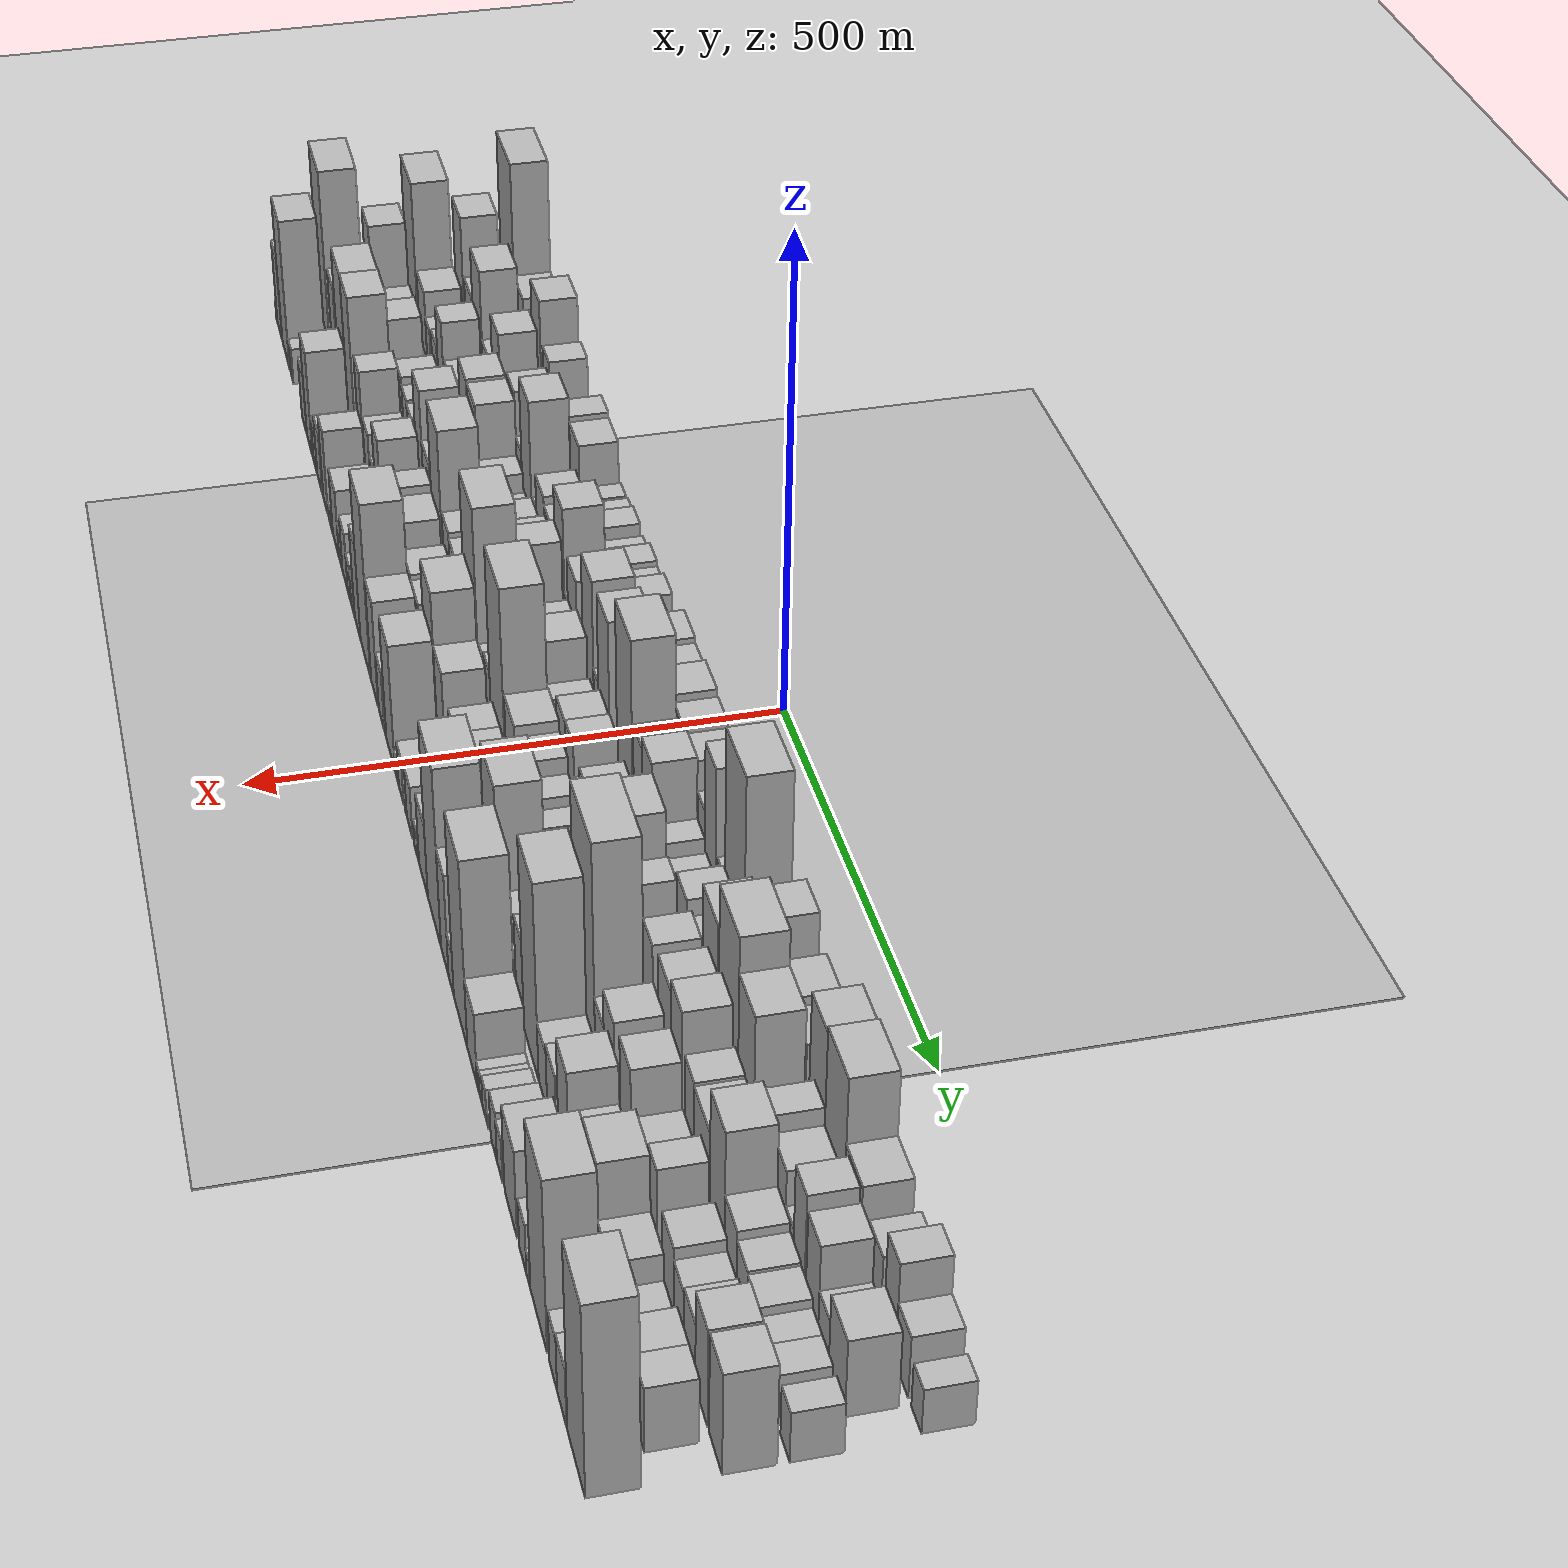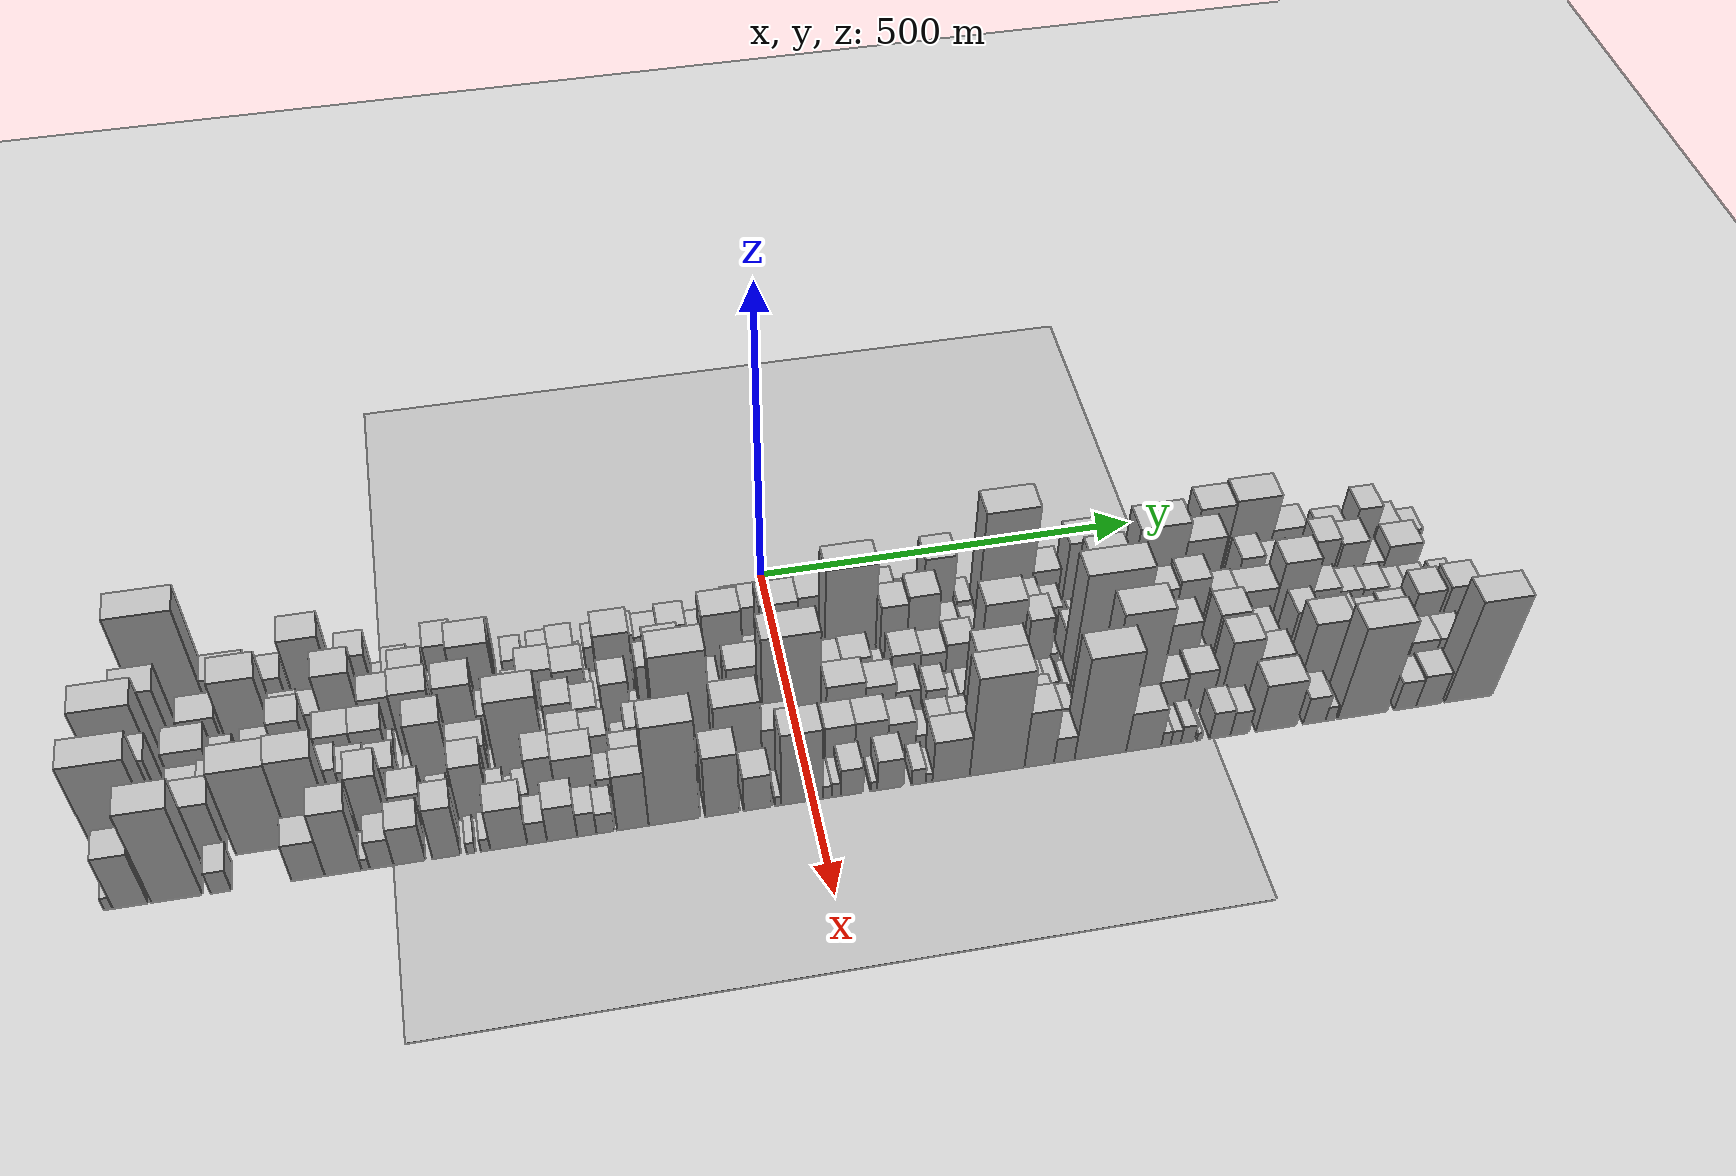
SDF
<?xml version="1.0" encoding="utf-8"?>

<sdf version="1.6">

   <world name="default">

      <gui fullscreen="0">

         <camera name="user_camera">

            <pose>-15 0 4.57585 0 0 0</pose>

            <view_controller>orbit</view_controller>

         </camera>

      </gui>

      <scene>

         <sky>

           <clouds>

             <speed>12</speed>

           </clouds>

         </sky>

         <ambient>0.4 0.4 0.4 1</ambient>

         <background>0.7 0.7 0.7 1</background>

         <shadows>1</shadows>

      </scene>

      <gravity>0 0 -9.8066</gravity>

      <magnetic_field>6e-06 2.3e-05 -4.2e-05</magnetic_field>

      <physics default="0" name="default_physics" type="ode">

         <ode>

            <solver>

               <type>quick</type>

               <iters>10</iters>

               <sor>1.0</sor>

               <use_dynamic_moi_rescaling>0</use_dynamic_moi_rescaling>

            </solver>

            <constraints>

               <cfm>0</cfm>

               <erp>0.2</erp>

               <contact_max_correcting_vel>100</contact_max_correcting_vel>

               <contact_surface_layer>0.001</contact_surface_layer>

            </constraints>

         </ode>

         <max_step_size>0.004</max_step_size>

         <real_time_factor>1</real_time_factor>

         <real_time_update_rate>250</real_time_update_rate>

      </physics>

      <light name="sun" type="directional">

         <cast_shadows>1</cast_shadows>

         <pose>0 0 10 0 0 0</pose>

         <diffuse>0.8 0.8 0.8 1</diffuse>

         <specular>0.2 0.2 0.2 1</specular>

         <attenuation>

            <range>1000</range>

            <constant>0.9</constant>

            <linear>0.01</linear>

            <quadratic>0.001</quadratic>

         </attenuation>

         <direction>-0.5 0.1 -0.9</direction>

      </light>

      <include>

         <name>ground_plane_1</name>

         <uri>model://HANNAS_ground_plane</uri>

         <pose>0 0 0  0 0 0</pose>

      </include>

      <include>

         <name>ground_plane_2</name>

         <uri>model://HANNAS_ground_plane</uri>

         <pose>100 0 0  0 0 0</pose>

      </include>

      <model name="building_1">

         <static>1</static>

         <pose frame="">100.0000 -824.8675 0 0.000000 0.000000 0.000000</pose>

         <link name="link">

            <pose frame="">0 0 12.00 0 0 0</pose>

            <collision name="collision">

               <geometry>

                  <box>

                     <size>40.0000 10.2650 24.0000</size>

                  </box>

               </geometry>

               <max_contacts>10</max_contacts>

               <surface>

                  <contact>

                     <ode/>

                  </contact>

                  <bounce/>

                  <friction>

                     <torsional>

                        <ode/>

                     </torsional>

                     <ode/>

                  </friction>

               </surface>

            </collision>

            <visual name="visual">

               <cast_shadows>0</cast_shadows>

               <geometry>

                  <box>

                     <size>40.0000 10.2650 24.0000</size>

                  </box>

               </geometry>

               <material>

                  <script>

                     <uri>model://HANNAS_wall/materials/scripts</uri>

                     <uri>model://HANNAS_wall/materials/textures</uri>

                     <name>vrc/HANNAS_wall</name>

                  </script>

               </material>

            </visual>

            <self_collide>0</self_collide>

            <enable_wind>0</enable_wind>

            <kinematic>0</kinematic>

         </link>

      </model>

      <model name="building_2">

         <static>1</static>

         <pose frame="">100.0000 -802.2113 0 0.000000 0.000000 0.000000</pose>

         <link name="link">

            <pose frame="">0 0 25.50 0 0 0</pose>

            <collision name="collision">

               <geometry>

                  <box>

                     <size>40.0000 29.0475 51.0000</size>

                  </box>

               </geometry>

               <max_contacts>10</max_contacts>

               <surface>

                  <contact>

                     <ode/>

                  </contact>

                  <bounce/>

                  <friction>

                     <torsional>

                        <ode/>

                     </torsional>

                     <ode/>

                  </friction>

               </surface>

            </collision>

            <visual name="visual">

               <cast_shadows>0</cast_shadows>

               <geometry>

                  <box>

                     <size>40.0000 29.0475 51.0000</size>

                  </box>

               </geometry>

               <material>

                  <script>

                     <uri>model://HANNAS_wall/materials/scripts</uri>

                     <uri>model://HANNAS_wall/materials/textures</uri>

                     <name>vrc/HANNAS_wall</name>

                  </script>

               </material>

            </visual>

            <self_collide>0</self_collide>

            <enable_wind>0</enable_wind>

            <kinematic>0</kinematic>

         </link>

      </model>

      <model name="building_3">

         <static>1</static>

         <pose frame="">100.0000 -745.2766 0 0.000000 0.000000 0.000000</pose>

         <link name="link">

            <pose frame="">0 0 111.00 0 0 0</pose>

            <collision name="collision">

               <geometry>

                  <box>

                     <size>40.0000 78.8218 222.0000</size>

                  </box>

               </geometry>

               <max_contacts>10</max_contacts>

               <surface>

                  <contact>

                     <ode/>

                  </contact>

                  <bounce/>

                  <friction>

                     <torsional>

                        <ode/>

                     </torsional>

                     <ode/>

                  </friction>

               </surface>

            </collision>

            <visual name="visual">

               <cast_shadows>0</cast_shadows>

               <geometry>

                  <box>

                     <size>40.0000 78.8218 222.0000</size>

                  </box>

               </geometry>

               <material>

                  <script>

                     <uri>model://HANNAS_wall/materials/scripts</uri>

                     <uri>model://HANNAS_wall/materials/textures</uri>

                     <name>vrc/HANNAS_wall</name>

                  </script>

               </material>

            </visual>

            <self_collide>0</self_collide>

            <enable_wind>0</enable_wind>

            <kinematic>0</kinematic>

         </link>

      </model>

      <model name="building_4">

         <static>1</static>

         <pose frame="">100.0000 -679.8648 0 0.000000 0.000000 0.000000</pose>

         <link name="link">

            <pose frame="">0 0 45.00 0 0 0</pose>

            <collision name="collision">

               <geometry>

                  <box>

                     <size>40.0000 52.0016 90.0000</size>

                  </box>

               </geometry>

               <max_contacts>10</max_contacts>

               <surface>

                  <contact>

                     <ode/>

                  </contact>

                  <bounce/>

                  <friction>

                     <torsional>

                        <ode/>

                     </torsional>

                     <ode/>

                  </friction>

               </surface>

            </collision>

            <visual name="visual">

               <cast_shadows>0</cast_shadows>

               <geometry>

                  <box>

                     <size>40.0000 52.0016 90.0000</size>

                  </box>

               </geometry>

               <material>

                  <script>

                     <uri>model://HANNAS_wall/materials/scripts</uri>

                     <uri>model://HANNAS_wall/materials/textures</uri>

                     <name>vrc/HANNAS_wall</name>

                  </script>

               </material>

            </visual>

            <self_collide>0</self_collide>

            <enable_wind>0</enable_wind>

            <kinematic>0</kinematic>

         </link>

      </model>

      <model name="building_5">

         <static>1</static>

         <pose frame="">100.0000 -633.1377 0 0.000000 0.000000 0.000000</pose>

         <link name="link">

            <pose frame="">0 0 37.50 0 0 0</pose>

            <collision name="collision">

               <geometry>

                  <box>

                     <size>40.0000 41.4525 75.0000</size>

                  </box>

               </geometry>

               <max_contacts>10</max_contacts>

               <surface>

                  <contact>

                     <ode/>

                  </contact>

                  <bounce/>

                  <friction>

                     <torsional>

                        <ode/>

                     </torsional>

                     <ode/>

                  </friction>

               </surface>

            </collision>

            <visual name="visual">

               <cast_shadows>0</cast_shadows>

               <geometry>

                  <box>

                     <size>40.0000 41.4525 75.0000</size>

                  </box>

               </geometry>

               <material>

                  <script>

                     <uri>model://HANNAS_wall/materials/scripts</uri>

                     <uri>model://HANNAS_wall/materials/textures</uri>

                     <name>vrc/HANNAS_wall</name>

                  </script>

               </material>

            </visual>

            <self_collide>0</self_collide>

            <enable_wind>0</enable_wind>

            <kinematic>0</kinematic>

         </link>

      </model>

      <model name="building_6">

         <static>1</static>

         <pose frame="">100.0000 -579.5908 0 0.000000 0.000000 0.000000</pose>

         <link name="link">

            <pose frame="">0 0 70.50 0 0 0</pose>

            <collision name="collision">

               <geometry>

                  <box>

                     <size>40.0000 47.6413 141.0000</size>

                  </box>

               </geometry>

               <max_contacts>10</max_contacts>

               <surface>

                  <contact>

                     <ode/>

                  </contact>

                  <bounce/>

                  <friction>

                     <torsional>

                        <ode/>

                     </torsional>

                     <ode/>

                  </friction>

               </surface>

            </collision>

            <visual name="visual">

               <cast_shadows>0</cast_shadows>

               <geometry>

                  <box>

                     <size>40.0000 47.6413 141.0000</size>

                  </box>

               </geometry>

               <material>

                  <script>

                     <uri>model://HANNAS_wall/materials/scripts</uri>

                     <uri>model://HANNAS_wall/materials/textures</uri>

                     <name>vrc/HANNAS_wall</name>

                  </script>

               </material>

            </visual>

            <self_collide>0</self_collide>

            <enable_wind>0</enable_wind>

            <kinematic>0</kinematic>

         </link>

      </model>

      <model name="building_7">

         <static>1</static>

         <pose frame="">100.0000 -549.5159 0 0.000000 0.000000 0.000000</pose>

         <link name="link">

            <pose frame="">0 0 13.50 0 0 0</pose>

            <collision name="collision">

               <geometry>

                  <box>

                     <size>40.0000 12.5085 27.0000</size>

                  </box>

               </geometry>

               <max_contacts>10</max_contacts>

               <surface>

                  <contact>

                     <ode/>

                  </contact>

                  <bounce/>

                  <friction>

                     <torsional>

                        <ode/>

                     </torsional>

                     <ode/>

                  </friction>

               </surface>

            </collision>

            <visual name="visual">

               <cast_shadows>0</cast_shadows>

               <geometry>

                  <box>

                     <size>40.0000 12.5085 27.0000</size>

                  </box>

               </geometry>

               <material>

                  <script>

                     <uri>model://HANNAS_wall/materials/scripts</uri>

                     <uri>model://HANNAS_wall/materials/textures</uri>

                     <name>vrc/HANNAS_wall</name>

                  </script>

               </material>

            </visual>

            <self_collide>0</self_collide>

            <enable_wind>0</enable_wind>

            <kinematic>0</kinematic>

         </link>

      </model>

      <model name="building_8">

         <static>1</static>

         <pose frame="">100.0000 -525.7927 0 0.000000 0.000000 0.000000</pose>

         <link name="link">

            <pose frame="">0 0 48.00 0 0 0</pose>

            <collision name="collision">

               <geometry>

                  <box>

                     <size>40.0000 34.9379 96.0000</size>

                  </box>

               </geometry>

               <max_contacts>10</max_contacts>

               <surface>

                  <contact>

                     <ode/>

                  </contact>

                  <bounce/>

                  <friction>

                     <torsional>

                        <ode/>

                     </torsional>

                     <ode/>

                  </friction>

               </surface>

            </collision>

            <visual name="visual">

               <cast_shadows>0</cast_shadows>

               <geometry>

                  <box>

                     <size>40.0000 34.9379 96.0000</size>

                  </box>

               </geometry>

               <material>

                  <script>

                     <uri>model://HANNAS_wall/materials/scripts</uri>

                     <uri>model://HANNAS_wall/materials/textures</uri>

                     <name>vrc/HANNAS_wall</name>

                  </script>

               </material>

            </visual>

            <self_collide>0</self_collide>

            <enable_wind>0</enable_wind>

            <kinematic>0</kinematic>

         </link>

      </model>

      <model name="building_9">

         <static>1</static>

         <pose frame="">100.0000 -500.5499 0 0.000000 0.000000 0.000000</pose>

         <link name="link">

            <pose frame="">0 0 15.00 0 0 0</pose>

            <collision name="collision">

               <geometry>

                  <box>

                     <size>40.0000 15.5478 30.0000</size>

                  </box>

               </geometry>

               <max_contacts>10</max_contacts>

               <surface>

                  <contact>

                     <ode/>

                  </contact>

                  <bounce/>

                  <friction>

                     <torsional>

                        <ode/>

                     </torsional>

                     <ode/>

                  </friction>

               </surface>

            </collision>

            <visual name="visual">

               <cast_shadows>0</cast_shadows>

               <geometry>

                  <box>

                     <size>40.0000 15.5478 30.0000</size>

                  </box>

               </geometry>

               <material>

                  <script>

                     <uri>model://HANNAS_wall/materials/scripts</uri>

                     <uri>model://HANNAS_wall/materials/textures</uri>

                     <name>vrc/HANNAS_wall</name>

                  </script>

               </material>

            </visual>

            <self_collide>0</self_collide>

            <enable_wind>0</enable_wind>

            <kinematic>0</kinematic>

         </link>

      </model>

      <model name="building_10">

         <static>1</static>

         <pose frame="">100.0000 -477.1615 0 0.000000 0.000000 0.000000</pose>

         <link name="link">

            <pose frame="">0 0 28.50 0 0 0</pose>

            <collision name="collision">

               <geometry>

                  <box>

                     <size>40.0000 31.2288 57.0000</size>

                  </box>

               </geometry>

               <max_contacts>10</max_contacts>

               <surface>

                  <contact>

                     <ode/>

                  </contact>

                  <bounce/>

                  <friction>

                     <torsional>

                        <ode/>

                     </torsional>

                     <ode/>

                  </friction>

               </surface>

            </collision>

            <visual name="visual">

               <cast_shadows>0</cast_shadows>

               <geometry>

                  <box>

                     <size>40.0000 31.2288 57.0000</size>

                  </box>

               </geometry>

               <material>

                  <script>

                     <uri>model://HANNAS_wall/materials/scripts</uri>

                     <uri>model://HANNAS_wall/materials/textures</uri>

                     <name>vrc/HANNAS_wall</name>

                  </script>

               </material>

            </visual>

            <self_collide>0</self_collide>

            <enable_wind>0</enable_wind>

            <kinematic>0</kinematic>

         </link>

      </model>

      <model name="building_11">

         <static>1</static>

         <pose frame="">100.0000 -450.0540 0 0.000000 0.000000 0.000000</pose>

         <link name="link">

            <pose frame="">0 0 22.50 0 0 0</pose>

            <collision name="collision">

               <geometry>

                  <box>

                     <size>40.0000 22.9864 45.0000</size>

                  </box>

               </geometry>

               <max_contacts>10</max_contacts>

               <surface>

                  <contact>

                     <ode/>

                  </contact>

                  <bounce/>

                  <friction>

                     <torsional>

                        <ode/>

                     </torsional>

                     <ode/>

                  </friction>

               </surface>

            </collision>

            <visual name="visual">

               <cast_shadows>0</cast_shadows>

               <geometry>

                  <box>

                     <size>40.0000 22.9864 45.0000</size>

                  </box>

               </geometry>

               <material>

                  <script>

                     <uri>model://HANNAS_wall/materials/scripts</uri>

                     <uri>model://HANNAS_wall/materials/textures</uri>

                     <name>vrc/HANNAS_wall</name>

                  </script>

               </material>

            </visual>

            <self_collide>0</self_collide>

            <enable_wind>0</enable_wind>

            <kinematic>0</kinematic>

         </link>

      </model>

      <model name="building_12">

         <static>1</static>

         <pose frame="">100.0000 -421.3638 0 0.000000 0.000000 0.000000</pose>

         <link name="link">

            <pose frame="">0 0 46.50 0 0 0</pose>

            <collision name="collision">

               <geometry>

                  <box>

                     <size>40.0000 34.3939 93.0000</size>

                  </box>

               </geometry>

               <max_contacts>10</max_contacts>

               <surface>

                  <contact>

                     <ode/>

                  </contact>

                  <bounce/>

                  <friction>

                     <torsional>

                        <ode/>

                     </torsional>

                     <ode/>

                  </friction>

               </surface>

            </collision>

            <visual name="visual">

               <cast_shadows>0</cast_shadows>

               <geometry>

                  <box>

                     <size>40.0000 34.3939 93.0000</size>

                  </box>

               </geometry>

               <material>

                  <script>

                     <uri>model://HANNAS_wall/materials/scripts</uri>

                     <uri>model://HANNAS_wall/materials/textures</uri>

                     <name>vrc/HANNAS_wall</name>

                  </script>

               </material>

            </visual>

            <self_collide>0</self_collide>

            <enable_wind>0</enable_wind>

            <kinematic>0</kinematic>

         </link>

      </model>

      <model name="building_13">

         <static>1</static>

         <pose frame="">100.0000 -380.7621 0 0.000000 0.000000 0.000000</pose>

         <link name="link">

            <pose frame="">0 0 43.50 0 0 0</pose>

            <collision name="collision">

               <geometry>

                  <box>

                     <size>40.0000 46.8095 87.0000</size>

                  </box>

               </geometry>

               <max_contacts>10</max_contacts>

               <surface>

                  <contact>

                     <ode/>

                  </contact>

                  <bounce/>

                  <friction>

                     <torsional>

                        <ode/>

                     </torsional>

                     <ode/>

                  </friction>

               </surface>

            </collision>

            <visual name="visual">

               <cast_shadows>0</cast_shadows>

               <geometry>

                  <box>

                     <size>40.0000 46.8095 87.0000</size>

                  </box>

               </geometry>

               <material>

                  <script>

                     <uri>model://HANNAS_wall/materials/scripts</uri>

                     <uri>model://HANNAS_wall/materials/textures</uri>

                     <name>vrc/HANNAS_wall</name>

                  </script>

               </material>

            </visual>

            <self_collide>0</self_collide>

            <enable_wind>0</enable_wind>

            <kinematic>0</kinematic>

         </link>

      </model>

      <model name="building_14">

         <static>1</static>

         <pose frame="">100.0000 -334.8359 0 0.000000 0.000000 0.000000</pose>

         <link name="link">

            <pose frame="">0 0 22.50 0 0 0</pose>

            <collision name="collision">

               <geometry>

                  <box>

                     <size>40.0000 25.0428 45.0000</size>

                  </box>

               </geometry>

               <max_contacts>10</max_contacts>

               <surface>

                  <contact>

                     <ode/>

                  </contact>

                  <bounce/>

                  <friction>

                     <torsional>

                        <ode/>

                     </torsional>

                     <ode/>

                  </friction>

               </surface>

            </collision>

            <visual name="visual">

               <cast_shadows>0</cast_shadows>

               <geometry>

                  <box>

                     <size>40.0000 25.0428 45.0000</size>

                  </box>

               </geometry>

               <material>

                  <script>

                     <uri>model://HANNAS_wall/materials/scripts</uri>

                     <uri>model://HANNAS_wall/materials/textures</uri>

                     <name>vrc/HANNAS_wall</name>

                  </script>

               </material>

            </visual>

            <self_collide>0</self_collide>

            <enable_wind>0</enable_wind>

            <kinematic>0</kinematic>

         </link>

      </model>

      <model name="building_15">

         <static>1</static>

         <pose frame="">100.0000 -301.9483 0 0.000000 0.000000 0.000000</pose>

         <link name="link">

            <pose frame="">0 0 24.00 0 0 0</pose>

            <collision name="collision">

               <geometry>

                  <box>

                     <size>40.0000 24.7324 48.0000</size>

                  </box>

               </geometry>

               <max_contacts>10</max_contacts>

               <surface>

                  <contact>

                     <ode/>

                  </contact>

                  <bounce/>

                  <friction>

                     <torsional>

                        <ode/>

                     </torsional>

                     <ode/>

                  </friction>

               </surface>

            </collision>

            <visual name="visual">

               <cast_shadows>0</cast_shadows>

               <geometry>

                  <box>

                     <size>40.0000 24.7324 48.0000</size>

                  </box>

               </geometry>

               <material>

                  <script>

                     <uri>model://HANNAS_wall/materials/scripts</uri>

                     <uri>model://HANNAS_wall/materials/textures</uri>

                     <name>vrc/HANNAS_wall</name>

                  </script>

               </material>

            </visual>

            <self_collide>0</self_collide>

            <enable_wind>0</enable_wind>

            <kinematic>0</kinematic>

         </link>

      </model>

      <model name="building_16">

         <static>1</static>

         <pose frame="">100.0000 -273.3891 0 0.000000 0.000000 0.000000</pose>

         <link name="link">

            <pose frame="">0 0 27.00 0 0 0</pose>

            <collision name="collision">

               <geometry>

                  <box>

                     <size>40.0000 32.3860 54.0000</size>

                  </box>

               </geometry>

               <max_contacts>10</max_contacts>

               <surface>

                  <contact>

                     <ode/>

                  </contact>

                  <bounce/>

                  <friction>

                     <torsional>

                        <ode/>

                     </torsional>

                     <ode/>

                  </friction>

               </surface>

            </collision>

            <visual name="visual">

               <cast_shadows>0</cast_shadows>

               <geometry>

                  <box>

                     <size>40.0000 32.3860 54.0000</size>

                  </box>

               </geometry>

               <material>

                  <script>

                     <uri>model://HANNAS_wall/materials/scripts</uri>

                     <uri>model://HANNAS_wall/materials/textures</uri>

                     <name>vrc/HANNAS_wall</name>

                  </script>

               </material>

            </visual>

            <self_collide>0</self_collide>

            <enable_wind>0</enable_wind>

            <kinematic>0</kinematic>

         </link>

      </model>

      <model name="building_17">

         <static>1</static>

         <pose frame="">100.0000 -253.6204 0 0.000000 0.000000 0.000000</pose>

         <link name="link">

            <pose frame="">0 0 7.50 0 0 0</pose>

            <collision name="collision">

               <geometry>

                  <box>

                     <size>40.0000 7.1513 15.0000</size>

                  </box>

               </geometry>

               <max_contacts>10</max_contacts>

               <surface>

                  <contact>

                     <ode/>

                  </contact>

                  <bounce/>

                  <friction>

                     <torsional>

                        <ode/>

                     </torsional>

                     <ode/>

                  </friction>

               </surface>

            </collision>

            <visual name="visual">

               <cast_shadows>0</cast_shadows>

               <geometry>

                  <box>

                     <size>40.0000 7.1513 15.0000</size>

                  </box>

               </geometry>

               <material>

                  <script>

                     <uri>model://HANNAS_wall/materials/scripts</uri>

                     <uri>model://HANNAS_wall/materials/textures</uri>

                     <name>vrc/HANNAS_wall</name>

                  </script>

               </material>

            </visual>

            <self_collide>0</self_collide>

            <enable_wind>0</enable_wind>

            <kinematic>0</kinematic>

         </link>

      </model>

      <model name="building_18">

         <static>1</static>

         <pose frame="">100.0000 -232.7130 0 0.000000 0.000000 0.000000</pose>

         <link name="link">

            <pose frame="">0 0 24.00 0 0 0</pose>

            <collision name="collision">

               <geometry>

                  <box>

                     <size>40.0000 24.6636 48.0000</size>

                  </box>

               </geometry>

               <max_contacts>10</max_contacts>

               <surface>

                  <contact>

                     <ode/>

                  </contact>

                  <bounce/>

                  <friction>

                     <torsional>

                        <ode/>

                     </torsional>

                     <ode/>

                  </friction>

               </surface>

            </collision>

            <visual name="visual">

               <cast_shadows>0</cast_shadows>

               <geometry>

                  <box>

                     <size>40.0000 24.6636 48.0000</size>

                  </box>

               </geometry>

               <material>

                  <script>

                     <uri>model://HANNAS_wall/materials/scripts</uri>

                     <uri>model://HANNAS_wall/materials/textures</uri>

                     <name>vrc/HANNAS_wall</name>

                  </script>

               </material>

            </visual>

            <self_collide>0</self_collide>

            <enable_wind>0</enable_wind>

            <kinematic>0</kinematic>

         </link>

      </model>

      <model name="building_19">

         <static>1</static>

         <pose frame="">100.0000 -197.5365 0 0.000000 0.000000 0.000000</pose>

         <link name="link">

            <pose frame="">0 0 30.00 0 0 0</pose>

            <collision name="collision">

               <geometry>

                  <box>

                     <size>40.0000 31.6895 60.0000</size>

                  </box>

               </geometry>

               <max_contacts>10</max_contacts>

               <surface>

                  <contact>

                     <ode/>

                  </contact>

                  <bounce/>

                  <friction>

                     <torsional>

                        <ode/>

                     </torsional>

                     <ode/>

                  </friction>

               </surface>

            </collision>

            <visual name="visual">

               <cast_shadows>0</cast_shadows>

               <geometry>

                  <box>

                     <size>40.0000 31.6895 60.0000</size>

                  </box>

               </geometry>

               <material>

                  <script>

                     <uri>model://HANNAS_wall/materials/scripts</uri>

                     <uri>model://HANNAS_wall/materials/textures</uri>

                     <name>vrc/HANNAS_wall</name>

                  </script>

               </material>

            </visual>

            <self_collide>0</self_collide>

            <enable_wind>0</enable_wind>

            <kinematic>0</kinematic>

         </link>

      </model>

      <model name="building_20">

         <static>1</static>

         <pose frame="">100.0000 -166.4657 0 0.000000 0.000000 0.000000</pose>

         <link name="link">

            <pose frame="">0 0 27.00 0 0 0</pose>

            <collision name="collision">

               <geometry>

                  <box>

                     <size>40.0000 30.4520 54.0000</size>

                  </box>

               </geometry>

               <max_contacts>10</max_contacts>

               <surface>

                  <contact>

                     <ode/>

                  </contact>

                  <bounce/>

                  <friction>

                     <torsional>

                        <ode/>

                     </torsional>

                     <ode/>

                  </friction>

               </surface>

            </collision>

            <visual name="visual">

               <cast_shadows>0</cast_shadows>

               <geometry>

                  <box>

                     <size>40.0000 30.4520 54.0000</size>

                  </box>

               </geometry>

               <material>

                  <script>

                     <uri>model://HANNAS_wall/materials/scripts</uri>

                     <uri>model://HANNAS_wall/materials/textures</uri>

                     <name>vrc/HANNAS_wall</name>

                  </script>

               </material>

            </visual>

            <self_collide>0</self_collide>

            <enable_wind>0</enable_wind>

            <kinematic>0</kinematic>

         </link>

      </model>

      <model name="building_21">

         <static>1</static>

         <pose frame="">100.0000 -133.3583 0 0.000000 0.000000 0.000000</pose>

         <link name="link">

            <pose frame="">0 0 33.00 0 0 0</pose>

            <collision name="collision">

               <geometry>

                  <box>

                     <size>40.0000 35.7628 66.0000</size>

                  </box>

               </geometry>

               <max_contacts>10</max_contacts>

               <surface>

                  <contact>

                     <ode/>

                  </contact>

                  <bounce/>

                  <friction>

                     <torsional>

                        <ode/>

                     </torsional>

                     <ode/>

                  </friction>

               </surface>

            </collision>

            <visual name="visual">

               <cast_shadows>0</cast_shadows>

               <geometry>

                  <box>

                     <size>40.0000 35.7628 66.0000</size>

                  </box>

               </geometry>

               <material>

                  <script>

                     <uri>model://HANNAS_wall/materials/scripts</uri>

                     <uri>model://HANNAS_wall/materials/textures</uri>

                     <name>vrc/HANNAS_wall</name>

                  </script>

               </material>

            </visual>

            <self_collide>0</self_collide>

            <enable_wind>0</enable_wind>

            <kinematic>0</kinematic>

         </link>

      </model>

      <model name="building_22">

         <static>1</static>

         <pose frame="">100.0000 -103.6162 0 0.000000 0.000000 0.000000</pose>

         <link name="link">

            <pose frame="">0 0 22.50 0 0 0</pose>

            <collision name="collision">

               <geometry>

                  <box>

                     <size>40.0000 23.7214 45.0000</size>

                  </box>

               </geometry>

               <max_contacts>10</max_contacts>

               <surface>

                  <contact>

                     <ode/>

                  </contact>

                  <bounce/>

                  <friction>

                     <torsional>

                        <ode/>

                     </torsional>

                     <ode/>

                  </friction>

               </surface>

            </collision>

            <visual name="visual">

               <cast_shadows>0</cast_shadows>

               <geometry>

                  <box>

                     <size>40.0000 23.7214 45.0000</size>

                  </box>

               </geometry>

               <material>

                  <script>

                     <uri>model://HANNAS_wall/materials/scripts</uri>

                     <uri>model://HANNAS_wall/materials/textures</uri>

                     <name>vrc/HANNAS_wall</name>

                  </script>

               </material>

            </visual>

            <self_collide>0</self_collide>

            <enable_wind>0</enable_wind>

            <kinematic>0</kinematic>

         </link>

      </model>

      <model name="building_23">

         <static>1</static>

         <pose frame="">100.0000 -79.4500 0 0.000000 0.000000 0.000000</pose>

         <link name="link">

            <pose frame="">0 0 21.00 0 0 0</pose>

            <collision name="collision">

               <geometry>

                  <box>

                     <size>40.0000 24.6110 42.0000</size>

                  </box>

               </geometry>

               <max_contacts>10</max_contacts>

               <surface>

                  <contact>

                     <ode/>

                  </contact>

                  <bounce/>

                  <friction>

                     <torsional>

                        <ode/>

                     </torsional>

                     <ode/>

                  </friction>

               </surface>

            </collision>

            <visual name="visual">

               <cast_shadows>0</cast_shadows>

               <geometry>

                  <box>

                     <size>40.0000 24.6110 42.0000</size>

                  </box>

               </geometry>

               <material>

                  <script>

                     <uri>model://HANNAS_wall/materials/scripts</uri>

                     <uri>model://HANNAS_wall/materials/textures</uri>

                     <name>vrc/HANNAS_wall</name>

                  </script>

               </material>

            </visual>

            <self_collide>0</self_collide>

            <enable_wind>0</enable_wind>

            <kinematic>0</kinematic>

         </link>

      </model>

      <model name="building_24">

         <static>1</static>

         <pose frame="">100.0000 -44.3742 0 0.000000 0.000000 0.000000</pose>

         <link name="link">

            <pose frame="">0 0 40.50 0 0 0</pose>

            <collision name="collision">

               <geometry>

                  <box>

                     <size>40.0000 45.5407 81.0000</size>

                  </box>

               </geometry>

               <max_contacts>10</max_contacts>

               <surface>

                  <contact>

                     <ode/>

                  </contact>

                  <bounce/>

                  <friction>

                     <torsional>

                        <ode/>

                     </torsional>

                     <ode/>

                  </friction>

               </surface>

            </collision>

            <visual name="visual">

               <cast_shadows>0</cast_shadows>

               <geometry>

                  <box>

                     <size>40.0000 45.5407 81.0000</size>

                  </box>

               </geometry>

               <material>

                  <script>

                     <uri>model://HANNAS_wall/materials/scripts</uri>

                     <uri>model://HANNAS_wall/materials/textures</uri>

                     <name>vrc/HANNAS_wall</name>

                  </script>

               </material>

            </visual>

            <self_collide>0</self_collide>

            <enable_wind>0</enable_wind>

            <kinematic>0</kinematic>

         </link>

      </model>

      <model name="building_25">

         <static>1</static>

         <pose frame="">100.0000 -1.3551 0 0.000000 0.000000 0.000000</pose>

         <link name="link">

            <pose frame="">0 0 37.50 0 0 0</pose>

            <collision name="collision">

               <geometry>

                  <box>

                     <size>40.0000 40.4975 75.0000</size>

                  </box>

               </geometry>

               <max_contacts>10</max_contacts>

               <surface>

                  <contact>

                     <ode/>

                  </contact>

                  <bounce/>

                  <friction>

                     <torsional>

                        <ode/>

                     </torsional>

                     <ode/>

                  </friction>

               </surface>

            </collision>

            <visual name="visual">

               <cast_shadows>0</cast_shadows>

               <geometry>

                  <box>

                     <size>40.0000 40.4975 75.0000</size>

                  </box>

               </geometry>

               <material>

                  <script>

                     <uri>model://HANNAS_wall/materials/scripts</uri>

                     <uri>model://HANNAS_wall/materials/textures</uri>

                     <name>vrc/HANNAS_wall</name>

                  </script>

               </material>

            </visual>

            <self_collide>0</self_collide>

            <enable_wind>0</enable_wind>

            <kinematic>0</kinematic>

         </link>

      </model>

      <model name="building_26">

         <static>1</static>

         <pose frame="">100.0000 41.7516 0 0.000000 0.000000 0.000000</pose>

         <link name="link">

            <pose frame="">0 0 42.00 0 0 0</pose>

            <collision name="collision">

               <geometry>

                  <box>

                     <size>40.0000 45.7160 84.0000</size>

                  </box>

               </geometry>

               <max_contacts>10</max_contacts>

               <surface>

                  <contact>

                     <ode/>

                  </contact>

                  <bounce/>

                  <friction>

                     <torsional>

                        <ode/>

                     </torsional>

                     <ode/>

                  </friction>

               </surface>

            </collision>

            <visual name="visual">

               <cast_shadows>0</cast_shadows>

               <geometry>

                  <box>

                     <size>40.0000 45.7160 84.0000</size>

                  </box>

               </geometry>

               <material>

                  <script>

                     <uri>model://HANNAS_wall/materials/scripts</uri>

                     <uri>model://HANNAS_wall/materials/textures</uri>

                     <name>vrc/HANNAS_wall</name>

                  </script>

               </material>

            </visual>

            <self_collide>0</self_collide>

            <enable_wind>0</enable_wind>

            <kinematic>0</kinematic>

         </link>

      </model>

      <model name="building_27">

         <static>1</static>

         <pose frame="">100.0000 87.2052 0 0.000000 0.000000 0.000000</pose>

         <link name="link">

            <pose frame="">0 0 39.00 0 0 0</pose>

            <collision name="collision">

               <geometry>

                  <box>

                     <size>40.0000 39.1912 78.0000</size>

                  </box>

               </geometry>

               <max_contacts>10</max_contacts>

               <surface>

                  <contact>

                     <ode/>

                  </contact>

                  <bounce/>

                  <friction>

                     <torsional>

                        <ode/>

                     </torsional>

                     <ode/>

                  </friction>

               </surface>

            </collision>

            <visual name="visual">

               <cast_shadows>0</cast_shadows>

               <geometry>

                  <box>

                     <size>40.0000 39.1912 78.0000</size>

                  </box>

               </geometry>

               <material>

                  <script>

                     <uri>model://HANNAS_wall/materials/scripts</uri>

                     <uri>model://HANNAS_wall/materials/textures</uri>

                     <name>vrc/HANNAS_wall</name>

                  </script>

               </material>

            </visual>

            <self_collide>0</self_collide>

            <enable_wind>0</enable_wind>

            <kinematic>0</kinematic>

         </link>

      </model>

      <model name="building_28">

         <static>1</static>

         <pose frame="">100.0000 131.3394 0 0.000000 0.000000 0.000000</pose>

         <link name="link">

            <pose frame="">0 0 37.50 0 0 0</pose>

            <collision name="collision">

               <geometry>

                  <box>

                     <size>40.0000 41.0772 75.0000</size>

                  </box>

               </geometry>

               <max_contacts>10</max_contacts>

               <surface>

                  <contact>

                     <ode/>

                  </contact>

                  <bounce/>

                  <friction>

                     <torsional>

                        <ode/>

                     </torsional>

                     <ode/>

                  </friction>

               </surface>

            </collision>

            <visual name="visual">

               <cast_shadows>0</cast_shadows>

               <geometry>

                  <box>

                     <size>40.0000 41.0772 75.0000</size>

                  </box>

               </geometry>

               <material>

                  <script>

                     <uri>model://HANNAS_wall/materials/scripts</uri>

                     <uri>model://HANNAS_wall/materials/textures</uri>

                     <name>vrc/HANNAS_wall</name>

                  </script>

               </material>

            </visual>

            <self_collide>0</self_collide>

            <enable_wind>0</enable_wind>

            <kinematic>0</kinematic>

         </link>

      </model>

      <model name="building_29">

         <static>1</static>

         <pose frame="">100.0000 155.6644 0 0.000000 0.000000 0.000000</pose>

         <link name="link">

            <pose frame="">0 0 9.00 0 0 0</pose>

            <collision name="collision">

               <geometry>

                  <box>

                     <size>40.0000 7.5728 18.0000</size>

                  </box>

               </geometry>

               <max_contacts>10</max_contacts>

               <surface>

                  <contact>

                     <ode/>

                  </contact>

                  <bounce/>

                  <friction>

                     <torsional>

                        <ode/>

                     </torsional>

                     <ode/>

                  </friction>

               </surface>

            </collision>

            <visual name="visual">

               <cast_shadows>0</cast_shadows>

               <geometry>

                  <box>

                     <size>40.0000 7.5728 18.0000</size>

                  </box>

               </geometry>

               <material>

                  <script>

                     <uri>model://HANNAS_wall/materials/scripts</uri>

                     <uri>model://HANNAS_wall/materials/textures</uri>

                     <name>vrc/HANNAS_wall</name>

                  </script>

               </material>

            </visual>

            <self_collide>0</self_collide>

            <enable_wind>0</enable_wind>

            <kinematic>0</kinematic>

         </link>

      </model>

      <model name="building_30">

         <static>1</static>

         <pose frame="">100.0000 173.6696 0 0.000000 0.000000 0.000000</pose>

         <link name="link">

            <pose frame="">0 0 24.00 0 0 0</pose>

            <collision name="collision">

               <geometry>

                  <box>

                     <size>40.0000 28.4376 48.0000</size>

                  </box>

               </geometry>

               <max_contacts>10</max_contacts>

               <surface>

                  <contact>

                     <ode/>

                  </contact>

                  <bounce/>

                  <friction>

                     <torsional>

                        <ode/>

                     </torsional>

                     <ode/>

                  </friction>

               </surface>

            </collision>

            <visual name="visual">

               <cast_shadows>0</cast_shadows>

               <geometry>

                  <box>

                     <size>40.0000 28.4376 48.0000</size>

                  </box>

               </geometry>

               <material>

                  <script>

                     <uri>model://HANNAS_wall/materials/scripts</uri>

                     <uri>model://HANNAS_wall/materials/textures</uri>

                     <name>vrc/HANNAS_wall</name>

                  </script>

               </material>

            </visual>

            <self_collide>0</self_collide>

            <enable_wind>0</enable_wind>

            <kinematic>0</kinematic>

         </link>

      </model>

      <model name="building_31">

         <static>1</static>

         <pose frame="">100.0000 207.8174 0 0.000000 0.000000 0.000000</pose>

         <link name="link">

            <pose frame="">0 0 61.50 0 0 0</pose>

            <collision name="collision">

               <geometry>

                  <box>

                     <size>40.0000 39.8579 123.0000</size>

                  </box>

               </geometry>

               <max_contacts>10</max_contacts>

               <surface>

                  <contact>

                     <ode/>

                  </contact>

                  <bounce/>

                  <friction>

                     <torsional>

                        <ode/>

                     </torsional>

                     <ode/>

                  </friction>

               </surface>

            </collision>

            <visual name="visual">

               <cast_shadows>0</cast_shadows>

               <geometry>

                  <box>

                     <size>40.0000 39.8579 123.0000</size>

                  </box>

               </geometry>

               <material>

                  <script>

                     <uri>model://HANNAS_wall/materials/scripts</uri>

                     <uri>model://HANNAS_wall/materials/textures</uri>

                     <name>vrc/HANNAS_wall</name>

                  </script>

               </material>

            </visual>

            <self_collide>0</self_collide>

            <enable_wind>0</enable_wind>

            <kinematic>0</kinematic>

         </link>

      </model>

      <model name="building_32">

         <static>1</static>

         <pose frame="">100.0000 243.5929 0 0.000000 0.000000 0.000000</pose>

         <link name="link">

            <pose frame="">0 0 16.50 0 0 0</pose>

            <collision name="collision">

               <geometry>

                  <box>

                     <size>40.0000 19.6932 33.0000</size>

                  </box>

               </geometry>

               <max_contacts>10</max_contacts>

               <surface>

                  <contact>

                     <ode/>

                  </contact>

                  <bounce/>

                  <friction>

                     <torsional>

                        <ode/>

                     </torsional>

                     <ode/>

                  </friction>

               </surface>

            </collision>

            <visual name="visual">

               <cast_shadows>0</cast_shadows>

               <geometry>

                  <box>

                     <size>40.0000 19.6932 33.0000</size>

                  </box>

               </geometry>

               <material>

                  <script>

                     <uri>model://HANNAS_wall/materials/scripts</uri>

                     <uri>model://HANNAS_wall/materials/textures</uri>

                     <name>vrc/HANNAS_wall</name>

                  </script>

               </material>

            </visual>

            <self_collide>0</self_collide>

            <enable_wind>0</enable_wind>

            <kinematic>0</kinematic>

         </link>

      </model>

      <model name="building_33">

         <static>1</static>

         <pose frame="">100.0000 295.9719 0 0.000000 0.000000 0.000000</pose>

         <link name="link">

            <pose frame="">0 0 96.00 0 0 0</pose>

            <collision name="collision">

               <geometry>

                  <box>

                     <size>40.0000 69.0647 192.0000</size>

                  </box>

               </geometry>

               <max_contacts>10</max_contacts>

               <surface>

                  <contact>

                     <ode/>

                  </contact>

                  <bounce/>

                  <friction>

                     <torsional>

                        <ode/>

                     </torsional>

                     <ode/>

                  </friction>

               </surface>

            </collision>

            <visual name="visual">

               <cast_shadows>0</cast_shadows>

               <geometry>

                  <box>

                     <size>40.0000 69.0647 192.0000</size>

                  </box>

               </geometry>

               <material>

                  <script>

                     <uri>model://HANNAS_wall/materials/scripts</uri>

                     <uri>model://HANNAS_wall/materials/textures</uri>

                     <name>vrc/HANNAS_wall</name>

                  </script>

               </material>

            </visual>

            <self_collide>0</self_collide>

            <enable_wind>0</enable_wind>

            <kinematic>0</kinematic>

         </link>

      </model>

      <model name="building_34">

         <static>1</static>

         <pose frame="">100.0000 349.0040 0 0.000000 0.000000 0.000000</pose>

         <link name="link">

            <pose frame="">0 0 34.50 0 0 0</pose>

            <collision name="collision">

               <geometry>

                  <box>

                     <size>40.0000 36.9994 69.0000</size>

                  </box>

               </geometry>

               <max_contacts>10</max_contacts>

               <surface>

                  <contact>

                     <ode/>

                  </contact>

                  <bounce/>

                  <friction>

                     <torsional>

                        <ode/>

                     </torsional>

                     <ode/>

                  </friction>

               </surface>

            </collision>

            <visual name="visual">

               <cast_shadows>0</cast_shadows>

               <geometry>

                  <box>

                     <size>40.0000 36.9994 69.0000</size>

                  </box>

               </geometry>

               <material>

                  <script>

                     <uri>model://HANNAS_wall/materials/scripts</uri>

                     <uri>model://HANNAS_wall/materials/textures</uri>

                     <name>vrc/HANNAS_wall</name>

                  </script>

               </material>

            </visual>

            <self_collide>0</self_collide>

            <enable_wind>0</enable_wind>

            <kinematic>0</kinematic>

         </link>

      </model>

      <model name="building_35">

         <static>1</static>

         <pose frame="">100.0000 395.9646 0 0.000000 0.000000 0.000000</pose>

         <link name="link">

            <pose frame="">0 0 57.00 0 0 0</pose>

            <collision name="collision">

               <geometry>

                  <box>

                     <size>40.0000 42.9218 114.0000</size>

                  </box>

               </geometry>

               <max_contacts>10</max_contacts>

               <surface>

                  <contact>

                     <ode/>

                  </contact>

                  <bounce/>

                  <friction>

                     <torsional>

                        <ode/>

                     </torsional>

                     <ode/>

                  </friction>

               </surface>

            </collision>

            <visual name="visual">

               <cast_shadows>0</cast_shadows>

               <geometry>

                  <box>

                     <size>40.0000 42.9218 114.0000</size>

                  </box>

               </geometry>

               <material>

                  <script>

                     <uri>model://HANNAS_wall/materials/scripts</uri>

                     <uri>model://HANNAS_wall/materials/textures</uri>

                     <name>vrc/HANNAS_wall</name>

                  </script>

               </material>

            </visual>

            <self_collide>0</self_collide>

            <enable_wind>0</enable_wind>

            <kinematic>0</kinematic>

         </link>

      </model>

      <model name="building_36">

         <static>1</static>

         <pose frame="">100.0000 427.3676 0 0.000000 0.000000 0.000000</pose>

         <link name="link">

            <pose frame="">0 0 18.00 0 0 0</pose>

            <collision name="collision">

               <geometry>

                  <box>

                     <size>40.0000 19.8844 36.0000</size>

                  </box>

               </geometry>

               <max_contacts>10</max_contacts>

               <surface>

                  <contact>

                     <ode/>

                  </contact>

                  <bounce/>

                  <friction>

                     <torsional>

                        <ode/>

                     </torsional>

                     <ode/>

                  </friction>

               </surface>

            </collision>

            <visual name="visual">

               <cast_shadows>0</cast_shadows>

               <geometry>

                  <box>

                     <size>40.0000 19.8844 36.0000</size>

                  </box>

               </geometry>

               <material>

                  <script>

                     <uri>model://HANNAS_wall/materials/scripts</uri>

                     <uri>model://HANNAS_wall/materials/textures</uri>

                     <name>vrc/HANNAS_wall</name>

                  </script>

               </material>

            </visual>

            <self_collide>0</self_collide>

            <enable_wind>0</enable_wind>

            <kinematic>0</kinematic>

         </link>

      </model>

      <model name="building_37">

         <static>1</static>

         <pose frame="">100.0000 463.5204 0 0.000000 0.000000 0.000000</pose>

         <link name="link">

            <pose frame="">0 0 45.00 0 0 0</pose>

            <collision name="collision">

               <geometry>

                  <box>

                     <size>40.0000 46.4212 90.0000</size>

                  </box>

               </geometry>

               <max_contacts>10</max_contacts>

               <surface>

                  <contact>

                     <ode/>

                  </contact>

                  <bounce/>

                  <friction>

                     <torsional>

                        <ode/>

                     </torsional>

                     <ode/>

                  </friction>

               </surface>

            </collision>

            <visual name="visual">

               <cast_shadows>0</cast_shadows>

               <geometry>

                  <box>

                     <size>40.0000 46.4212 90.0000</size>

                  </box>

               </geometry>

               <material>

                  <script>

                     <uri>model://HANNAS_wall/materials/scripts</uri>

                     <uri>model://HANNAS_wall/materials/textures</uri>

                     <name>vrc/HANNAS_wall</name>

                  </script>

               </material>

            </visual>

            <self_collide>0</self_collide>

            <enable_wind>0</enable_wind>

            <kinematic>0</kinematic>

         </link>

      </model>

      <model name="building_38">

         <static>1</static>

         <pose frame="">100.0000 509.1310 0 0.000000 0.000000 0.000000</pose>

         <link name="link">

            <pose frame="">0 0 40.50 0 0 0</pose>

            <collision name="collision">

               <geometry>

                  <box>

                     <size>40.0000 44.7999 81.0000</size>

                  </box>

               </geometry>

               <max_contacts>10</max_contacts>

               <surface>

                  <contact>

                     <ode/>

                  </contact>

                  <bounce/>

                  <friction>

                     <torsional>

                        <ode/>

                     </torsional>

                     <ode/>

                  </friction>

               </surface>

            </collision>

            <visual name="visual">

               <cast_shadows>0</cast_shadows>

               <geometry>

                  <box>

                     <size>40.0000 44.7999 81.0000</size>

                  </box>

               </geometry>

               <material>

                  <script>

                     <uri>model://HANNAS_wall/materials/scripts</uri>

                     <uri>model://HANNAS_wall/materials/textures</uri>

                     <name>vrc/HANNAS_wall</name>

                  </script>

               </material>

            </visual>

            <self_collide>0</self_collide>

            <enable_wind>0</enable_wind>

            <kinematic>0</kinematic>

         </link>

      </model>

      <model name="building_39">

         <static>1</static>

         <pose frame="">100.0000 565.0965 0 0.000000 0.000000 0.000000</pose>

         <link name="link">

            <pose frame="">0 0 72.00 0 0 0</pose>

            <collision name="collision">

               <geometry>

                  <box>

                     <size>40.0000 47.1313 144.0000</size>

                  </box>

               </geometry>

               <max_contacts>10</max_contacts>

               <surface>

                  <contact>

                     <ode/>

                  </contact>

                  <bounce/>

                  <friction>

                     <torsional>

                        <ode/>

                     </torsional>

                     <ode/>

                  </friction>

               </surface>

            </collision>

            <visual name="visual">

               <cast_shadows>0</cast_shadows>

               <geometry>

                  <box>

                     <size>40.0000 47.1313 144.0000</size>

                  </box>

               </geometry>

               <material>

                  <script>

                     <uri>model://HANNAS_wall/materials/scripts</uri>

                     <uri>model://HANNAS_wall/materials/textures</uri>

                     <name>vrc/HANNAS_wall</name>

                  </script>

               </material>

            </visual>

            <self_collide>0</self_collide>

            <enable_wind>0</enable_wind>

            <kinematic>0</kinematic>

         </link>

      </model>

      <model name="building_40">

         <static>1</static>

         <pose frame="">100.0000 618.0978 0 0.000000 0.000000 0.000000</pose>

         <link name="link">

            <pose frame="">0 0 75.00 0 0 0</pose>

            <collision name="collision">

               <geometry>

                  <box>

                     <size>40.0000 58.8712 150.0000</size>

                  </box>

               </geometry>

               <max_contacts>10</max_contacts>

               <surface>

                  <contact>

                     <ode/>

                  </contact>

                  <bounce/>

                  <friction>

                     <torsional>

                        <ode/>

                     </torsional>

                     <ode/>

                  </friction>

               </surface>

            </collision>

            <visual name="visual">

               <cast_shadows>0</cast_shadows>

               <geometry>

                  <box>

                     <size>40.0000 58.8712 150.0000</size>

                  </box>

               </geometry>

               <material>

                  <script>

                     <uri>model://HANNAS_wall/materials/scripts</uri>

                     <uri>model://HANNAS_wall/materials/textures</uri>

                     <name>vrc/HANNAS_wall</name>

                  </script>

               </material>

            </visual>

            <self_collide>0</self_collide>

            <enable_wind>0</enable_wind>

            <kinematic>0</kinematic>

         </link>

      </model>

      <model name="building_41">

         <static>1</static>

         <pose frame="">100.0000 670.7160 0 0.000000 0.000000 0.000000</pose>

         <link name="link">

            <pose frame="">0 0 42.00 0 0 0</pose>

            <collision name="collision">

               <geometry>

                  <box>

                     <size>40.0000 46.3653 84.0000</size>

                  </box>

               </geometry>

               <max_contacts>10</max_contacts>

               <surface>

                  <contact>

                     <ode/>

                  </contact>

                  <bounce/>

                  <friction>

                     <torsional>

                        <ode/>

                     </torsional>

                     <ode/>

                  </friction>

               </surface>

            </collision>

            <visual name="visual">

               <cast_shadows>0</cast_shadows>

               <geometry>

                  <box>

                     <size>40.0000 46.3653 84.0000</size>

                  </box>

               </geometry>

               <material>

                  <script>

                     <uri>model://HANNAS_wall/materials/scripts</uri>

                     <uri>model://HANNAS_wall/materials/textures</uri>

                     <name>vrc/HANNAS_wall</name>

                  </script>

               </material>

            </visual>

            <self_collide>0</self_collide>

            <enable_wind>0</enable_wind>

            <kinematic>0</kinematic>

         </link>

      </model>

      <model name="building_42">

         <static>1</static>

         <pose frame="">100.0000 700.1381 0 0.000000 0.000000 0.000000</pose>

         <link name="link">

            <pose frame="">0 0 13.50 0 0 0</pose>

            <collision name="collision">

               <geometry>

                  <box>

                     <size>40.0000 12.4789 27.0000</size>

                  </box>

               </geometry>

               <max_contacts>10</max_contacts>

               <surface>

                  <contact>

                     <ode/>

                  </contact>

                  <bounce/>

                  <friction>

                     <torsional>

                        <ode/>

                     </torsional>

                     <ode/>

                  </friction>

               </surface>

            </collision>

            <visual name="visual">

               <cast_shadows>0</cast_shadows>

               <geometry>

                  <box>

                     <size>40.0000 12.4789 27.0000</size>

                  </box>

               </geometry>

               <material>

                  <script>

                     <uri>model://HANNAS_wall/materials/scripts</uri>

                     <uri>model://HANNAS_wall/materials/textures</uri>

                     <name>vrc/HANNAS_wall</name>

                  </script>

               </material>

            </visual>

            <self_collide>0</self_collide>

            <enable_wind>0</enable_wind>

            <kinematic>0</kinematic>

         </link>

      </model>

      <model name="building_43">

         <static>1</static>

         <pose frame="">100.0000 732.5841 0 0.000000 0.000000 0.000000</pose>

         <link name="link">

            <pose frame="">0 0 34.50 0 0 0</pose>

            <collision name="collision">

               <geometry>

                  <box>

                     <size>40.0000 38.4131 69.0000</size>

                  </box>

               </geometry>

               <max_contacts>10</max_contacts>

               <surface>

                  <contact>

                     <ode/>

                  </contact>

                  <bounce/>

                  <friction>

                     <torsional>

                        <ode/>

                     </torsional>

                     <ode/>

                  </friction>

               </surface>

            </collision>

            <visual name="visual">

               <cast_shadows>0</cast_shadows>

               <geometry>

                  <box>

                     <size>40.0000 38.4131 69.0000</size>

                  </box>

               </geometry>

               <material>

                  <script>

                     <uri>model://HANNAS_wall/materials/scripts</uri>

                     <uri>model://HANNAS_wall/materials/textures</uri>

                     <name>vrc/HANNAS_wall</name>

                  </script>

               </material>

            </visual>

            <self_collide>0</self_collide>

            <enable_wind>0</enable_wind>

            <kinematic>0</kinematic>

         </link>

      </model>

      <model name="building_44">

         <static>1</static>

         <pose frame="">100.0000 775.8096 0 0.000000 0.000000 0.000000</pose>

         <link name="link">

            <pose frame="">0 0 51.00 0 0 0</pose>

            <collision name="collision">

               <geometry>

                  <box>

                     <size>40.0000 32.0379 102.0000</size>

                  </box>

               </geometry>

               <max_contacts>10</max_contacts>

               <surface>

                  <contact>

                     <ode/>

                  </contact>

                  <bounce/>

                  <friction>

                     <torsional>

                        <ode/>

                     </torsional>

                     <ode/>

                  </friction>

               </surface>

            </collision>

            <visual name="visual">

               <cast_shadows>0</cast_shadows>

               <geometry>

                  <box>

                     <size>40.0000 32.0379 102.0000</size>

                  </box>

               </geometry>

               <material>

                  <script>

                     <uri>model://HANNAS_wall/materials/scripts</uri>

                     <uri>model://HANNAS_wall/materials/textures</uri>

                     <name>vrc/HANNAS_wall</name>

                  </script>

               </material>

            </visual>

            <self_collide>0</self_collide>

            <enable_wind>0</enable_wind>

            <kinematic>0</kinematic>

         </link>

      </model>

      <model name="building_45">

         <static>1</static>

         <pose frame="">100.0000 808.8025 0 0.000000 0.000000 0.000000</pose>

         <link name="link">

            <pose frame="">0 0 31.50 0 0 0</pose>

            <collision name="collision">

               <geometry>

                  <box>

                     <size>40.0000 33.9479 63.0000</size>

                  </box>

               </geometry>

               <max_contacts>10</max_contacts>

               <surface>

                  <contact>

                     <ode/>

                  </contact>

                  <bounce/>

                  <friction>

                     <torsional>

                        <ode/>

                     </torsional>

                     <ode/>

                  </friction>

               </surface>

            </collision>

            <visual name="visual">

               <cast_shadows>0</cast_shadows>

               <geometry>

                  <box>

                     <size>40.0000 33.9479 63.0000</size>

                  </box>

               </geometry>

               <material>

                  <script>

                     <uri>model://HANNAS_wall/materials/scripts</uri>

                     <uri>model://HANNAS_wall/materials/textures</uri>

                     <name>vrc/HANNAS_wall</name>

                  </script>

               </material>

            </visual>

            <self_collide>0</self_collide>

            <enable_wind>0</enable_wind>

            <kinematic>0</kinematic>

         </link>

      </model>

      <model name="building_46">

         <static>1</static>

         <pose frame="">100.0000 846.7750 0 0.000000 0.000000 0.000000</pose>

         <link name="link">

            <pose frame="">0 0 22.50 0 0 0</pose>

            <collision name="collision">

               <geometry>

                  <box>

                     <size>40.0000 25.9970 45.0000</size>

                  </box>

               </geometry>

               <max_contacts>10</max_contacts>

               <surface>

                  <contact>

                     <ode/>

                  </contact>

                  <bounce/>

                  <friction>

                     <torsional>

                        <ode/>

                     </torsional>

                     <ode/>

                  </friction>

               </surface>

            </collision>

            <visual name="visual">

               <cast_shadows>0</cast_shadows>

               <geometry>

                  <box>

                     <size>40.0000 25.9970 45.0000</size>

                  </box>

               </geometry>

               <material>

                  <script>

                     <uri>model://HANNAS_wall/materials/scripts</uri>

                     <uri>model://HANNAS_wall/materials/textures</uri>

                     <name>vrc/HANNAS_wall</name>

                  </script>

               </material>

            </visual>

            <self_collide>0</self_collide>

            <enable_wind>0</enable_wind>

            <kinematic>0</kinematic>

         </link>

      </model>

      <model name="building_47">

         <static>1</static>

         <pose frame="">149.0000 -824.9712 0 0.000000 0.000000 0.000000</pose>

         <link name="link">

            <pose frame="">0 0 10.50 0 0 0</pose>

            <collision name="collision">

               <geometry>

                  <box>

                     <size>40.0000 10.0576 21.0000</size>

                  </box>

               </geometry>

               <max_contacts>10</max_contacts>

               <surface>

                  <contact>

                     <ode/>

                  </contact>

                  <bounce/>

                  <friction>

                     <torsional>

                        <ode/>

                     </torsional>

                     <ode/>

                  </friction>

               </surface>

            </collision>

            <visual name="visual">

               <cast_shadows>0</cast_shadows>

               <geometry>

                  <box>

                     <size>40.0000 10.0576 21.0000</size>

                  </box>

               </geometry>

               <material>

                  <script>

                     <uri>model://HANNAS_wall/materials/scripts</uri>

                     <uri>model://HANNAS_wall/materials/textures</uri>

                     <name>vrc/HANNAS_wall</name>

                  </script>

               </material>

            </visual>

            <self_collide>0</self_collide>

            <enable_wind>0</enable_wind>

            <kinematic>0</kinematic>

         </link>

      </model>

      <model name="building_48">

         <static>1</static>

         <pose frame="">149.0000 -808.4320 0 0.000000 0.000000 0.000000</pose>

         <link name="link">

            <pose frame="">0 0 19.50 0 0 0</pose>

            <collision name="collision">

               <geometry>

                  <box>

                     <size>40.0000 23.0208 39.0000</size>

                  </box>

               </geometry>

               <max_contacts>10</max_contacts>

               <surface>

                  <contact>

                     <ode/>

                  </contact>

                  <bounce/>

                  <friction>

                     <torsional>

                        <ode/>

                     </torsional>

                     <ode/>

                  </friction>

               </surface>

            </collision>

            <visual name="visual">

               <cast_shadows>0</cast_shadows>

               <geometry>

                  <box>

                     <size>40.0000 23.0208 39.0000</size>

                  </box>

               </geometry>

               <material>

                  <script>

                     <uri>model://HANNAS_wall/materials/scripts</uri>

                     <uri>model://HANNAS_wall/materials/textures</uri>

                     <name>vrc/HANNAS_wall</name>

                  </script>

               </material>

            </visual>

            <self_collide>0</self_collide>

            <enable_wind>0</enable_wind>

            <kinematic>0</kinematic>

         </link>

      </model>

      <model name="building_49">

         <static>1</static>

         <pose frame="">149.0000 -771.4992 0 0.000000 0.000000 0.000000</pose>

         <link name="link">

            <pose frame="">0 0 72.00 0 0 0</pose>

            <collision name="collision">

               <geometry>

                  <box>

                     <size>40.0000 50.8447 144.0000</size>

                  </box>

               </geometry>

               <max_contacts>10</max_contacts>

               <surface>

                  <contact>

                     <ode/>

                  </contact>

                  <bounce/>

                  <friction>

                     <torsional>

                        <ode/>

                     </torsional>

                     <ode/>

                  </friction>

               </surface>

            </collision>

            <visual name="visual">

               <cast_shadows>0</cast_shadows>

               <geometry>

                  <box>

                     <size>40.0000 50.8447 144.0000</size>

                  </box>

               </geometry>

               <material>

                  <script>

                     <uri>model://HANNAS_wall/materials/scripts</uri>

                     <uri>model://HANNAS_wall/materials/textures</uri>

                     <name>vrc/HANNAS_wall</name>

                  </script>

               </material>

            </visual>

            <self_collide>0</self_collide>

            <enable_wind>0</enable_wind>

            <kinematic>0</kinematic>

         </link>

      </model>

      <model name="building_50">

         <static>1</static>

         <pose frame="">149.0000 -713.2010 0 0.000000 0.000000 0.000000</pose>

         <link name="link">

            <pose frame="">0 0 39.00 0 0 0</pose>

            <collision name="collision">

               <geometry>

                  <box>

                     <size>40.0000 45.7518 78.0000</size>

                  </box>

               </geometry>

               <max_contacts>10</max_contacts>

               <surface>

                  <contact>

                     <ode/>

                  </contact>

                  <bounce/>

                  <friction>

                     <torsional>

                        <ode/>

                     </torsional>

                     <ode/>

                  </friction>

               </surface>

            </collision>

            <visual name="visual">

               <cast_shadows>0</cast_shadows>

               <geometry>

                  <box>

                     <size>40.0000 45.7518 78.0000</size>

                  </box>

               </geometry>

               <material>

                  <script>

                     <uri>model://HANNAS_wall/materials/scripts</uri>

                     <uri>model://HANNAS_wall/materials/textures</uri>

                     <name>vrc/HANNAS_wall</name>

                  </script>

               </material>

            </visual>

            <self_collide>0</self_collide>

            <enable_wind>0</enable_wind>

            <kinematic>0</kinematic>

         </link>

      </model>

      <model name="building_51">

         <static>1</static>

         <pose frame="">149.0000 -657.8623 0 0.000000 0.000000 0.000000</pose>

         <link name="link">

            <pose frame="">0 0 70.50 0 0 0</pose>

            <collision name="collision">

               <geometry>

                  <box>

                     <size>40.0000 54.9256 141.0000</size>

                  </box>

               </geometry>

               <max_contacts>10</max_contacts>

               <surface>

                  <contact>

                     <ode/>

                  </contact>

                  <bounce/>

                  <friction>

                     <torsional>

                        <ode/>

                     </torsional>

                     <ode/>

                  </friction>

               </surface>

            </collision>

            <visual name="visual">

               <cast_shadows>0</cast_shadows>

               <geometry>

                  <box>

                     <size>40.0000 54.9256 141.0000</size>

                  </box>

               </geometry>

               <material>

                  <script>

                     <uri>model://HANNAS_wall/materials/scripts</uri>

                     <uri>model://HANNAS_wall/materials/textures</uri>

                     <name>vrc/HANNAS_wall</name>

                  </script>

               </material>

            </visual>

            <self_collide>0</self_collide>

            <enable_wind>0</enable_wind>

            <kinematic>0</kinematic>

         </link>

      </model>

      <model name="building_52">

         <static>1</static>

         <pose frame="">149.0000 -613.7889 0 0.000000 0.000000 0.000000</pose>

         <link name="link">

            <pose frame="">0 0 30.00 0 0 0</pose>

            <collision name="collision">

               <geometry>

                  <box>

                     <size>40.0000 33.2211 60.0000</size>

                  </box>

               </geometry>

               <max_contacts>10</max_contacts>

               <surface>

                  <contact>

                     <ode/>

                  </contact>

                  <bounce/>

                  <friction>

                     <torsional>

                        <ode/>

                     </torsional>

                     <ode/>

                  </friction>

               </surface>

            </collision>

            <visual name="visual">

               <cast_shadows>0</cast_shadows>

               <geometry>

                  <box>

                     <size>40.0000 33.2211 60.0000</size>

                  </box>

               </geometry>

               <material>

                  <script>

                     <uri>model://HANNAS_wall/materials/scripts</uri>

                     <uri>model://HANNAS_wall/materials/textures</uri>

                     <name>vrc/HANNAS_wall</name>

                  </script>

               </material>

            </visual>

            <self_collide>0</self_collide>

            <enable_wind>0</enable_wind>

            <kinematic>0</kinematic>

         </link>

      </model>

      <model name="building_53">

         <static>1</static>

         <pose frame="">149.0000 -582.6261 0 0.000000 0.000000 0.000000</pose>

         <link name="link">

            <pose frame="">0 0 28.50 0 0 0</pose>

            <collision name="collision">

               <geometry>

                  <box>

                     <size>40.0000 29.1044 57.0000</size>

                  </box>

               </geometry>

               <max_contacts>10</max_contacts>

               <surface>

                  <contact>

                     <ode/>

                  </contact>

                  <bounce/>

                  <friction>

                     <torsional>

                        <ode/>

                     </torsional>

                     <ode/>

                  </friction>

               </surface>

            </collision>

            <visual name="visual">

               <cast_shadows>0</cast_shadows>

               <geometry>

                  <box>

                     <size>40.0000 29.1044 57.0000</size>

                  </box>

               </geometry>

               <material>

                  <script>

                     <uri>model://HANNAS_wall/materials/scripts</uri>

                     <uri>model://HANNAS_wall/materials/textures</uri>

                     <name>vrc/HANNAS_wall</name>

                  </script>

               </material>

            </visual>

            <self_collide>0</self_collide>

            <enable_wind>0</enable_wind>

            <kinematic>0</kinematic>

         </link>

      </model>

      <model name="building_54">

         <static>1</static>

         <pose frame="">149.0000 -545.7749 0 0.000000 0.000000 0.000000</pose>

         <link name="link">

            <pose frame="">0 0 63.00 0 0 0</pose>

            <collision name="collision">

               <geometry>

                  <box>

                     <size>40.0000 44.5981 126.0000</size>

                  </box>

               </geometry>

               <max_contacts>10</max_contacts>

               <surface>

                  <contact>

                     <ode/>

                  </contact>

                  <bounce/>

                  <friction>

                     <torsional>

                        <ode/>

                     </torsional>

                     <ode/>

                  </friction>

               </surface>

            </collision>

            <visual name="visual">

               <cast_shadows>0</cast_shadows>

               <geometry>

                  <box>

                     <size>40.0000 44.5981 126.0000</size>

                  </box>

               </geometry>

               <material>

                  <script>

                     <uri>model://HANNAS_wall/materials/scripts</uri>

                     <uri>model://HANNAS_wall/materials/textures</uri>

                     <name>vrc/HANNAS_wall</name>

                  </script>

               </material>

            </visual>

            <self_collide>0</self_collide>

            <enable_wind>0</enable_wind>

            <kinematic>0</kinematic>

         </link>

      </model>

      <model name="building_55">

         <static>1</static>

         <pose frame="">149.0000 -502.8956 0 0.000000 0.000000 0.000000</pose>

         <link name="link">

            <pose frame="">0 0 34.50 0 0 0</pose>

            <collision name="collision">

               <geometry>

                  <box>

                     <size>40.0000 41.1606 69.0000</size>

                  </box>

               </geometry>

               <max_contacts>10</max_contacts>

               <surface>

                  <contact>

                     <ode/>

                  </contact>

                  <bounce/>

                  <friction>

                     <torsional>

                        <ode/>

                     </torsional>

                     <ode/>

                  </friction>

               </surface>

            </collision>

            <visual name="visual">

               <cast_shadows>0</cast_shadows>

               <geometry>

                  <box>

                     <size>40.0000 41.1606 69.0000</size>

                  </box>

               </geometry>

               <material>

                  <script>

                     <uri>model://HANNAS_wall/materials/scripts</uri>

                     <uri>model://HANNAS_wall/materials/textures</uri>

                     <name>vrc/HANNAS_wall</name>

                  </script>

               </material>

            </visual>

            <self_collide>0</self_collide>

            <enable_wind>0</enable_wind>

            <kinematic>0</kinematic>

         </link>

      </model>

      <model name="building_56">

         <static>1</static>

         <pose frame="">149.0000 -458.9289 0 0.000000 0.000000 0.000000</pose>

         <link name="link">

            <pose frame="">0 0 54.00 0 0 0</pose>

            <collision name="collision">

               <geometry>

                  <box>

                     <size>40.0000 40.7729 108.0000</size>

                  </box>

               </geometry>

               <max_contacts>10</max_contacts>

               <surface>

                  <contact>

                     <ode/>

                  </contact>

                  <bounce/>

                  <friction>

                     <torsional>

                        <ode/>

                     </torsional>

                     <ode/>

                  </friction>

               </surface>

            </collision>

            <visual name="visual">

               <cast_shadows>0</cast_shadows>

               <geometry>

                  <box>

                     <size>40.0000 40.7729 108.0000</size>

                  </box>

               </geometry>

               <material>

                  <script>

                     <uri>model://HANNAS_wall/materials/scripts</uri>

                     <uri>model://HANNAS_wall/materials/textures</uri>

                     <name>vrc/HANNAS_wall</name>

                  </script>

               </material>

            </visual>

            <self_collide>0</self_collide>

            <enable_wind>0</enable_wind>

            <kinematic>0</kinematic>

         </link>

      </model>

      <model name="building_57">

         <static>1</static>

         <pose frame="">149.0000 -422.8990 0 0.000000 0.000000 0.000000</pose>

         <link name="link">

            <pose frame="">0 0 28.50 0 0 0</pose>

            <collision name="collision">

               <geometry>

                  <box>

                     <size>40.0000 31.2869 57.0000</size>

                  </box>

               </geometry>

               <max_contacts>10</max_contacts>

               <surface>

                  <contact>

                     <ode/>

                  </contact>

                  <bounce/>

                  <friction>

                     <torsional>

                        <ode/>

                     </torsional>

                     <ode/>

                  </friction>

               </surface>

            </collision>

            <visual name="visual">

               <cast_shadows>0</cast_shadows>

               <geometry>

                  <box>

                     <size>40.0000 31.2869 57.0000</size>

                  </box>

               </geometry>

               <material>

                  <script>

                     <uri>model://HANNAS_wall/materials/scripts</uri>

                     <uri>model://HANNAS_wall/materials/textures</uri>

                     <name>vrc/HANNAS_wall</name>

                  </script>

               </material>

            </visual>

            <self_collide>0</self_collide>

            <enable_wind>0</enable_wind>

            <kinematic>0</kinematic>

         </link>

      </model>

      <model name="building_58">

         <static>1</static>

         <pose frame="">149.0000 -382.1642 0 0.000000 0.000000 0.000000</pose>

         <link name="link">

            <pose frame="">0 0 72.00 0 0 0</pose>

            <collision name="collision">

               <geometry>

                  <box>

                     <size>40.0000 50.1827 144.0000</size>

                  </box>

               </geometry>

               <max_contacts>10</max_contacts>

               <surface>

                  <contact>

                     <ode/>

                  </contact>

                  <bounce/>

                  <friction>

                     <torsional>

                        <ode/>

                     </torsional>

                     <ode/>

                  </friction>

               </surface>

            </collision>

            <visual name="visual">

               <cast_shadows>0</cast_shadows>

               <geometry>

                  <box>

                     <size>40.0000 50.1827 144.0000</size>

                  </box>

               </geometry>

               <material>

                  <script>

                     <uri>model://HANNAS_wall/materials/scripts</uri>

                     <uri>model://HANNAS_wall/materials/textures</uri>

                     <name>vrc/HANNAS_wall</name>

                  </script>

               </material>

            </visual>

            <self_collide>0</self_collide>

            <enable_wind>0</enable_wind>

            <kinematic>0</kinematic>

         </link>

      </model>

      <model name="building_59">

         <static>1</static>

         <pose frame="">149.0000 -340.2768 0 0.000000 0.000000 0.000000</pose>

         <link name="link">

            <pose frame="">0 0 19.50 0 0 0</pose>

            <collision name="collision">

               <geometry>

                  <box>

                     <size>40.0000 19.5920 39.0000</size>

                  </box>

               </geometry>

               <max_contacts>10</max_contacts>

               <surface>

                  <contact>

                     <ode/>

                  </contact>

                  <bounce/>

                  <friction>

                     <torsional>

                        <ode/>

                     </torsional>

                     <ode/>

                  </friction>

               </surface>

            </collision>

            <visual name="visual">

               <cast_shadows>0</cast_shadows>

               <geometry>

                  <box>

                     <size>40.0000 19.5920 39.0000</size>

                  </box>

               </geometry>

               <material>

                  <script>

                     <uri>model://HANNAS_wall/materials/scripts</uri>

                     <uri>model://HANNAS_wall/materials/textures</uri>

                     <name>vrc/HANNAS_wall</name>

                  </script>

               </material>

            </visual>

            <self_collide>0</self_collide>

            <enable_wind>0</enable_wind>

            <kinematic>0</kinematic>

         </link>

      </model>

      <model name="building_60">

         <static>1</static>

         <pose frame="">149.0000 -309.3492 0 0.000000 0.000000 0.000000</pose>

         <link name="link">

            <pose frame="">0 0 39.00 0 0 0</pose>

            <collision name="collision">

               <geometry>

                  <box>

                     <size>40.0000 42.2632 78.0000</size>

                  </box>

               </geometry>

               <max_contacts>10</max_contacts>

               <surface>

                  <contact>

                     <ode/>

                  </contact>

                  <bounce/>

                  <friction>

                     <torsional>

                        <ode/>

                     </torsional>

                     <ode/>

                  </friction>

               </surface>

            </collision>

            <visual name="visual">

               <cast_shadows>0</cast_shadows>

               <geometry>

                  <box>

                     <size>40.0000 42.2632 78.0000</size>

                  </box>

               </geometry>

               <material>

                  <script>

                     <uri>model://HANNAS_wall/materials/scripts</uri>

                     <uri>model://HANNAS_wall/materials/textures</uri>

                     <name>vrc/HANNAS_wall</name>

                  </script>

               </material>

            </visual>

            <self_collide>0</self_collide>

            <enable_wind>0</enable_wind>

            <kinematic>0</kinematic>

         </link>

      </model>

      <model name="building_61">

         <static>1</static>

         <pose frame="">149.0000 -268.6410 0 0.000000 0.000000 0.000000</pose>

         <link name="link">

            <pose frame="">0 0 34.50 0 0 0</pose>

            <collision name="collision">

               <geometry>

                  <box>

                     <size>40.0000 39.1532 69.0000</size>

                  </box>

               </geometry>

               <max_contacts>10</max_contacts>

               <surface>

                  <contact>

                     <ode/>

                  </contact>

                  <bounce/>

                  <friction>

                     <torsional>

                        <ode/>

                     </torsional>

                     <ode/>

                  </friction>

               </surface>

            </collision>

            <visual name="visual">

               <cast_shadows>0</cast_shadows>

               <geometry>

                  <box>

                     <size>40.0000 39.1532 69.0000</size>

                  </box>

               </geometry>

               <material>

                  <script>

                     <uri>model://HANNAS_wall/materials/scripts</uri>

                     <uri>model://HANNAS_wall/materials/textures</uri>

                     <name>vrc/HANNAS_wall</name>

                  </script>

               </material>

            </visual>

            <self_collide>0</self_collide>

            <enable_wind>0</enable_wind>

            <kinematic>0</kinematic>

         </link>

      </model>

      <model name="building_62">

         <static>1</static>

         <pose frame="">149.0000 -245.2549 0 0.000000 0.000000 0.000000</pose>

         <link name="link">

            <pose frame="">0 0 9.00 0 0 0</pose>

            <collision name="collision">

               <geometry>

                  <box>

                     <size>40.0000 7.6190 18.0000</size>

                  </box>

               </geometry>

               <max_contacts>10</max_contacts>

               <surface>

                  <contact>

                     <ode/>

                  </contact>

                  <bounce/>

                  <friction>

                     <torsional>

                        <ode/>

                     </torsional>

                     <ode/>

                  </friction>

               </surface>

            </collision>

            <visual name="visual">

               <cast_shadows>0</cast_shadows>

               <geometry>

                  <box>

                     <size>40.0000 7.6190 18.0000</size>

                  </box>

               </geometry>

               <material>

                  <script>

                     <uri>model://HANNAS_wall/materials/scripts</uri>

                     <uri>model://HANNAS_wall/materials/textures</uri>

                     <name>vrc/HANNAS_wall</name>

                  </script>

               </material>

            </visual>

            <self_collide>0</self_collide>

            <enable_wind>0</enable_wind>

            <kinematic>0</kinematic>

         </link>

      </model>

      <model name="building_63">

         <static>1</static>

         <pose frame="">149.0000 -211.4442 0 0.000000 0.000000 0.000000</pose>

         <link name="link">

            <pose frame="">0 0 63.00 0 0 0</pose>

            <collision name="collision">

               <geometry>

                  <box>

                     <size>40.0000 44.0024 126.0000</size>

                  </box>

               </geometry>

               <max_contacts>10</max_contacts>

               <surface>

                  <contact>

                     <ode/>

                  </contact>

                  <bounce/>

                  <friction>

                     <torsional>

                        <ode/>

                     </torsional>

                     <ode/>

                  </friction>

               </surface>

            </collision>

            <visual name="visual">

               <cast_shadows>0</cast_shadows>

               <geometry>

                  <box>

                     <size>40.0000 44.0024 126.0000</size>

                  </box>

               </geometry>

               <material>

                  <script>

                     <uri>model://HANNAS_wall/materials/scripts</uri>

                     <uri>model://HANNAS_wall/materials/textures</uri>

                     <name>vrc/HANNAS_wall</name>

                  </script>

               </material>

            </visual>

            <self_collide>0</self_collide>

            <enable_wind>0</enable_wind>

            <kinematic>0</kinematic>

         </link>

      </model>

      <model name="building_64">

         <static>1</static>

         <pose frame="">149.0000 -181.0487 0 0.000000 0.000000 0.000000</pose>

         <link name="link">

            <pose frame="">0 0 16.50 0 0 0</pose>

            <collision name="collision">

               <geometry>

                  <box>

                     <size>40.0000 16.7886 33.0000</size>

                  </box>

               </geometry>

               <max_contacts>10</max_contacts>

               <surface>

                  <contact>

                     <ode/>

                  </contact>

                  <bounce/>

                  <friction>

                     <torsional>

                        <ode/>

                     </torsional>

                     <ode/>

                  </friction>

               </surface>

            </collision>

            <visual name="visual">

               <cast_shadows>0</cast_shadows>

               <geometry>

                  <box>

                     <size>40.0000 16.7886 33.0000</size>

                  </box>

               </geometry>

               <material>

                  <script>

                     <uri>model://HANNAS_wall/materials/scripts</uri>

                     <uri>model://HANNAS_wall/materials/textures</uri>

                     <name>vrc/HANNAS_wall</name>

                  </script>

               </material>

            </visual>

            <self_collide>0</self_collide>

            <enable_wind>0</enable_wind>

            <kinematic>0</kinematic>

         </link>

      </model>

      <model name="building_65">

         <static>1</static>

         <pose frame="">149.0000 -150.7828 0 0.000000 0.000000 0.000000</pose>

         <link name="link">

            <pose frame="">0 0 42.00 0 0 0</pose>

            <collision name="collision">

               <geometry>

                  <box>

                     <size>40.0000 43.7432 84.0000</size>

                  </box>

               </geometry>

               <max_contacts>10</max_contacts>

               <surface>

                  <contact>

                     <ode/>

                  </contact>

                  <bounce/>

                  <friction>

                     <torsional>

                        <ode/>

                     </torsional>

                     <ode/>

                  </friction>

               </surface>

            </collision>

            <visual name="visual">

               <cast_shadows>0</cast_shadows>

               <geometry>

                  <box>

                     <size>40.0000 43.7432 84.0000</size>

                  </box>

               </geometry>

               <material>

                  <script>

                     <uri>model://HANNAS_wall/materials/scripts</uri>

                     <uri>model://HANNAS_wall/materials/textures</uri>

                     <name>vrc/HANNAS_wall</name>

                  </script>

               </material>

            </visual>

            <self_collide>0</self_collide>

            <enable_wind>0</enable_wind>

            <kinematic>0</kinematic>

         </link>

      </model>

      <model name="building_66">

         <static>1</static>

         <pose frame="">149.0000 -113.1161 0 0.000000 0.000000 0.000000</pose>

         <link name="link">

            <pose frame="">0 0 21.00 0 0 0</pose>

            <collision name="collision">

               <geometry>

                  <box>

                     <size>40.0000 23.5902 42.0000</size>

                  </box>

               </geometry>

               <max_contacts>10</max_contacts>

               <surface>

                  <contact>

                     <ode/>

                  </contact>

                  <bounce/>

                  <friction>

                     <torsional>

                        <ode/>

                     </torsional>

                     <ode/>

                  </friction>

               </surface>

            </collision>

            <visual name="visual">

               <cast_shadows>0</cast_shadows>

               <geometry>

                  <box>

                     <size>40.0000 23.5902 42.0000</size>

                  </box>

               </geometry>

               <material>

                  <script>

                     <uri>model://HANNAS_wall/materials/scripts</uri>

                     <uri>model://HANNAS_wall/materials/textures</uri>

                     <name>vrc/HANNAS_wall</name>

                  </script>

               </material>

            </visual>

            <self_collide>0</self_collide>

            <enable_wind>0</enable_wind>

            <kinematic>0</kinematic>

         </link>

      </model>

      <model name="building_67">

         <static>1</static>

         <pose frame="">149.0000 -76.9231 0 0.000000 0.000000 0.000000</pose>

         <link name="link">

            <pose frame="">0 0 67.50 0 0 0</pose>

            <collision name="collision">

               <geometry>

                  <box>

                     <size>40.0000 48.7959 135.0000</size>

                  </box>

               </geometry>

               <max_contacts>10</max_contacts>

               <surface>

                  <contact>

                     <ode/>

                  </contact>

                  <bounce/>

                  <friction>

                     <torsional>

                        <ode/>

                     </torsional>

                     <ode/>

                  </friction>

               </surface>

            </collision>

            <visual name="visual">

               <cast_shadows>0</cast_shadows>

               <geometry>

                  <box>

                     <size>40.0000 48.7959 135.0000</size>

                  </box>

               </geometry>

               <material>

                  <script>

                     <uri>model://HANNAS_wall/materials/scripts</uri>

                     <uri>model://HANNAS_wall/materials/textures</uri>

                     <name>vrc/HANNAS_wall</name>

                  </script>

               </material>

            </visual>

            <self_collide>0</self_collide>

            <enable_wind>0</enable_wind>

            <kinematic>0</kinematic>

         </link>

      </model>

      <model name="building_68">

         <static>1</static>

         <pose frame="">149.0000 -41.5381 0 0.000000 0.000000 0.000000</pose>

         <link name="link">

            <pose frame="">0 0 19.50 0 0 0</pose>

            <collision name="collision">

               <geometry>

                  <box>

                     <size>40.0000 21.9740 39.0000</size>

                  </box>

               </geometry>

               <max_contacts>10</max_contacts>

               <surface>

                  <contact>

                     <ode/>

                  </contact>

                  <bounce/>

                  <friction>

                     <torsional>

                        <ode/>

                     </torsional>

                     <ode/>

                  </friction>

               </surface>

            </collision>

            <visual name="visual">

               <cast_shadows>0</cast_shadows>

               <geometry>

                  <box>

                     <size>40.0000 21.9740 39.0000</size>

                  </box>

               </geometry>

               <material>

                  <script>

                     <uri>model://HANNAS_wall/materials/scripts</uri>

                     <uri>model://HANNAS_wall/materials/textures</uri>

                     <name>vrc/HANNAS_wall</name>

                  </script>

               </material>

            </visual>

            <self_collide>0</self_collide>

            <enable_wind>0</enable_wind>

            <kinematic>0</kinematic>

         </link>

      </model>

      <model name="building_69">

         <static>1</static>

         <pose frame="">149.0000 -6.2541 0 0.000000 0.000000 0.000000</pose>

         <link name="link">

            <pose frame="">0 0 69.00 0 0 0</pose>

            <collision name="collision">

               <geometry>

                  <box>

                     <size>40.0000 48.5938 138.0000</size>

                  </box>

               </geometry>

               <max_contacts>10</max_contacts>

               <surface>

                  <contact>

                     <ode/>

                  </contact>

                  <bounce/>

                  <friction>

                     <torsional>

                        <ode/>

                     </torsional>

                     <ode/>

                  </friction>

               </surface>

            </collision>

            <visual name="visual">

               <cast_shadows>0</cast_shadows>

               <geometry>

                  <box>

                     <size>40.0000 48.5938 138.0000</size>

                  </box>

               </geometry>

               <material>

                  <script>

                     <uri>model://HANNAS_wall/materials/scripts</uri>

                     <uri>model://HANNAS_wall/materials/textures</uri>

                     <name>vrc/HANNAS_wall</name>

                  </script>

               </material>

            </visual>

            <self_collide>0</self_collide>

            <enable_wind>0</enable_wind>

            <kinematic>0</kinematic>

         </link>

      </model>

      <model name="building_70">

         <static>1</static>

         <pose frame="">149.0000 28.1490 0 0.000000 0.000000 0.000000</pose>

         <link name="link">

            <pose frame="">0 0 12.00 0 0 0</pose>

            <collision name="collision">

               <geometry>

                  <box>

                     <size>40.0000 10.2124 24.0000</size>

                  </box>

               </geometry>

               <max_contacts>10</max_contacts>

               <surface>

                  <contact>

                     <ode/>

                  </contact>

                  <bounce/>

                  <friction>

                     <torsional>

                        <ode/>

                     </torsional>

                     <ode/>

                  </friction>

               </surface>

            </collision>

            <visual name="visual">

               <cast_shadows>0</cast_shadows>

               <geometry>

                  <box>

                     <size>40.0000 10.2124 24.0000</size>

                  </box>

               </geometry>

               <material>

                  <script>

                     <uri>model://HANNAS_wall/materials/scripts</uri>

                     <uri>model://HANNAS_wall/materials/textures</uri>

                     <name>vrc/HANNAS_wall</name>

                  </script>

               </material>

            </visual>

            <self_collide>0</self_collide>

            <enable_wind>0</enable_wind>

            <kinematic>0</kinematic>

         </link>

      </model>

      <model name="building_71">

         <static>1</static>

         <pose frame="">149.0000 43.9155 0 0.000000 0.000000 0.000000</pose>

         <link name="link">

            <pose frame="">0 0 15.00 0 0 0</pose>

            <collision name="collision">

               <geometry>

                  <box>

                     <size>40.0000 15.3207 30.0000</size>

                  </box>

               </geometry>

               <max_contacts>10</max_contacts>

               <surface>

                  <contact>

                     <ode/>

                  </contact>

                  <bounce/>

                  <friction>

                     <torsional>

                        <ode/>

                     </torsional>

                     <ode/>

                  </friction>

               </surface>

            </collision>

            <visual name="visual">

               <cast_shadows>0</cast_shadows>

               <geometry>

                  <box>

                     <size>40.0000 15.3207 30.0000</size>

                  </box>

               </geometry>

               <material>

                  <script>

                     <uri>model://HANNAS_wall/materials/scripts</uri>

                     <uri>model://HANNAS_wall/materials/textures</uri>

                     <name>vrc/HANNAS_wall</name>

                  </script>

               </material>

            </visual>

            <self_collide>0</self_collide>

            <enable_wind>0</enable_wind>

            <kinematic>0</kinematic>

         </link>

      </model>

      <model name="building_72">

         <static>1</static>

         <pose frame="">149.0000 83.9301 0 0.000000 0.000000 0.000000</pose>

         <link name="link">

            <pose frame="">0 0 93.00 0 0 0</pose>

            <collision name="collision">

               <geometry>

                  <box>

                     <size>40.0000 64.7083 186.0000</size>

                  </box>

               </geometry>

               <max_contacts>10</max_contacts>

               <surface>

                  <contact>

                     <ode/>

                  </contact>

                  <bounce/>

                  <friction>

                     <torsional>

                        <ode/>

                     </torsional>

                     <ode/>

                  </friction>

               </surface>

            </collision>

            <visual name="visual">

               <cast_shadows>0</cast_shadows>

               <geometry>

                  <box>

                     <size>40.0000 64.7083 186.0000</size>

                  </box>

               </geometry>

               <material>

                  <script>

                     <uri>model://HANNAS_wall/materials/scripts</uri>

                     <uri>model://HANNAS_wall/materials/textures</uri>

                     <name>vrc/HANNAS_wall</name>

                  </script>

               </material>

            </visual>

            <self_collide>0</self_collide>

            <enable_wind>0</enable_wind>

            <kinematic>0</kinematic>

         </link>

      </model>

      <model name="building_73">

         <static>1</static>

         <pose frame="">149.0000 139.6266 0 0.000000 0.000000 0.000000</pose>

         <link name="link">

            <pose frame="">0 0 51.00 0 0 0</pose>

            <collision name="collision">

               <geometry>

                  <box>

                     <size>40.0000 34.6848 102.0000</size>

                  </box>

               </geometry>

               <max_contacts>10</max_contacts>

               <surface>

                  <contact>

                     <ode/>

                  </contact>

                  <bounce/>

                  <friction>

                     <torsional>

                        <ode/>

                     </torsional>

                     <ode/>

                  </friction>

               </surface>

            </collision>

            <visual name="visual">

               <cast_shadows>0</cast_shadows>

               <geometry>

                  <box>

                     <size>40.0000 34.6848 102.0000</size>

                  </box>

               </geometry>

               <material>

                  <script>

                     <uri>model://HANNAS_wall/materials/scripts</uri>

                     <uri>model://HANNAS_wall/materials/textures</uri>

                     <name>vrc/HANNAS_wall</name>

                  </script>

               </material>

            </visual>

            <self_collide>0</self_collide>

            <enable_wind>0</enable_wind>

            <kinematic>0</kinematic>

         </link>

      </model>

      <model name="building_74">

         <static>1</static>

         <pose frame="">149.0000 176.8338 0 0.000000 0.000000 0.000000</pose>

         <link name="link">

            <pose frame="">0 0 57.00 0 0 0</pose>

            <collision name="collision">

               <geometry>

                  <box>

                     <size>40.0000 39.7295 114.0000</size>

                  </box>

               </geometry>

               <max_contacts>10</max_contacts>

               <surface>

                  <contact>

                     <ode/>

                  </contact>

                  <bounce/>

                  <friction>

                     <torsional>

                        <ode/>

                     </torsional>

                     <ode/>

                  </friction>

               </surface>

            </collision>

            <visual name="visual">

               <cast_shadows>0</cast_shadows>

               <geometry>

                  <box>

                     <size>40.0000 39.7295 114.0000</size>

                  </box>

               </geometry>

               <material>

                  <script>

                     <uri>model://HANNAS_wall/materials/scripts</uri>

                     <uri>model://HANNAS_wall/materials/textures</uri>

                     <name>vrc/HANNAS_wall</name>

                  </script>

               </material>

            </visual>

            <self_collide>0</self_collide>

            <enable_wind>0</enable_wind>

            <kinematic>0</kinematic>

         </link>

      </model>

      <model name="building_75">

         <static>1</static>

         <pose frame="">149.0000 210.8529 0 0.000000 0.000000 0.000000</pose>

         <link name="link">

            <pose frame="">0 0 24.00 0 0 0</pose>

            <collision name="collision">

               <geometry>

                  <box>

                     <size>40.0000 28.3087 48.0000</size>

                  </box>

               </geometry>

               <max_contacts>10</max_contacts>

               <surface>

                  <contact>

                     <ode/>

                  </contact>

                  <bounce/>

                  <friction>

                     <torsional>

                        <ode/>

                     </torsional>

                     <ode/>

                  </friction>

               </surface>

            </collision>

            <visual name="visual">

               <cast_shadows>0</cast_shadows>

               <geometry>

                  <box>

                     <size>40.0000 28.3087 48.0000</size>

                  </box>

               </geometry>

               <material>

                  <script>

                     <uri>model://HANNAS_wall/materials/scripts</uri>

                     <uri>model://HANNAS_wall/materials/textures</uri>

                     <name>vrc/HANNAS_wall</name>

                  </script>

               </material>

            </visual>

            <self_collide>0</self_collide>

            <enable_wind>0</enable_wind>

            <kinematic>0</kinematic>

         </link>

      </model>

      <model name="building_76">

         <static>1</static>

         <pose frame="">149.0000 240.3497 0 0.000000 0.000000 0.000000</pose>

         <link name="link">

            <pose frame="">0 0 18.00 0 0 0</pose>

            <collision name="collision">

               <geometry>

                  <box>

                     <size>40.0000 20.6849 36.0000</size>

                  </box>

               </geometry>

               <max_contacts>10</max_contacts>

               <surface>

                  <contact>

                     <ode/>

                  </contact>

                  <bounce/>

                  <friction>

                     <torsional>

                        <ode/>

                     </torsional>

                     <ode/>

                  </friction>

               </surface>

            </collision>

            <visual name="visual">

               <cast_shadows>0</cast_shadows>

               <geometry>

                  <box>

                     <size>40.0000 20.6849 36.0000</size>

                  </box>

               </geometry>

               <material>

                  <script>

                     <uri>model://HANNAS_wall/materials/scripts</uri>

                     <uri>model://HANNAS_wall/materials/textures</uri>

                     <name>vrc/HANNAS_wall</name>

                  </script>

               </material>

            </visual>

            <self_collide>0</self_collide>

            <enable_wind>0</enable_wind>

            <kinematic>0</kinematic>

         </link>

      </model>

      <model name="building_77">

         <static>1</static>

         <pose frame="">149.0000 253.8900 0 0.000000 0.000000 0.000000</pose>

         <link name="link">

            <pose frame="">0 0 7.50 0 0 0</pose>

            <collision name="collision">

               <geometry>

                  <box>

                     <size>40.0000 6.3957 15.0000</size>

                  </box>

               </geometry>

               <max_contacts>10</max_contacts>

               <surface>

                  <contact>

                     <ode/>

                  </contact>

                  <bounce/>

                  <friction>

                     <torsional>

                        <ode/>

                     </torsional>

                     <ode/>

                  </friction>

               </surface>

            </collision>

            <visual name="visual">

               <cast_shadows>0</cast_shadows>

               <geometry>

                  <box>

                     <size>40.0000 6.3957 15.0000</size>

                  </box>

               </geometry>

               <material>

                  <script>

                     <uri>model://HANNAS_wall/materials/scripts</uri>

                     <uri>model://HANNAS_wall/materials/textures</uri>

                     <name>vrc/HANNAS_wall</name>

                  </script>

               </material>

            </visual>

            <self_collide>0</self_collide>

            <enable_wind>0</enable_wind>

            <kinematic>0</kinematic>

         </link>

      </model>

      <model name="building_78">

         <static>1</static>

         <pose frame="">149.0000 262.4991 0 0.000000 0.000000 0.000000</pose>

         <link name="link">

            <pose frame="">0 0 12.00 0 0 0</pose>

            <collision name="collision">

               <geometry>

                  <box>

                     <size>40.0000 10.8225 24.0000</size>

                  </box>

               </geometry>

               <max_contacts>10</max_contacts>

               <surface>

                  <contact>

                     <ode/>

                  </contact>

                  <bounce/>

                  <friction>

                     <torsional>

                        <ode/>

                     </torsional>

                     <ode/>

                  </friction>

               </surface>

            </collision>

            <visual name="visual">

               <cast_shadows>0</cast_shadows>

               <geometry>

                  <box>

                     <size>40.0000 10.8225 24.0000</size>

                  </box>

               </geometry>

               <material>

                  <script>

                     <uri>model://HANNAS_wall/materials/scripts</uri>

                     <uri>model://HANNAS_wall/materials/textures</uri>

                     <name>vrc/HANNAS_wall</name>

                  </script>

               </material>

            </visual>

            <self_collide>0</self_collide>

            <enable_wind>0</enable_wind>

            <kinematic>0</kinematic>

         </link>

      </model>

      <model name="building_79">

         <static>1</static>

         <pose frame="">149.0000 282.0099 0 0.000000 0.000000 0.000000</pose>

         <link name="link">

            <pose frame="">0 0 19.50 0 0 0</pose>

            <collision name="collision">

               <geometry>

                  <box>

                     <size>40.0000 20.1993 39.0000</size>

                  </box>

               </geometry>

               <max_contacts>10</max_contacts>

               <surface>

                  <contact>

                     <ode/>

                  </contact>

                  <bounce/>

                  <friction>

                     <torsional>

                        <ode/>

                     </torsional>

                     <ode/>

                  </friction>

               </surface>

            </collision>

            <visual name="visual">

               <cast_shadows>0</cast_shadows>

               <geometry>

                  <box>

                     <size>40.0000 20.1993 39.0000</size>

                  </box>

               </geometry>

               <material>

                  <script>

                     <uri>model://HANNAS_wall/materials/scripts</uri>

                     <uri>model://HANNAS_wall/materials/textures</uri>

                     <name>vrc/HANNAS_wall</name>

                  </script>

               </material>

            </visual>

            <self_collide>0</self_collide>

            <enable_wind>0</enable_wind>

            <kinematic>0</kinematic>

         </link>

      </model>

      <model name="building_80">

         <static>1</static>

         <pose frame="">149.0000 310.8652 0 0.000000 0.000000 0.000000</pose>

         <link name="link">

            <pose frame="">0 0 36.00 0 0 0</pose>

            <collision name="collision">

               <geometry>

                  <box>

                     <size>40.0000 37.5112 72.0000</size>

                  </box>

               </geometry>

               <max_contacts>10</max_contacts>

               <surface>

                  <contact>

                     <ode/>

                  </contact>

                  <bounce/>

                  <friction>

                     <torsional>

                        <ode/>

                     </torsional>

                     <ode/>

                  </friction>

               </surface>

            </collision>

            <visual name="visual">

               <cast_shadows>0</cast_shadows>

               <geometry>

                  <box>

                     <size>40.0000 37.5112 72.0000</size>

                  </box>

               </geometry>

               <material>

                  <script>

                     <uri>model://HANNAS_wall/materials/scripts</uri>

                     <uri>model://HANNAS_wall/materials/textures</uri>

                     <name>vrc/HANNAS_wall</name>

                  </script>

               </material>

            </visual>

            <self_collide>0</self_collide>

            <enable_wind>0</enable_wind>

            <kinematic>0</kinematic>

         </link>

      </model>

      <model name="building_81">

         <static>1</static>

         <pose frame="">149.0000 344.1254 0 0.000000 0.000000 0.000000</pose>

         <link name="link">

            <pose frame="">0 0 27.00 0 0 0</pose>

            <collision name="collision">

               <geometry>

                  <box>

                     <size>40.0000 29.0091 54.0000</size>

                  </box>

               </geometry>

               <max_contacts>10</max_contacts>

               <surface>

                  <contact>

                     <ode/>

                  </contact>

                  <bounce/>

                  <friction>

                     <torsional>

                        <ode/>

                     </torsional>

                     <ode/>

                  </friction>

               </surface>

            </collision>

            <visual name="visual">

               <cast_shadows>0</cast_shadows>

               <geometry>

                  <box>

                     <size>40.0000 29.0091 54.0000</size>

                  </box>

               </geometry>

               <material>

                  <script>

                     <uri>model://HANNAS_wall/materials/scripts</uri>

                     <uri>model://HANNAS_wall/materials/textures</uri>

                     <name>vrc/HANNAS_wall</name>

                  </script>

               </material>

            </visual>

            <self_collide>0</self_collide>

            <enable_wind>0</enable_wind>

            <kinematic>0</kinematic>

         </link>

      </model>

      <model name="building_82">

         <static>1</static>

         <pose frame="">149.0000 371.0020 0 0.000000 0.000000 0.000000</pose>

         <link name="link">

            <pose frame="">0 0 7.50 0 0 0</pose>

            <collision name="collision">

               <geometry>

                  <box>

                     <size>40.0000 6.7441 15.0000</size>

                  </box>

               </geometry>

               <max_contacts>10</max_contacts>

               <surface>

                  <contact>

                     <ode/>

                  </contact>

                  <bounce/>

                  <friction>

                     <torsional>

                        <ode/>

                     </torsional>

                     <ode/>

                  </friction>

               </surface>

            </collision>

            <visual name="visual">

               <cast_shadows>0</cast_shadows>

               <geometry>

                  <box>

                     <size>40.0000 6.7441 15.0000</size>

                  </box>

               </geometry>

               <material>

                  <script>

                     <uri>model://HANNAS_wall/materials/scripts</uri>

                     <uri>model://HANNAS_wall/materials/textures</uri>

                     <name>vrc/HANNAS_wall</name>

                  </script>

               </material>

            </visual>

            <self_collide>0</self_collide>

            <enable_wind>0</enable_wind>

            <kinematic>0</kinematic>

         </link>

      </model>

      <model name="building_83">

         <static>1</static>

         <pose frame="">149.0000 378.0578 0 0.000000 0.000000 0.000000</pose>

         <link name="link">

            <pose frame="">0 0 9.00 0 0 0</pose>

            <collision name="collision">

               <geometry>

                  <box>

                     <size>40.0000 7.3676 18.0000</size>

                  </box>

               </geometry>

               <max_contacts>10</max_contacts>

               <surface>

                  <contact>

                     <ode/>

                  </contact>

                  <bounce/>

                  <friction>

                     <torsional>

                        <ode/>

                     </torsional>

                     <ode/>

                  </friction>

               </surface>

            </collision>

            <visual name="visual">

               <cast_shadows>0</cast_shadows>

               <geometry>

                  <box>

                     <size>40.0000 7.3676 18.0000</size>

                  </box>

               </geometry>

               <material>

                  <script>

                     <uri>model://HANNAS_wall/materials/scripts</uri>

                     <uri>model://HANNAS_wall/materials/textures</uri>

                     <name>vrc/HANNAS_wall</name>

                  </script>

               </material>

            </visual>

            <self_collide>0</self_collide>

            <enable_wind>0</enable_wind>

            <kinematic>0</kinematic>

         </link>

      </model>

      <model name="building_84">

         <static>1</static>

         <pose frame="">149.0000 412.4427 0 0.000000 0.000000 0.000000</pose>

         <link name="link">

            <pose frame="">0 0 67.50 0 0 0</pose>

            <collision name="collision">

               <geometry>

                  <box>

                     <size>40.0000 51.4021 135.0000</size>

                  </box>

               </geometry>

               <max_contacts>10</max_contacts>

               <surface>

                  <contact>

                     <ode/>

                  </contact>

                  <bounce/>

                  <friction>

                     <torsional>

                        <ode/>

                     </torsional>

                     <ode/>

                  </friction>

               </surface>

            </collision>

            <visual name="visual">

               <cast_shadows>0</cast_shadows>

               <geometry>

                  <box>

                     <size>40.0000 51.4021 135.0000</size>

                  </box>

               </geometry>

               <material>

                  <script>

                     <uri>model://HANNAS_wall/materials/scripts</uri>

                     <uri>model://HANNAS_wall/materials/textures</uri>

                     <name>vrc/HANNAS_wall</name>

                  </script>

               </material>

            </visual>

            <self_collide>0</self_collide>

            <enable_wind>0</enable_wind>

            <kinematic>0</kinematic>

         </link>

      </model>

      <model name="building_85">

         <static>1</static>

         <pose frame="">149.0000 475.8453 0 0.000000 0.000000 0.000000</pose>

         <link name="link">

            <pose frame="">0 0 90.00 0 0 0</pose>

            <collision name="collision">

               <geometry>

                  <box>

                     <size>40.0000 65.4031 180.0000</size>

                  </box>

               </geometry>

               <max_contacts>10</max_contacts>

               <surface>

                  <contact>

                     <ode/>

                  </contact>

                  <bounce/>

                  <friction>

                     <torsional>

                        <ode/>

                     </torsional>

                     <ode/>

                  </friction>

               </surface>

            </collision>

            <visual name="visual">

               <cast_shadows>0</cast_shadows>

               <geometry>

                  <box>

                     <size>40.0000 65.4031 180.0000</size>

                  </box>

               </geometry>

               <material>

                  <script>

                     <uri>model://HANNAS_wall/materials/scripts</uri>

                     <uri>model://HANNAS_wall/materials/textures</uri>

                     <name>vrc/HANNAS_wall</name>

                  </script>

               </material>

            </visual>

            <self_collide>0</self_collide>

            <enable_wind>0</enable_wind>

            <kinematic>0</kinematic>

         </link>

      </model>

      <model name="building_86">

         <static>1</static>

         <pose frame="">149.0000 534.3117 0 0.000000 0.000000 0.000000</pose>

         <link name="link">

            <pose frame="">0 0 72.00 0 0 0</pose>

            <collision name="collision">

               <geometry>

                  <box>

                     <size>40.0000 51.5299 144.0000</size>

                  </box>

               </geometry>

               <max_contacts>10</max_contacts>

               <surface>

                  <contact>

                     <ode/>

                  </contact>

                  <bounce/>

                  <friction>

                     <torsional>

                        <ode/>

                     </torsional>

                     <ode/>

                  </friction>

               </surface>

            </collision>

            <visual name="visual">

               <cast_shadows>0</cast_shadows>

               <geometry>

                  <box>

                     <size>40.0000 51.5299 144.0000</size>

                  </box>

               </geometry>

               <material>

                  <script>

                     <uri>model://HANNAS_wall/materials/scripts</uri>

                     <uri>model://HANNAS_wall/materials/textures</uri>

                     <name>vrc/HANNAS_wall</name>

                  </script>

               </material>

            </visual>

            <self_collide>0</self_collide>

            <enable_wind>0</enable_wind>

            <kinematic>0</kinematic>

         </link>

      </model>

      <model name="building_87">

         <static>1</static>

         <pose frame="">149.0000 573.0275 0 0.000000 0.000000 0.000000</pose>

         <link name="link">

            <pose frame="">0 0 12.00 0 0 0</pose>

            <collision name="collision">

               <geometry>

                  <box>

                     <size>40.0000 9.9017 24.0000</size>

                  </box>

               </geometry>

               <max_contacts>10</max_contacts>

               <surface>

                  <contact>

                     <ode/>

                  </contact>

                  <bounce/>

                  <friction>

                     <torsional>

                        <ode/>

                     </torsional>

                     <ode/>

                  </friction>

               </surface>

            </collision>

            <visual name="visual">

               <cast_shadows>0</cast_shadows>

               <geometry>

                  <box>

                     <size>40.0000 9.9017 24.0000</size>

                  </box>

               </geometry>

               <material>

                  <script>

                     <uri>model://HANNAS_wall/materials/scripts</uri>

                     <uri>model://HANNAS_wall/materials/textures</uri>

                     <name>vrc/HANNAS_wall</name>

                  </script>

               </material>

            </visual>

            <self_collide>0</self_collide>

            <enable_wind>0</enable_wind>

            <kinematic>0</kinematic>

         </link>

      </model>

      <model name="building_88">

         <static>1</static>

         <pose frame="">149.0000 602.5839 0 0.000000 0.000000 0.000000</pose>

         <link name="link">

            <pose frame="">0 0 48.00 0 0 0</pose>

            <collision name="collision">

               <geometry>

                  <box>

                     <size>40.0000 31.2109 96.0000</size>

                  </box>

               </geometry>

               <max_contacts>10</max_contacts>

               <surface>

                  <contact>

                     <ode/>

                  </contact>

                  <bounce/>

                  <friction>

                     <torsional>

                        <ode/>

                     </torsional>

                     <ode/>

                  </friction>

               </surface>

            </collision>

            <visual name="visual">

               <cast_shadows>0</cast_shadows>

               <geometry>

                  <box>

                     <size>40.0000 31.2109 96.0000</size>

                  </box>

               </geometry>

               <material>

                  <script>

                     <uri>model://HANNAS_wall/materials/scripts</uri>

                     <uri>model://HANNAS_wall/materials/textures</uri>

                     <name>vrc/HANNAS_wall</name>

                  </script>

               </material>

            </visual>

            <self_collide>0</self_collide>

            <enable_wind>0</enable_wind>

            <kinematic>0</kinematic>

         </link>

      </model>

      <model name="building_89">

         <static>1</static>

         <pose frame="">149.0000 638.9740 0 0.000000 0.000000 0.000000</pose>

         <link name="link">

            <pose frame="">0 0 39.00 0 0 0</pose>

            <collision name="collision">

               <geometry>

                  <box>

                     <size>40.0000 41.5693 78.0000</size>

                  </box>

               </geometry>

               <max_contacts>10</max_contacts>

               <surface>

                  <contact>

                     <ode/>

                  </contact>

                  <bounce/>

                  <friction>

                     <torsional>

                        <ode/>

                     </torsional>

                     <ode/>

                  </friction>

               </surface>

            </collision>

            <visual name="visual">

               <cast_shadows>0</cast_shadows>

               <geometry>

                  <box>

                     <size>40.0000 41.5693 78.0000</size>

                  </box>

               </geometry>

               <material>

                  <script>

                     <uri>model://HANNAS_wall/materials/scripts</uri>

                     <uri>model://HANNAS_wall/materials/textures</uri>

                     <name>vrc/HANNAS_wall</name>

                  </script>

               </material>

            </visual>

            <self_collide>0</self_collide>

            <enable_wind>0</enable_wind>

            <kinematic>0</kinematic>

         </link>

      </model>

      <model name="building_90">

         <static>1</static>

         <pose frame="">149.0000 671.9036 0 0.000000 0.000000 0.000000</pose>

         <link name="link">

            <pose frame="">0 0 21.00 0 0 0</pose>

            <collision name="collision">

               <geometry>

                  <box>

                     <size>40.0000 24.2899 42.0000</size>

                  </box>

               </geometry>

               <max_contacts>10</max_contacts>

               <surface>

                  <contact>

                     <ode/>

                  </contact>

                  <bounce/>

                  <friction>

                     <torsional>

                        <ode/>

                     </torsional>

                     <ode/>

                  </friction>

               </surface>

            </collision>

            <visual name="visual">

               <cast_shadows>0</cast_shadows>

               <geometry>

                  <box>

                     <size>40.0000 24.2899 42.0000</size>

                  </box>

               </geometry>

               <material>

                  <script>

                     <uri>model://HANNAS_wall/materials/scripts</uri>

                     <uri>model://HANNAS_wall/materials/textures</uri>

                     <name>vrc/HANNAS_wall</name>

                  </script>

               </material>

            </visual>

            <self_collide>0</self_collide>

            <enable_wind>0</enable_wind>

            <kinematic>0</kinematic>

         </link>

      </model>

      <model name="building_91">

         <static>1</static>

         <pose frame="">149.0000 700.4992 0 0.000000 0.000000 0.000000</pose>

         <link name="link">

            <pose frame="">0 0 54.00 0 0 0</pose>

            <collision name="collision">

               <geometry>

                  <box>

                     <size>40.0000 32.9015 108.0000</size>

                  </box>

               </geometry>

               <max_contacts>10</max_contacts>

               <surface>

                  <contact>

                     <ode/>

                  </contact>

                  <bounce/>

                  <friction>

                     <torsional>

                        <ode/>

                     </torsional>

                     <ode/>

                  </friction>

               </surface>

            </collision>

            <visual name="visual">

               <cast_shadows>0</cast_shadows>

               <geometry>

                  <box>

                     <size>40.0000 32.9015 108.0000</size>

                  </box>

               </geometry>

               <material>

                  <script>

                     <uri>model://HANNAS_wall/materials/scripts</uri>

                     <uri>model://HANNAS_wall/materials/textures</uri>

                     <name>vrc/HANNAS_wall</name>

                  </script>

               </material>

            </visual>

            <self_collide>0</self_collide>

            <enable_wind>0</enable_wind>

            <kinematic>0</kinematic>

         </link>

      </model>

      <model name="building_92">

         <static>1</static>

         <pose frame="">149.0000 738.9977 0 0.000000 0.000000 0.000000</pose>

         <link name="link">

            <pose frame="">0 0 48.00 0 0 0</pose>

            <collision name="collision">

               <geometry>

                  <box>

                     <size>40.0000 36.0955 96.0000</size>

                  </box>

               </geometry>

               <max_contacts>10</max_contacts>

               <surface>

                  <contact>

                     <ode/>

                  </contact>

                  <bounce/>

                  <friction>

                     <torsional>

                        <ode/>

                     </torsional>

                     <ode/>

                  </friction>

               </surface>

            </collision>

            <visual name="visual">

               <cast_shadows>0</cast_shadows>

               <geometry>

                  <box>

                     <size>40.0000 36.0955 96.0000</size>

                  </box>

               </geometry>

               <material>

                  <script>

                     <uri>model://HANNAS_wall/materials/scripts</uri>

                     <uri>model://HANNAS_wall/materials/textures</uri>

                     <name>vrc/HANNAS_wall</name>

                  </script>

               </material>

            </visual>

            <self_collide>0</self_collide>

            <enable_wind>0</enable_wind>

            <kinematic>0</kinematic>

         </link>

      </model>

      <model name="building_93">

         <static>1</static>

         <pose frame="">149.0000 772.2128 0 0.000000 0.000000 0.000000</pose>

         <link name="link">

            <pose frame="">0 0 25.50 0 0 0</pose>

            <collision name="collision">

               <geometry>

                  <box>

                     <size>40.0000 30.3348 51.0000</size>

                  </box>

               </geometry>

               <max_contacts>10</max_contacts>

               <surface>

                  <contact>

                     <ode/>

                  </contact>

                  <bounce/>

                  <friction>

                     <torsional>

                        <ode/>

                     </torsional>

                     <ode/>

                  </friction>

               </surface>

            </collision>

            <visual name="visual">

               <cast_shadows>0</cast_shadows>

               <geometry>

                  <box>

                     <size>40.0000 30.3348 51.0000</size>

                  </box>

               </geometry>

               <material>

                  <script>

                     <uri>model://HANNAS_wall/materials/scripts</uri>

                     <uri>model://HANNAS_wall/materials/textures</uri>

                     <name>vrc/HANNAS_wall</name>

                  </script>

               </material>

            </visual>

            <self_collide>0</self_collide>

            <enable_wind>0</enable_wind>

            <kinematic>0</kinematic>

         </link>

      </model>

      <model name="building_94">

         <static>1</static>

         <pose frame="">149.0000 810.0674 0 0.000000 0.000000 0.000000</pose>

         <link name="link">

            <pose frame="">0 0 39.00 0 0 0</pose>

            <collision name="collision">

               <geometry>

                  <box>

                     <size>40.0000 45.3744 78.0000</size>

                  </box>

               </geometry>

               <max_contacts>10</max_contacts>

               <surface>

                  <contact>

                     <ode/>

                  </contact>

                  <bounce/>

                  <friction>

                     <torsional>

                        <ode/>

                     </torsional>

                     <ode/>

                  </friction>

               </surface>

            </collision>

            <visual name="visual">

               <cast_shadows>0</cast_shadows>

               <geometry>

                  <box>

                     <size>40.0000 45.3744 78.0000</size>

                  </box>

               </geometry>

               <material>

                  <script>

                     <uri>model://HANNAS_wall/materials/scripts</uri>

                     <uri>model://HANNAS_wall/materials/textures</uri>

                     <name>vrc/HANNAS_wall</name>

                  </script>

               </material>

            </visual>

            <self_collide>0</self_collide>

            <enable_wind>0</enable_wind>

            <kinematic>0</kinematic>

         </link>

      </model>

      <model name="building_95">

         <static>1</static>

         <pose frame="">198.0000 -795.2892 0 0.000000 0.000000 0.000000</pose>

         <link name="link">

            <pose frame="">0 0 91.50 0 0 0</pose>

            <collision name="collision">

               <geometry>

                  <box>

                     <size>40.0000 69.4216 183.0000</size>

                  </box>

               </geometry>

               <max_contacts>10</max_contacts>

               <surface>

                  <contact>

                     <ode/>

                  </contact>

                  <bounce/>

                  <friction>

                     <torsional>

                        <ode/>

                     </torsional>

                     <ode/>

                  </friction>

               </surface>

            </collision>

            <visual name="visual">

               <cast_shadows>0</cast_shadows>

               <geometry>

                  <box>

                     <size>40.0000 69.4216 183.0000</size>

                  </box>

               </geometry>

               <material>

                  <script>

                     <uri>model://HANNAS_wall/materials/scripts</uri>

                     <uri>model://HANNAS_wall/materials/textures</uri>

                     <name>vrc/HANNAS_wall</name>

                  </script>

               </material>

            </visual>

            <self_collide>0</self_collide>

            <enable_wind>0</enable_wind>

            <kinematic>0</kinematic>

         </link>

      </model>

      <model name="building_96">

         <static>1</static>

         <pose frame="">198.0000 -755.6669 0 0.000000 0.000000 0.000000</pose>

         <link name="link">

            <pose frame="">0 0 12.00 0 0 0</pose>

            <collision name="collision">

               <geometry>

                  <box>

                     <size>40.0000 9.8230 24.0000</size>

                  </box>

               </geometry>

               <max_contacts>10</max_contacts>

               <surface>

                  <contact>

                     <ode/>

                  </contact>

                  <bounce/>

                  <friction>

                     <torsional>

                        <ode/>

                     </torsional>

                     <ode/>

                  </friction>

               </surface>

            </collision>

            <visual name="visual">

               <cast_shadows>0</cast_shadows>

               <geometry>

                  <box>

                     <size>40.0000 9.8230 24.0000</size>

                  </box>

               </geometry>

               <material>

                  <script>

                     <uri>model://HANNAS_wall/materials/scripts</uri>

                     <uri>model://HANNAS_wall/materials/textures</uri>

                     <name>vrc/HANNAS_wall</name>

                  </script>

               </material>

            </visual>

            <self_collide>0</self_collide>

            <enable_wind>0</enable_wind>

            <kinematic>0</kinematic>

         </link>

      </model>

      <model name="building_97">

         <static>1</static>

         <pose frame="">198.0000 -726.2646 0 0.000000 0.000000 0.000000</pose>

         <link name="link">

            <pose frame="">0 0 42.00 0 0 0</pose>

            <collision name="collision">

               <geometry>

                  <box>

                     <size>40.0000 48.9817 84.0000</size>

                  </box>

               </geometry>

               <max_contacts>10</max_contacts>

               <surface>

                  <contact>

                     <ode/>

                  </contact>

                  <bounce/>

                  <friction>

                     <torsional>

                        <ode/>

                     </torsional>

                     <ode/>

                  </friction>

               </surface>

            </collision>

            <visual name="visual">

               <cast_shadows>0</cast_shadows>

               <geometry>

                  <box>

                     <size>40.0000 48.9817 84.0000</size>

                  </box>

               </geometry>

               <material>

                  <script>

                     <uri>model://HANNAS_wall/materials/scripts</uri>

                     <uri>model://HANNAS_wall/materials/textures</uri>

                     <name>vrc/HANNAS_wall</name>

                  </script>

               </material>

            </visual>

            <self_collide>0</self_collide>

            <enable_wind>0</enable_wind>

            <kinematic>0</kinematic>

         </link>

      </model>

      <model name="building_98">

         <static>1</static>

         <pose frame="">198.0000 -688.1808 0 0.000000 0.000000 0.000000</pose>

         <link name="link">

            <pose frame="">0 0 27.00 0 0 0</pose>

            <collision name="collision">

               <geometry>

                  <box>

                     <size>40.0000 27.1858 54.0000</size>

                  </box>

               </geometry>

               <max_contacts>10</max_contacts>

               <surface>

                  <contact>

                     <ode/>

                  </contact>

                  <bounce/>

                  <friction>

                     <torsional>

                        <ode/>

                     </torsional>

                     <ode/>

                  </friction>

               </surface>

            </collision>

            <visual name="visual">

               <cast_shadows>0</cast_shadows>

               <geometry>

                  <box>

                     <size>40.0000 27.1858 54.0000</size>

                  </box>

               </geometry>

               <material>

                  <script>

                     <uri>model://HANNAS_wall/materials/scripts</uri>

                     <uri>model://HANNAS_wall/materials/textures</uri>

                     <name>vrc/HANNAS_wall</name>

                  </script>

               </material>

            </visual>

            <self_collide>0</self_collide>

            <enable_wind>0</enable_wind>

            <kinematic>0</kinematic>

         </link>

      </model>

      <model name="building_99">

         <static>1</static>

         <pose frame="">198.0000 -669.4647 0 0.000000 0.000000 0.000000</pose>

         <link name="link">

            <pose frame="">0 0 10.50 0 0 0</pose>

            <collision name="collision">

               <geometry>

                  <box>

                     <size>40.0000 10.2464 21.0000</size>

                  </box>

               </geometry>

               <max_contacts>10</max_contacts>

               <surface>

                  <contact>

                     <ode/>

                  </contact>

                  <bounce/>

                  <friction>

                     <torsional>

                        <ode/>

                     </torsional>

                     <ode/>

                  </friction>

               </surface>

            </collision>

            <visual name="visual">

               <cast_shadows>0</cast_shadows>

               <geometry>

                  <box>

                     <size>40.0000 10.2464 21.0000</size>

                  </box>

               </geometry>

               <material>

                  <script>

                     <uri>model://HANNAS_wall/materials/scripts</uri>

                     <uri>model://HANNAS_wall/materials/textures</uri>

                     <name>vrc/HANNAS_wall</name>

                  </script>

               </material>

            </visual>

            <self_collide>0</self_collide>

            <enable_wind>0</enable_wind>

            <kinematic>0</kinematic>

         </link>

      </model>

      <model name="building_100">

         <static>1</static>

         <pose frame="">198.0000 -646.4676 0 0.000000 0.000000 0.000000</pose>

         <link name="link">

            <pose frame="">0 0 30.00 0 0 0</pose>

            <collision name="collision">

               <geometry>

                  <box>

                     <size>40.0000 35.7478 60.0000</size>

                  </box>

               </geometry>

               <max_contacts>10</max_contacts>

               <surface>

                  <contact>

                     <ode/>

                  </contact>

                  <bounce/>

                  <friction>

                     <torsional>

                        <ode/>

                     </torsional>

                     <ode/>

                  </friction>

               </surface>

            </collision>

            <visual name="visual">

               <cast_shadows>0</cast_shadows>

               <geometry>

                  <box>

                     <size>40.0000 35.7478 60.0000</size>

                  </box>

               </geometry>

               <material>

                  <script>

                     <uri>model://HANNAS_wall/materials/scripts</uri>

                     <uri>model://HANNAS_wall/materials/textures</uri>

                     <name>vrc/HANNAS_wall</name>

                  </script>

               </material>

            </visual>

            <self_collide>0</self_collide>

            <enable_wind>0</enable_wind>

            <kinematic>0</kinematic>

         </link>

      </model>

      <model name="building_101">

         <static>1</static>

         <pose frame="">198.0000 -604.8527 0 0.000000 0.000000 0.000000</pose>

         <link name="link">

            <pose frame="">0 0 55.50 0 0 0</pose>

            <collision name="collision">

               <geometry>

                  <box>

                     <size>40.0000 37.4819 111.0000</size>

                  </box>

               </geometry>

               <max_contacts>10</max_contacts>

               <surface>

                  <contact>

                     <ode/>

                  </contact>

                  <bounce/>

                  <friction>

                     <torsional>

                        <ode/>

                     </torsional>

                     <ode/>

                  </friction>

               </surface>

            </collision>

            <visual name="visual">

               <cast_shadows>0</cast_shadows>

               <geometry>

                  <box>

                     <size>40.0000 37.4819 111.0000</size>

                  </box>

               </geometry>

               <material>

                  <script>

                     <uri>model://HANNAS_wall/materials/scripts</uri>

                     <uri>model://HANNAS_wall/materials/textures</uri>

                     <name>vrc/HANNAS_wall</name>

                  </script>

               </material>

            </visual>

            <self_collide>0</self_collide>

            <enable_wind>0</enable_wind>

            <kinematic>0</kinematic>

         </link>

      </model>

      <model name="building_102">

         <static>1</static>

         <pose frame="">198.0000 -556.2402 0 0.000000 0.000000 0.000000</pose>

         <link name="link">

            <pose frame="">0 0 36.00 0 0 0</pose>

            <collision name="collision">

               <geometry>

                  <box>

                     <size>40.0000 41.7433 72.0000</size>

                  </box>

               </geometry>

               <max_contacts>10</max_contacts>

               <surface>

                  <contact>

                     <ode/>

                  </contact>

                  <bounce/>

                  <friction>

                     <torsional>

                        <ode/>

                     </torsional>

                     <ode/>

                  </friction>

               </surface>

            </collision>

            <visual name="visual">

               <cast_shadows>0</cast_shadows>

               <geometry>

                  <box>

                     <size>40.0000 41.7433 72.0000</size>

                  </box>

               </geometry>

               <material>

                  <script>

                     <uri>model://HANNAS_wall/materials/scripts</uri>

                     <uri>model://HANNAS_wall/materials/textures</uri>

                     <name>vrc/HANNAS_wall</name>

                  </script>

               </material>

            </visual>

            <self_collide>0</self_collide>

            <enable_wind>0</enable_wind>

            <kinematic>0</kinematic>

         </link>

      </model>

      <model name="building_103">

         <static>1</static>

         <pose frame="">198.0000 -515.8953 0 0.000000 0.000000 0.000000</pose>

         <link name="link">

            <pose frame="">0 0 36.00 0 0 0</pose>

            <collision name="collision">

               <geometry>

                  <box>

                     <size>40.0000 38.9466 72.0000</size>

                  </box>

               </geometry>

               <max_contacts>10</max_contacts>

               <surface>

                  <contact>

                     <ode/>

                  </contact>

                  <bounce/>

                  <friction>

                     <torsional>

                        <ode/>

                     </torsional>

                     <ode/>

                  </friction>

               </surface>

            </collision>

            <visual name="visual">

               <cast_shadows>0</cast_shadows>

               <geometry>

                  <box>

                     <size>40.0000 38.9466 72.0000</size>

                  </box>

               </geometry>

               <material>

                  <script>

                     <uri>model://HANNAS_wall/materials/scripts</uri>

                     <uri>model://HANNAS_wall/materials/textures</uri>

                     <name>vrc/HANNAS_wall</name>

                  </script>

               </material>

            </visual>

            <self_collide>0</self_collide>

            <enable_wind>0</enable_wind>

            <kinematic>0</kinematic>

         </link>

      </model>

      <model name="building_104">

         <static>1</static>

         <pose frame="">198.0000 -492.6270 0 0.000000 0.000000 0.000000</pose>

         <link name="link">

            <pose frame="">0 0 9.00 0 0 0</pose>

            <collision name="collision">

               <geometry>

                  <box>

                     <size>40.0000 7.5900 18.0000</size>

                  </box>

               </geometry>

               <max_contacts>10</max_contacts>

               <surface>

                  <contact>

                     <ode/>

                  </contact>

                  <bounce/>

                  <friction>

                     <torsional>

                        <ode/>

                     </torsional>

                     <ode/>

                  </friction>

               </surface>

            </collision>

            <visual name="visual">

               <cast_shadows>0</cast_shadows>

               <geometry>

                  <box>

                     <size>40.0000 7.5900 18.0000</size>

                  </box>

               </geometry>

               <material>

                  <script>

                     <uri>model://HANNAS_wall/materials/scripts</uri>

                     <uri>model://HANNAS_wall/materials/textures</uri>

                     <name>vrc/HANNAS_wall</name>

                  </script>

               </material>

            </visual>

            <self_collide>0</self_collide>

            <enable_wind>0</enable_wind>

            <kinematic>0</kinematic>

         </link>

      </model>

      <model name="building_105">

         <static>1</static>

         <pose frame="">198.0000 -456.3361 0 0.000000 0.000000 0.000000</pose>

         <link name="link">

            <pose frame="">0 0 66.00 0 0 0</pose>

            <collision name="collision">

               <geometry>

                  <box>

                     <size>40.0000 44.9917 132.0000</size>

                  </box>

               </geometry>

               <max_contacts>10</max_contacts>

               <surface>

                  <contact>

                     <ode/>

                  </contact>

                  <bounce/>

                  <friction>

                     <torsional>

                        <ode/>

                     </torsional>

                     <ode/>

                  </friction>

               </surface>

            </collision>

            <visual name="visual">

               <cast_shadows>0</cast_shadows>

               <geometry>

                  <box>

                     <size>40.0000 44.9917 132.0000</size>

                  </box>

               </geometry>

               <material>

                  <script>

                     <uri>model://HANNAS_wall/materials/scripts</uri>

                     <uri>model://HANNAS_wall/materials/textures</uri>

                     <name>vrc/HANNAS_wall</name>

                  </script>

               </material>

            </visual>

            <self_collide>0</self_collide>

            <enable_wind>0</enable_wind>

            <kinematic>0</kinematic>

         </link>

      </model>

      <model name="building_106">

         <static>1</static>

         <pose frame="">198.0000 -405.4915 0 0.000000 0.000000 0.000000</pose>

         <link name="link">

            <pose frame="">0 0 66.00 0 0 0</pose>

            <collision name="collision">

               <geometry>

                  <box>

                     <size>40.0000 44.6975 132.0000</size>

                  </box>

               </geometry>

               <max_contacts>10</max_contacts>

               <surface>

                  <contact>

                     <ode/>

                  </contact>

                  <bounce/>

                  <friction>

                     <torsional>

                        <ode/>

                     </torsional>

                     <ode/>

                  </friction>

               </surface>

            </collision>

            <visual name="visual">

               <cast_shadows>0</cast_shadows>

               <geometry>

                  <box>

                     <size>40.0000 44.6975 132.0000</size>

                  </box>

               </geometry>

               <material>

                  <script>

                     <uri>model://HANNAS_wall/materials/scripts</uri>

                     <uri>model://HANNAS_wall/materials/textures</uri>

                     <name>vrc/HANNAS_wall</name>

                  </script>

               </material>

            </visual>

            <self_collide>0</self_collide>

            <enable_wind>0</enable_wind>

            <kinematic>0</kinematic>

         </link>

      </model>

      <model name="building_107">

         <static>1</static>

         <pose frame="">198.0000 -365.6213 0 0.000000 0.000000 0.000000</pose>

         <link name="link">

            <pose frame="">0 0 34.50 0 0 0</pose>

            <collision name="collision">

               <geometry>

                  <box>

                     <size>40.0000 35.0430 69.0000</size>

                  </box>

               </geometry>

               <max_contacts>10</max_contacts>

               <surface>

                  <contact>

                     <ode/>

                  </contact>

                  <bounce/>

                  <friction>

                     <torsional>

                        <ode/>

                     </torsional>

                     <ode/>

                  </friction>

               </surface>

            </collision>

            <visual name="visual">

               <cast_shadows>0</cast_shadows>

               <geometry>

                  <box>

                     <size>40.0000 35.0430 69.0000</size>

                  </box>

               </geometry>

               <material>

                  <script>

                     <uri>model://HANNAS_wall/materials/scripts</uri>

                     <uri>model://HANNAS_wall/materials/textures</uri>

                     <name>vrc/HANNAS_wall</name>

                  </script>

               </material>

            </visual>

            <self_collide>0</self_collide>

            <enable_wind>0</enable_wind>

            <kinematic>0</kinematic>

         </link>

      </model>

      <model name="building_108">

         <static>1</static>

         <pose frame="">198.0000 -326.8399 0 0.000000 0.000000 0.000000</pose>

         <link name="link">

            <pose frame="">0 0 25.50 0 0 0</pose>

            <collision name="collision">

               <geometry>

                  <box>

                     <size>40.0000 30.5199 51.0000</size>

                  </box>

               </geometry>

               <max_contacts>10</max_contacts>

               <surface>

                  <contact>

                     <ode/>

                  </contact>

                  <bounce/>

                  <friction>

                     <torsional>

                        <ode/>

                     </torsional>

                     <ode/>

                  </friction>

               </surface>

            </collision>

            <visual name="visual">

               <cast_shadows>0</cast_shadows>

               <geometry>

                  <box>

                     <size>40.0000 30.5199 51.0000</size>

                  </box>

               </geometry>

               <material>

                  <script>

                     <uri>model://HANNAS_wall/materials/scripts</uri>

                     <uri>model://HANNAS_wall/materials/textures</uri>

                     <name>vrc/HANNAS_wall</name>

                  </script>

               </material>

            </visual>

            <self_collide>0</self_collide>

            <enable_wind>0</enable_wind>

            <kinematic>0</kinematic>

         </link>

      </model>

      <model name="building_109">

         <static>1</static>

         <pose frame="">198.0000 -287.3009 0 0.000000 0.000000 0.000000</pose>

         <link name="link">

            <pose frame="">0 0 34.50 0 0 0</pose>

            <collision name="collision">

               <geometry>

                  <box>

                     <size>40.0000 34.5582 69.0000</size>

                  </box>

               </geometry>

               <max_contacts>10</max_contacts>

               <surface>

                  <contact>

                     <ode/>

                  </contact>

                  <bounce/>

                  <friction>

                     <torsional>

                        <ode/>

                     </torsional>

                     <ode/>

                  </friction>

               </surface>

            </collision>

            <visual name="visual">

               <cast_shadows>0</cast_shadows>

               <geometry>

                  <box>

                     <size>40.0000 34.5582 69.0000</size>

                  </box>

               </geometry>

               <material>

                  <script>

                     <uri>model://HANNAS_wall/materials/scripts</uri>

                     <uri>model://HANNAS_wall/materials/textures</uri>

                     <name>vrc/HANNAS_wall</name>

                  </script>

               </material>

            </visual>

            <self_collide>0</self_collide>

            <enable_wind>0</enable_wind>

            <kinematic>0</kinematic>

         </link>

      </model>

      <model name="building_110">

         <static>1</static>

         <pose frame="">198.0000 -254.9929 0 0.000000 0.000000 0.000000</pose>

         <link name="link">

            <pose frame="">0 0 27.00 0 0 0</pose>

            <collision name="collision">

               <geometry>

                  <box>

                     <size>40.0000 30.0578 54.0000</size>

                  </box>

               </geometry>

               <max_contacts>10</max_contacts>

               <surface>

                  <contact>

                     <ode/>

                  </contact>

                  <bounce/>

                  <friction>

                     <torsional>

                        <ode/>

                     </torsional>

                     <ode/>

                  </friction>

               </surface>

            </collision>

            <visual name="visual">

               <cast_shadows>0</cast_shadows>

               <geometry>

                  <box>

                     <size>40.0000 30.0578 54.0000</size>

                  </box>

               </geometry>

               <material>

                  <script>

                     <uri>model://HANNAS_wall/materials/scripts</uri>

                     <uri>model://HANNAS_wall/materials/textures</uri>

                     <name>vrc/HANNAS_wall</name>

                  </script>

               </material>

            </visual>

            <self_collide>0</self_collide>

            <enable_wind>0</enable_wind>

            <kinematic>0</kinematic>

         </link>

      </model>

      <model name="building_111">

         <static>1</static>

         <pose frame="">198.0000 -236.7630 0 0.000000 0.000000 0.000000</pose>

         <link name="link">

            <pose frame="">0 0 7.50 0 0 0</pose>

            <collision name="collision">

               <geometry>

                  <box>

                     <size>40.0000 6.4020 15.0000</size>

                  </box>

               </geometry>

               <max_contacts>10</max_contacts>

               <surface>

                  <contact>

                     <ode/>

                  </contact>

                  <bounce/>

                  <friction>

                     <torsional>

                        <ode/>

                     </torsional>

                     <ode/>

                  </friction>

               </surface>

            </collision>

            <visual name="visual">

               <cast_shadows>0</cast_shadows>

               <geometry>

                  <box>

                     <size>40.0000 6.4020 15.0000</size>

                  </box>

               </geometry>

               <material>

                  <script>

                     <uri>model://HANNAS_wall/materials/scripts</uri>

                     <uri>model://HANNAS_wall/materials/textures</uri>

                     <name>vrc/HANNAS_wall</name>

                  </script>

               </material>

            </visual>

            <self_collide>0</self_collide>

            <enable_wind>0</enable_wind>

            <kinematic>0</kinematic>

         </link>

      </model>

      <model name="building_112">

         <static>1</static>

         <pose frame="">198.0000 -216.4699 0 0.000000 0.000000 0.000000</pose>

         <link name="link">

            <pose frame="">0 0 46.50 0 0 0</pose>

            <collision name="collision">

               <geometry>

                  <box>

                     <size>40.0000 34.1841 93.0000</size>

                  </box>

               </geometry>

               <max_contacts>10</max_contacts>

               <surface>

                  <contact>

                     <ode/>

                  </contact>

                  <bounce/>

                  <friction>

                     <torsional>

                        <ode/>

                     </torsional>

                     <ode/>

                  </friction>

               </surface>

            </collision>

            <visual name="visual">

               <cast_shadows>0</cast_shadows>

               <geometry>

                  <box>

                     <size>40.0000 34.1841 93.0000</size>

                  </box>

               </geometry>

               <material>

                  <script>

                     <uri>model://HANNAS_wall/materials/scripts</uri>

                     <uri>model://HANNAS_wall/materials/textures</uri>

                     <name>vrc/HANNAS_wall</name>

                  </script>

               </material>

            </visual>

            <self_collide>0</self_collide>

            <enable_wind>0</enable_wind>

            <kinematic>0</kinematic>

         </link>

      </model>

      <model name="building_113">

         <static>1</static>

         <pose frame="">198.0000 -193.6607 0 0.000000 0.000000 0.000000</pose>

         <link name="link">

            <pose frame="">0 0 12.00 0 0 0</pose>

            <collision name="collision">

               <geometry>

                  <box>

                     <size>40.0000 11.4344 24.0000</size>

                  </box>

               </geometry>

               <max_contacts>10</max_contacts>

               <surface>

                  <contact>

                     <ode/>

                  </contact>

                  <bounce/>

                  <friction>

                     <torsional>

                        <ode/>

                     </torsional>

                     <ode/>

                  </friction>

               </surface>

            </collision>

            <visual name="visual">

               <cast_shadows>0</cast_shadows>

               <geometry>

                  <box>

                     <size>40.0000 11.4344 24.0000</size>

                  </box>

               </geometry>

               <material>

                  <script>

                     <uri>model://HANNAS_wall/materials/scripts</uri>

                     <uri>model://HANNAS_wall/materials/textures</uri>

                     <name>vrc/HANNAS_wall</name>

                  </script>

               </material>

            </visual>

            <self_collide>0</self_collide>

            <enable_wind>0</enable_wind>

            <kinematic>0</kinematic>

         </link>

      </model>

      <model name="building_114">

         <static>1</static>

         <pose frame="">198.0000 -168.8374 0 0.000000 0.000000 0.000000</pose>

         <link name="link">

            <pose frame="">0 0 58.50 0 0 0</pose>

            <collision name="collision">

               <geometry>

                  <box>

                     <size>40.0000 38.2123 117.0000</size>

                  </box>

               </geometry>

               <max_contacts>10</max_contacts>

               <surface>

                  <contact>

                     <ode/>

                  </contact>

                  <bounce/>

                  <friction>

                     <torsional>

                        <ode/>

                     </torsional>

                     <ode/>

                  </friction>

               </surface>

            </collision>

            <visual name="visual">

               <cast_shadows>0</cast_shadows>

               <geometry>

                  <box>

                     <size>40.0000 38.2123 117.0000</size>

                  </box>

               </geometry>

               <material>

                  <script>

                     <uri>model://HANNAS_wall/materials/scripts</uri>

                     <uri>model://HANNAS_wall/materials/textures</uri>

                     <name>vrc/HANNAS_wall</name>

                  </script>

               </material>

            </visual>

            <self_collide>0</self_collide>

            <enable_wind>0</enable_wind>

            <kinematic>0</kinematic>

         </link>

      </model>

      <model name="building_115">

         <static>1</static>

         <pose frame="">198.0000 -136.9080 0 0.000000 0.000000 0.000000</pose>

         <link name="link">

            <pose frame="">0 0 22.50 0 0 0</pose>

            <collision name="collision">

               <geometry>

                  <box>

                     <size>40.0000 25.6464 45.0000</size>

                  </box>

               </geometry>

               <max_contacts>10</max_contacts>

               <surface>

                  <contact>

                     <ode/>

                  </contact>

                  <bounce/>

                  <friction>

                     <torsional>

                        <ode/>

                     </torsional>

                     <ode/>

                  </friction>

               </surface>

            </collision>

            <visual name="visual">

               <cast_shadows>0</cast_shadows>

               <geometry>

                  <box>

                     <size>40.0000 25.6464 45.0000</size>

                  </box>

               </geometry>

               <material>

                  <script>

                     <uri>model://HANNAS_wall/materials/scripts</uri>

                     <uri>model://HANNAS_wall/materials/textures</uri>

                     <name>vrc/HANNAS_wall</name>

                  </script>

               </material>

            </visual>

            <self_collide>0</self_collide>

            <enable_wind>0</enable_wind>

            <kinematic>0</kinematic>

         </link>

      </model>

      <model name="building_116">

         <static>1</static>

         <pose frame="">198.0000 -106.2797 0 0.000000 0.000000 0.000000</pose>

         <link name="link">

            <pose frame="">0 0 34.50 0 0 0</pose>

            <collision name="collision">

               <geometry>

                  <box>

                     <size>40.0000 35.6103 69.0000</size>

                  </box>

               </geometry>

               <max_contacts>10</max_contacts>

               <surface>

                  <contact>

                     <ode/>

                  </contact>

                  <bounce/>

                  <friction>

                     <torsional>

                        <ode/>

                     </torsional>

                     <ode/>

                  </friction>

               </surface>

            </collision>

            <visual name="visual">

               <cast_shadows>0</cast_shadows>

               <geometry>

                  <box>

                     <size>40.0000 35.6103 69.0000</size>

                  </box>

               </geometry>

               <material>

                  <script>

                     <uri>model://HANNAS_wall/materials/scripts</uri>

                     <uri>model://HANNAS_wall/materials/textures</uri>

                     <name>vrc/HANNAS_wall</name>

                  </script>

               </material>

            </visual>

            <self_collide>0</self_collide>

            <enable_wind>0</enable_wind>

            <kinematic>0</kinematic>

         </link>

      </model>

      <model name="building_117">

         <static>1</static>

         <pose frame="">198.0000 -58.1262 0 0.000000 0.000000 0.000000</pose>

         <link name="link">

            <pose frame="">0 0 43.50 0 0 0</pose>

            <collision name="collision">

               <geometry>

                  <box>

                     <size>40.0000 44.6966 87.0000</size>

                  </box>

               </geometry>

               <max_contacts>10</max_contacts>

               <surface>

                  <contact>

                     <ode/>

                  </contact>

                  <bounce/>

                  <friction>

                     <torsional>

                        <ode/>

                     </torsional>

                     <ode/>

                  </friction>

               </surface>

            </collision>

            <visual name="visual">

               <cast_shadows>0</cast_shadows>

               <geometry>

                  <box>

                     <size>40.0000 44.6966 87.0000</size>

                  </box>

               </geometry>

               <material>

                  <script>

                     <uri>model://HANNAS_wall/materials/scripts</uri>

                     <uri>model://HANNAS_wall/materials/textures</uri>

                     <name>vrc/HANNAS_wall</name>

                  </script>

               </material>

            </visual>

            <self_collide>0</self_collide>

            <enable_wind>0</enable_wind>

            <kinematic>0</kinematic>

         </link>

      </model>

      <model name="building_118">

         <static>1</static>

         <pose frame="">198.0000 -13.0134 0 0.000000 0.000000 0.000000</pose>

         <link name="link">

            <pose frame="">0 0 24.00 0 0 0</pose>

            <collision name="collision">

               <geometry>

                  <box>

                     <size>40.0000 25.5291 48.0000</size>

                  </box>

               </geometry>

               <max_contacts>10</max_contacts>

               <surface>

                  <contact>

                     <ode/>

                  </contact>

                  <bounce/>

                  <friction>

                     <torsional>

                        <ode/>

                     </torsional>

                     <ode/>

                  </friction>

               </surface>

            </collision>

            <visual name="visual">

               <cast_shadows>0</cast_shadows>

               <geometry>

                  <box>

                     <size>40.0000 25.5291 48.0000</size>

                  </box>

               </geometry>

               <material>

                  <script>

                     <uri>model://HANNAS_wall/materials/scripts</uri>

                     <uri>model://HANNAS_wall/materials/textures</uri>

                     <name>vrc/HANNAS_wall</name>

                  </script>

               </material>

            </visual>

            <self_collide>0</self_collide>

            <enable_wind>0</enable_wind>

            <kinematic>0</kinematic>

         </link>

      </model>

      <model name="building_119">

         <static>1</static>

         <pose frame="">198.0000 11.0449 0 0.000000 0.000000 0.000000</pose>

         <link name="link">

            <pose frame="">0 0 19.50 0 0 0</pose>

            <collision name="collision">

               <geometry>

                  <box>

                     <size>40.0000 22.5875 39.0000</size>

                  </box>

               </geometry>

               <max_contacts>10</max_contacts>

               <surface>

                  <contact>

                     <ode/>

                  </contact>

                  <bounce/>

                  <friction>

                     <torsional>

                        <ode/>

                     </torsional>

                     <ode/>

                  </friction>

               </surface>

            </collision>

            <visual name="visual">

               <cast_shadows>0</cast_shadows>

               <geometry>

                  <box>

                     <size>40.0000 22.5875 39.0000</size>

                  </box>

               </geometry>

               <material>

                  <script>

                     <uri>model://HANNAS_wall/materials/scripts</uri>

                     <uri>model://HANNAS_wall/materials/textures</uri>

                     <name>vrc/HANNAS_wall</name>

                  </script>

               </material>

            </visual>

            <self_collide>0</self_collide>

            <enable_wind>0</enable_wind>

            <kinematic>0</kinematic>

         </link>

      </model>

      <model name="building_120">

         <static>1</static>

         <pose frame="">198.0000 42.8155 0 0.000000 0.000000 0.000000</pose>

         <link name="link">

            <pose frame="">0 0 34.50 0 0 0</pose>

            <collision name="collision">

               <geometry>

                  <box>

                     <size>40.0000 40.9536 69.0000</size>

                  </box>

               </geometry>

               <max_contacts>10</max_contacts>

               <surface>

                  <contact>

                     <ode/>

                  </contact>

                  <bounce/>

                  <friction>

                     <torsional>

                        <ode/>

                     </torsional>

                     <ode/>

                  </friction>

               </surface>

            </collision>

            <visual name="visual">

               <cast_shadows>0</cast_shadows>

               <geometry>

                  <box>

                     <size>40.0000 40.9536 69.0000</size>

                  </box>

               </geometry>

               <material>

                  <script>

                     <uri>model://HANNAS_wall/materials/scripts</uri>

                     <uri>model://HANNAS_wall/materials/textures</uri>

                     <name>vrc/HANNAS_wall</name>

                  </script>

               </material>

            </visual>

            <self_collide>0</self_collide>

            <enable_wind>0</enable_wind>

            <kinematic>0</kinematic>

         </link>

      </model>

      <model name="building_121">

         <static>1</static>

         <pose frame="">198.0000 81.6802 0 0.000000 0.000000 0.000000</pose>

         <link name="link">

            <pose frame="">0 0 36.00 0 0 0</pose>

            <collision name="collision">

               <geometry>

                  <box>

                     <size>40.0000 36.7758 72.0000</size>

                  </box>

               </geometry>

               <max_contacts>10</max_contacts>

               <surface>

                  <contact>

                     <ode/>

                  </contact>

                  <bounce/>

                  <friction>

                     <torsional>

                        <ode/>

                     </torsional>

                     <ode/>

                  </friction>

               </surface>

            </collision>

            <visual name="visual">

               <cast_shadows>0</cast_shadows>

               <geometry>

                  <box>

                     <size>40.0000 36.7758 72.0000</size>

                  </box>

               </geometry>

               <material>

                  <script>

                     <uri>model://HANNAS_wall/materials/scripts</uri>

                     <uri>model://HANNAS_wall/materials/textures</uri>

                     <name>vrc/HANNAS_wall</name>

                  </script>

               </material>

            </visual>

            <self_collide>0</self_collide>

            <enable_wind>0</enable_wind>

            <kinematic>0</kinematic>

         </link>

      </model>

      <model name="building_122">

         <static>1</static>

         <pose frame="">198.0000 110.0986 0 0.000000 0.000000 0.000000</pose>

         <link name="link">

            <pose frame="">0 0 18.00 0 0 0</pose>

            <collision name="collision">

               <geometry>

                  <box>

                     <size>40.0000 20.0609 36.0000</size>

                  </box>

               </geometry>

               <max_contacts>10</max_contacts>

               <surface>

                  <contact>

                     <ode/>

                  </contact>

                  <bounce/>

                  <friction>

                     <torsional>

                        <ode/>

                     </torsional>

                     <ode/>

                  </friction>

               </surface>

            </collision>

            <visual name="visual">

               <cast_shadows>0</cast_shadows>

               <geometry>

                  <box>

                     <size>40.0000 20.0609 36.0000</size>

                  </box>

               </geometry>

               <material>

                  <script>

                     <uri>model://HANNAS_wall/materials/scripts</uri>

                     <uri>model://HANNAS_wall/materials/textures</uri>

                     <name>vrc/HANNAS_wall</name>

                  </script>

               </material>

            </visual>

            <self_collide>0</self_collide>

            <enable_wind>0</enable_wind>

            <kinematic>0</kinematic>

         </link>

      </model>

      <model name="building_123">

         <static>1</static>

         <pose frame="">198.0000 144.5351 0 0.000000 0.000000 0.000000</pose>

         <link name="link">

            <pose frame="">0 0 33.00 0 0 0</pose>

            <collision name="collision">

               <geometry>

                  <box>

                     <size>40.0000 36.8121 66.0000</size>

                  </box>

               </geometry>

               <max_contacts>10</max_contacts>

               <surface>

                  <contact>

                     <ode/>

                  </contact>

                  <bounce/>

                  <friction>

                     <torsional>

                        <ode/>

                     </torsional>

                     <ode/>

                  </friction>

               </surface>

            </collision>

            <visual name="visual">

               <cast_shadows>0</cast_shadows>

               <geometry>

                  <box>

                     <size>40.0000 36.8121 66.0000</size>

                  </box>

               </geometry>

               <material>

                  <script>

                     <uri>model://HANNAS_wall/materials/scripts</uri>

                     <uri>model://HANNAS_wall/materials/textures</uri>

                     <name>vrc/HANNAS_wall</name>

                  </script>

               </material>

            </visual>

            <self_collide>0</self_collide>

            <enable_wind>0</enable_wind>

            <kinematic>0</kinematic>

         </link>

      </model>

      <model name="building_124">

         <static>1</static>

         <pose frame="">198.0000 179.2317 0 0.000000 0.000000 0.000000</pose>

         <link name="link">

            <pose frame="">0 0 30.00 0 0 0</pose>

            <collision name="collision">

               <geometry>

                  <box>

                     <size>40.0000 32.5810 60.0000</size>

                  </box>

               </geometry>

               <max_contacts>10</max_contacts>

               <surface>

                  <contact>

                     <ode/>

                  </contact>

                  <bounce/>

                  <friction>

                     <torsional>

                        <ode/>

                     </torsional>

                     <ode/>

                  </friction>

               </surface>

            </collision>

            <visual name="visual">

               <cast_shadows>0</cast_shadows>

               <geometry>

                  <box>

                     <size>40.0000 32.5810 60.0000</size>

                  </box>

               </geometry>

               <material>

                  <script>

                     <uri>model://HANNAS_wall/materials/scripts</uri>

                     <uri>model://HANNAS_wall/materials/textures</uri>

                     <name>vrc/HANNAS_wall</name>

                  </script>

               </material>

            </visual>

            <self_collide>0</self_collide>

            <enable_wind>0</enable_wind>

            <kinematic>0</kinematic>

         </link>

      </model>

      <model name="building_125">

         <static>1</static>

         <pose frame="">198.0000 213.5311 0 0.000000 0.000000 0.000000</pose>

         <link name="link">

            <pose frame="">0 0 36.00 0 0 0</pose>

            <collision name="collision">

               <geometry>

                  <box>

                     <size>40.0000 36.0178 72.0000</size>

                  </box>

               </geometry>

               <max_contacts>10</max_contacts>

               <surface>

                  <contact>

                     <ode/>

                  </contact>

                  <bounce/>

                  <friction>

                     <torsional>

                        <ode/>

                     </torsional>

                     <ode/>

                  </friction>

               </surface>

            </collision>

            <visual name="visual">

               <cast_shadows>0</cast_shadows>

               <geometry>

                  <box>

                     <size>40.0000 36.0178 72.0000</size>

                  </box>

               </geometry>

               <material>

                  <script>

                     <uri>model://HANNAS_wall/materials/scripts</uri>

                     <uri>model://HANNAS_wall/materials/textures</uri>

                     <name>vrc/HANNAS_wall</name>

                  </script>

               </material>

            </visual>

            <self_collide>0</self_collide>

            <enable_wind>0</enable_wind>

            <kinematic>0</kinematic>

         </link>

      </model>

      <model name="building_126">

         <static>1</static>

         <pose frame="">198.0000 266.4138 0 0.000000 0.000000 0.000000</pose>

         <link name="link">

            <pose frame="">0 0 69.00 0 0 0</pose>

            <collision name="collision">

               <geometry>

                  <box>

                     <size>40.0000 53.7476 138.0000</size>

                  </box>

               </geometry>

               <max_contacts>10</max_contacts>

               <surface>

                  <contact>

                     <ode/>

                  </contact>

                  <bounce/>

                  <friction>

                     <torsional>

                        <ode/>

                     </torsional>

                     <ode/>

                  </friction>

               </surface>

            </collision>

            <visual name="visual">

               <cast_shadows>0</cast_shadows>

               <geometry>

                  <box>

                     <size>40.0000 53.7476 138.0000</size>

                  </box>

               </geometry>

               <material>

                  <script>

                     <uri>model://HANNAS_wall/materials/scripts</uri>

                     <uri>model://HANNAS_wall/materials/textures</uri>

                     <name>vrc/HANNAS_wall</name>

                  </script>

               </material>

            </visual>

            <self_collide>0</self_collide>

            <enable_wind>0</enable_wind>

            <kinematic>0</kinematic>

         </link>

      </model>

      <model name="building_127">

         <static>1</static>

         <pose frame="">198.0000 296.4613 0 0.000000 0.000000 0.000000</pose>

         <link name="link">

            <pose frame="">0 0 7.50 0 0 0</pose>

            <collision name="collision">

               <geometry>

                  <box>

                     <size>40.0000 6.3474 15.0000</size>

                  </box>

               </geometry>

               <max_contacts>10</max_contacts>

               <surface>

                  <contact>

                     <ode/>

                  </contact>

                  <bounce/>

                  <friction>

                     <torsional>

                        <ode/>

                     </torsional>

                     <ode/>

                  </friction>

               </surface>

            </collision>

            <visual name="visual">

               <cast_shadows>0</cast_shadows>

               <geometry>

                  <box>

                     <size>40.0000 6.3474 15.0000</size>

                  </box>

               </geometry>

               <material>

                  <script>

                     <uri>model://HANNAS_wall/materials/scripts</uri>

                     <uri>model://HANNAS_wall/materials/textures</uri>

                     <name>vrc/HANNAS_wall</name>

                  </script>

               </material>

            </visual>

            <self_collide>0</self_collide>

            <enable_wind>0</enable_wind>

            <kinematic>0</kinematic>

         </link>

      </model>

      <model name="building_128">

         <static>1</static>

         <pose frame="">198.0000 315.2924 0 0.000000 0.000000 0.000000</pose>

         <link name="link">

            <pose frame="">0 0 48.00 0 0 0</pose>

            <collision name="collision">

               <geometry>

                  <box>

                     <size>40.0000 31.3148 96.0000</size>

                  </box>

               </geometry>

               <max_contacts>10</max_contacts>

               <surface>

                  <contact>

                     <ode/>

                  </contact>

                  <bounce/>

                  <friction>

                     <torsional>

                        <ode/>

                     </torsional>

                     <ode/>

                  </friction>

               </surface>

            </collision>

            <visual name="visual">

               <cast_shadows>0</cast_shadows>

               <geometry>

                  <box>

                     <size>40.0000 31.3148 96.0000</size>

                  </box>

               </geometry>

               <material>

                  <script>

                     <uri>model://HANNAS_wall/materials/scripts</uri>

                     <uri>model://HANNAS_wall/materials/textures</uri>

                     <name>vrc/HANNAS_wall</name>

                  </script>

               </material>

            </visual>

            <self_collide>0</self_collide>

            <enable_wind>0</enable_wind>

            <kinematic>0</kinematic>

         </link>

      </model>

      <model name="building_129">

         <static>1</static>

         <pose frame="">198.0000 336.2710 0 0.000000 0.000000 0.000000</pose>

         <link name="link">

            <pose frame="">0 0 12.00 0 0 0</pose>

            <collision name="collision">

               <geometry>

                  <box>

                     <size>40.0000 10.6424 24.0000</size>

                  </box>

               </geometry>

               <max_contacts>10</max_contacts>

               <surface>

                  <contact>

                     <ode/>

                  </contact>

                  <bounce/>

                  <friction>

                     <torsional>

                        <ode/>

                     </torsional>

                     <ode/>

                  </friction>

               </surface>

            </collision>

            <visual name="visual">

               <cast_shadows>0</cast_shadows>

               <geometry>

                  <box>

                     <size>40.0000 10.6424 24.0000</size>

                  </box>

               </geometry>

               <material>

                  <script>

                     <uri>model://HANNAS_wall/materials/scripts</uri>

                     <uri>model://HANNAS_wall/materials/textures</uri>

                     <name>vrc/HANNAS_wall</name>

                  </script>

               </material>

            </visual>

            <self_collide>0</self_collide>

            <enable_wind>0</enable_wind>

            <kinematic>0</kinematic>

         </link>

      </model>

      <model name="building_130">

         <static>1</static>

         <pose frame="">198.0000 367.5538 0 0.000000 0.000000 0.000000</pose>

         <link name="link">

            <pose frame="">0 0 30.00 0 0 0</pose>

            <collision name="collision">

               <geometry>

                  <box>

                     <size>40.0000 35.9233 60.0000</size>

                  </box>

               </geometry>

               <max_contacts>10</max_contacts>

               <surface>

                  <contact>

                     <ode/>

                  </contact>

                  <bounce/>

                  <friction>

                     <torsional>

                        <ode/>

                     </torsional>

                     <ode/>

                  </friction>

               </surface>

            </collision>

            <visual name="visual">

               <cast_shadows>0</cast_shadows>

               <geometry>

                  <box>

                     <size>40.0000 35.9233 60.0000</size>

                  </box>

               </geometry>

               <material>

                  <script>

                     <uri>model://HANNAS_wall/materials/scripts</uri>

                     <uri>model://HANNAS_wall/materials/textures</uri>

                     <name>vrc/HANNAS_wall</name>

                  </script>

               </material>

            </visual>

            <self_collide>0</self_collide>

            <enable_wind>0</enable_wind>

            <kinematic>0</kinematic>

         </link>

      </model>

      <model name="building_131">

         <static>1</static>

         <pose frame="">198.0000 403.0230 0 0.000000 0.000000 0.000000</pose>

         <link name="link">

            <pose frame="">0 0 54.00 0 0 0</pose>

            <collision name="collision">

               <geometry>

                  <box>

                     <size>40.0000 35.0149 108.0000</size>

                  </box>

               </geometry>

               <max_contacts>10</max_contacts>

               <surface>

                  <contact>

                     <ode/>

                  </contact>

                  <bounce/>

                  <friction>

                     <torsional>

                        <ode/>

                     </torsional>

                     <ode/>

                  </friction>

               </surface>

            </collision>

            <visual name="visual">

               <cast_shadows>0</cast_shadows>

               <geometry>

                  <box>

                     <size>40.0000 35.0149 108.0000</size>

                  </box>

               </geometry>

               <material>

                  <script>

                     <uri>model://HANNAS_wall/materials/scripts</uri>

                     <uri>model://HANNAS_wall/materials/textures</uri>

                     <name>vrc/HANNAS_wall</name>

                  </script>

               </material>

            </visual>

            <self_collide>0</self_collide>

            <enable_wind>0</enable_wind>

            <kinematic>0</kinematic>

         </link>

      </model>

      <model name="building_132">

         <static>1</static>

         <pose frame="">198.0000 431.1015 0 0.000000 0.000000 0.000000</pose>

         <link name="link">

            <pose frame="">0 0 19.50 0 0 0</pose>

            <collision name="collision">

               <geometry>

                  <box>

                     <size>40.0000 21.1421 39.0000</size>

                  </box>

               </geometry>

               <max_contacts>10</max_contacts>

               <surface>

                  <contact>

                     <ode/>

                  </contact>

                  <bounce/>

                  <friction>

                     <torsional>

                        <ode/>

                     </torsional>

                     <ode/>

                  </friction>

               </surface>

            </collision>

            <visual name="visual">

               <cast_shadows>0</cast_shadows>

               <geometry>

                  <box>

                     <size>40.0000 21.1421 39.0000</size>

                  </box>

               </geometry>

               <material>

                  <script>

                     <uri>model://HANNAS_wall/materials/scripts</uri>

                     <uri>model://HANNAS_wall/materials/textures</uri>

                     <name>vrc/HANNAS_wall</name>

                  </script>

               </material>

            </visual>

            <self_collide>0</self_collide>

            <enable_wind>0</enable_wind>

            <kinematic>0</kinematic>

         </link>

      </model>

      <model name="building_133">

         <static>1</static>

         <pose frame="">198.0000 464.4407 0 0.000000 0.000000 0.000000</pose>

         <link name="link">

            <pose frame="">0 0 58.50 0 0 0</pose>

            <collision name="collision">

               <geometry>

                  <box>

                     <size>40.0000 45.5363 117.0000</size>

                  </box>

               </geometry>

               <max_contacts>10</max_contacts>

               <surface>

                  <contact>

                     <ode/>

                  </contact>

                  <bounce/>

                  <friction>

                     <torsional>

                        <ode/>

                     </torsional>

                     <ode/>

                  </friction>

               </surface>

            </collision>

            <visual name="visual">

               <cast_shadows>0</cast_shadows>

               <geometry>

                  <box>

                     <size>40.0000 45.5363 117.0000</size>

                  </box>

               </geometry>

               <material>

                  <script>

                     <uri>model://HANNAS_wall/materials/scripts</uri>

                     <uri>model://HANNAS_wall/materials/textures</uri>

                     <name>vrc/HANNAS_wall</name>

                  </script>

               </material>

            </visual>

            <self_collide>0</self_collide>

            <enable_wind>0</enable_wind>

            <kinematic>0</kinematic>

         </link>

      </model>

      <model name="building_134">

         <static>1</static>

         <pose frame="">198.0000 506.7298 0 0.000000 0.000000 0.000000</pose>

         <link name="link">

            <pose frame="">0 0 64.50 0 0 0</pose>

            <collision name="collision">

               <geometry>

                  <box>

                     <size>40.0000 39.0421 129.0000</size>

                  </box>

               </geometry>

               <max_contacts>10</max_contacts>

               <surface>

                  <contact>

                     <ode/>

                  </contact>

                  <bounce/>

                  <friction>

                     <torsional>

                        <ode/>

                     </torsional>

                     <ode/>

                  </friction>

               </surface>

            </collision>

            <visual name="visual">

               <cast_shadows>0</cast_shadows>

               <geometry>

                  <box>

                     <size>40.0000 39.0421 129.0000</size>

                  </box>

               </geometry>

               <material>

                  <script>

                     <uri>model://HANNAS_wall/materials/scripts</uri>

                     <uri>model://HANNAS_wall/materials/textures</uri>

                     <name>vrc/HANNAS_wall</name>

                  </script>

               </material>

            </visual>

            <self_collide>0</self_collide>

            <enable_wind>0</enable_wind>

            <kinematic>0</kinematic>

         </link>

      </model>

      <model name="building_135">

         <static>1</static>

         <pose frame="">198.0000 550.6880 0 0.000000 0.000000 0.000000</pose>

         <link name="link">

            <pose frame="">0 0 46.50 0 0 0</pose>

            <collision name="collision">

               <geometry>

                  <box>

                     <size>40.0000 32.8744 93.0000</size>

                  </box>

               </geometry>

               <max_contacts>10</max_contacts>

               <surface>

                  <contact>

                     <ode/>

                  </contact>

                  <bounce/>

                  <friction>

                     <torsional>

                        <ode/>

                     </torsional>

                     <ode/>

                  </friction>

               </surface>

            </collision>

            <visual name="visual">

               <cast_shadows>0</cast_shadows>

               <geometry>

                  <box>

                     <size>40.0000 32.8744 93.0000</size>

                  </box>

               </geometry>

               <material>

                  <script>

                     <uri>model://HANNAS_wall/materials/scripts</uri>

                     <uri>model://HANNAS_wall/materials/textures</uri>

                     <name>vrc/HANNAS_wall</name>

                  </script>

               </material>

            </visual>

            <self_collide>0</self_collide>

            <enable_wind>0</enable_wind>

            <kinematic>0</kinematic>

         </link>

      </model>

      <model name="building_136">

         <static>1</static>

         <pose frame="">198.0000 593.5740 0 0.000000 0.000000 0.000000</pose>

         <link name="link">

            <pose frame="">0 0 45.00 0 0 0</pose>

            <collision name="collision">

               <geometry>

                  <box>

                     <size>40.0000 52.8975 90.0000</size>

                  </box>

               </geometry>

               <max_contacts>10</max_contacts>

               <surface>

                  <contact>

                     <ode/>

                  </contact>

                  <bounce/>

                  <friction>

                     <torsional>

                        <ode/>

                     </torsional>

                     <ode/>

                  </friction>

               </surface>

            </collision>

            <visual name="visual">

               <cast_shadows>0</cast_shadows>

               <geometry>

                  <box>

                     <size>40.0000 52.8975 90.0000</size>

                  </box>

               </geometry>

               <material>

                  <script>

                     <uri>model://HANNAS_wall/materials/scripts</uri>

                     <uri>model://HANNAS_wall/materials/textures</uri>

                     <name>vrc/HANNAS_wall</name>

                  </script>

               </material>

            </visual>

            <self_collide>0</self_collide>

            <enable_wind>0</enable_wind>

            <kinematic>0</kinematic>

         </link>

      </model>

      <model name="building_137">

         <static>1</static>

         <pose frame="">198.0000 643.8140 0 0.000000 0.000000 0.000000</pose>

         <link name="link">

            <pose frame="">0 0 67.50 0 0 0</pose>

            <collision name="collision">

               <geometry>

                  <box>

                     <size>40.0000 47.5825 135.0000</size>

                  </box>

               </geometry>

               <max_contacts>10</max_contacts>

               <surface>

                  <contact>

                     <ode/>

                  </contact>

                  <bounce/>

                  <friction>

                     <torsional>

                        <ode/>

                     </torsional>

                     <ode/>

                  </friction>

               </surface>

            </collision>

            <visual name="visual">

               <cast_shadows>0</cast_shadows>

               <geometry>

                  <box>

                     <size>40.0000 47.5825 135.0000</size>

                  </box>

               </geometry>

               <material>

                  <script>

                     <uri>model://HANNAS_wall/materials/scripts</uri>

                     <uri>model://HANNAS_wall/materials/textures</uri>

                     <name>vrc/HANNAS_wall</name>

                  </script>

               </material>

            </visual>

            <self_collide>0</self_collide>

            <enable_wind>0</enable_wind>

            <kinematic>0</kinematic>

         </link>

      </model>

      <model name="building_138">

         <static>1</static>

         <pose frame="">198.0000 686.8276 0 0.000000 0.000000 0.000000</pose>

         <link name="link">

            <pose frame="">0 0 36.00 0 0 0</pose>

            <collision name="collision">

               <geometry>

                  <box>

                     <size>40.0000 38.4447 72.0000</size>

                  </box>

               </geometry>

               <max_contacts>10</max_contacts>

               <surface>

                  <contact>

                     <ode/>

                  </contact>

                  <bounce/>

                  <friction>

                     <torsional>

                        <ode/>

                     </torsional>

                     <ode/>

                  </friction>

               </surface>

            </collision>

            <visual name="visual">

               <cast_shadows>0</cast_shadows>

               <geometry>

                  <box>

                     <size>40.0000 38.4447 72.0000</size>

                  </box>

               </geometry>

               <material>

                  <script>

                     <uri>model://HANNAS_wall/materials/scripts</uri>

                     <uri>model://HANNAS_wall/materials/textures</uri>

                     <name>vrc/HANNAS_wall</name>

                  </script>

               </material>

            </visual>

            <self_collide>0</self_collide>

            <enable_wind>0</enable_wind>

            <kinematic>0</kinematic>

         </link>

      </model>

      <model name="building_139">

         <static>1</static>

         <pose frame="">198.0000 722.0853 0 0.000000 0.000000 0.000000</pose>

         <link name="link">

            <pose frame="">0 0 31.50 0 0 0</pose>

            <collision name="collision">

               <geometry>

                  <box>

                     <size>40.0000 32.0707 63.0000</size>

                  </box>

               </geometry>

               <max_contacts>10</max_contacts>

               <surface>

                  <contact>

                     <ode/>

                  </contact>

                  <bounce/>

                  <friction>

                     <torsional>

                        <ode/>

                     </torsional>

                     <ode/>

                  </friction>

               </surface>

            </collision>

            <visual name="visual">

               <cast_shadows>0</cast_shadows>

               <geometry>

                  <box>

                     <size>40.0000 32.0707 63.0000</size>

                  </box>

               </geometry>

               <material>

                  <script>

                     <uri>model://HANNAS_wall/materials/scripts</uri>

                     <uri>model://HANNAS_wall/materials/textures</uri>

                     <name>vrc/HANNAS_wall</name>

                  </script>

               </material>

            </visual>

            <self_collide>0</self_collide>

            <enable_wind>0</enable_wind>

            <kinematic>0</kinematic>

         </link>

      </model>

      <model name="building_140">

         <static>1</static>

         <pose frame="">198.0000 754.9387 0 0.000000 0.000000 0.000000</pose>

         <link name="link">

            <pose frame="">0 0 30.00 0 0 0</pose>

            <collision name="collision">

               <geometry>

                  <box>

                     <size>40.0000 33.6360 60.0000</size>

                  </box>

               </geometry>

               <max_contacts>10</max_contacts>

               <surface>

                  <contact>

                     <ode/>

                  </contact>

                  <bounce/>

                  <friction>

                     <torsional>

                        <ode/>

                     </torsional>

                     <ode/>

                  </friction>

               </surface>

            </collision>

            <visual name="visual">

               <cast_shadows>0</cast_shadows>

               <geometry>

                  <box>

                     <size>40.0000 33.6360 60.0000</size>

                  </box>

               </geometry>

               <material>

                  <script>

                     <uri>model://HANNAS_wall/materials/scripts</uri>

                     <uri>model://HANNAS_wall/materials/textures</uri>

                     <name>vrc/HANNAS_wall</name>

                  </script>

               </material>

            </visual>

            <self_collide>0</self_collide>

            <enable_wind>0</enable_wind>

            <kinematic>0</kinematic>

         </link>

      </model>

      <model name="building_141">

         <static>1</static>

         <pose frame="">198.0000 785.2299 0 0.000000 0.000000 0.000000</pose>

         <link name="link">

            <pose frame="">0 0 25.50 0 0 0</pose>

            <collision name="collision">

               <geometry>

                  <box>

                     <size>40.0000 26.9463 51.0000</size>

                  </box>

               </geometry>

               <max_contacts>10</max_contacts>

               <surface>

                  <contact>

                     <ode/>

                  </contact>

                  <bounce/>

                  <friction>

                     <torsional>

                        <ode/>

                     </torsional>

                     <ode/>

                  </friction>

               </surface>

            </collision>

            <visual name="visual">

               <cast_shadows>0</cast_shadows>

               <geometry>

                  <box>

                     <size>40.0000 26.9463 51.0000</size>

                  </box>

               </geometry>

               <material>

                  <script>

                     <uri>model://HANNAS_wall/materials/scripts</uri>

                     <uri>model://HANNAS_wall/materials/textures</uri>

                     <name>vrc/HANNAS_wall</name>

                  </script>

               </material>

            </visual>

            <self_collide>0</self_collide>

            <enable_wind>0</enable_wind>

            <kinematic>0</kinematic>

         </link>

      </model>

      <model name="building_142">

         <static>1</static>

         <pose frame="">198.0000 813.8936 0 0.000000 0.000000 0.000000</pose>

         <link name="link">

            <pose frame="">0 0 25.50 0 0 0</pose>

            <collision name="collision">

               <geometry>

                  <box>

                     <size>40.0000 30.3813 51.0000</size>

                  </box>

               </geometry>

               <max_contacts>10</max_contacts>

               <surface>

                  <contact>

                     <ode/>

                  </contact>

                  <bounce/>

                  <friction>

                     <torsional>

                        <ode/>

                     </torsional>

                     <ode/>

                  </friction>

               </surface>

            </collision>

            <visual name="visual">

               <cast_shadows>0</cast_shadows>

               <geometry>

                  <box>

                     <size>40.0000 30.3813 51.0000</size>

                  </box>

               </geometry>

               <material>

                  <script>

                     <uri>model://HANNAS_wall/materials/scripts</uri>

                     <uri>model://HANNAS_wall/materials/textures</uri>

                     <name>vrc/HANNAS_wall</name>

                  </script>

               </material>

            </visual>

            <self_collide>0</self_collide>

            <enable_wind>0</enable_wind>

            <kinematic>0</kinematic>

         </link>

      </model>

      <model name="building_143">

         <static>1</static>

         <pose frame="">198.0000 851.2576 0 0.000000 0.000000 0.000000</pose>

         <link name="link">

            <pose frame="">0 0 25.50 0 0 0</pose>

            <collision name="collision">

               <geometry>

                  <box>

                     <size>40.0000 26.3465 51.0000</size>

                  </box>

               </geometry>

               <max_contacts>10</max_contacts>

               <surface>

                  <contact>

                     <ode/>

                  </contact>

                  <bounce/>

                  <friction>

                     <torsional>

                        <ode/>

                     </torsional>

                     <ode/>

                  </friction>

               </surface>

            </collision>

            <visual name="visual">

               <cast_shadows>0</cast_shadows>

               <geometry>

                  <box>

                     <size>40.0000 26.3465 51.0000</size>

                  </box>

               </geometry>

               <material>

                  <script>

                     <uri>model://HANNAS_wall/materials/scripts</uri>

                     <uri>model://HANNAS_wall/materials/textures</uri>

                     <name>vrc/HANNAS_wall</name>

                  </script>

               </material>

            </visual>

            <self_collide>0</self_collide>

            <enable_wind>0</enable_wind>

            <kinematic>0</kinematic>

         </link>

      </model>

      <model name="building_144">

         <static>1</static>

         <pose frame="">247.0000 -811.7313 0 0.000000 0.000000 0.000000</pose>

         <link name="link">

            <pose frame="">0 0 21.00 0 0 0</pose>

            <collision name="collision">

               <geometry>

                  <box>

                     <size>40.0000 22.5374 42.0000</size>

                  </box>

               </geometry>

               <max_contacts>10</max_contacts>

               <surface>

                  <contact>

                     <ode/>

                  </contact>

                  <bounce/>

                  <friction>

                     <torsional>

                        <ode/>

                     </torsional>

                     <ode/>

                  </friction>

               </surface>

            </collision>

            <visual name="visual">

               <cast_shadows>0</cast_shadows>

               <geometry>

                  <box>

                     <size>40.0000 22.5374 42.0000</size>

                  </box>

               </geometry>

               <material>

                  <script>

                     <uri>model://HANNAS_wall/materials/scripts</uri>

                     <uri>model://HANNAS_wall/materials/textures</uri>

                     <name>vrc/HANNAS_wall</name>

                  </script>

               </material>

            </visual>

            <self_collide>0</self_collide>

            <enable_wind>0</enable_wind>

            <kinematic>0</kinematic>

         </link>

      </model>

      <model name="building_145">

         <static>1</static>

         <pose frame="">247.0000 -777.3531 0 0.000000 0.000000 0.000000</pose>

         <link name="link">

            <pose frame="">0 0 70.50 0 0 0</pose>

            <collision name="collision">

               <geometry>

                  <box>

                     <size>40.0000 46.2192 141.0000</size>

                  </box>

               </geometry>

               <max_contacts>10</max_contacts>

               <surface>

                  <contact>

                     <ode/>

                  </contact>

                  <bounce/>

                  <friction>

                     <torsional>

                        <ode/>

                     </torsional>

                     <ode/>

                  </friction>

               </surface>

            </collision>

            <visual name="visual">

               <cast_shadows>0</cast_shadows>

               <geometry>

                  <box>

                     <size>40.0000 46.2192 141.0000</size>

                  </box>

               </geometry>

               <material>

                  <script>

                     <uri>model://HANNAS_wall/materials/scripts</uri>

                     <uri>model://HANNAS_wall/materials/textures</uri>

                     <name>vrc/HANNAS_wall</name>

                  </script>

               </material>

            </visual>

            <self_collide>0</self_collide>

            <enable_wind>0</enable_wind>

            <kinematic>0</kinematic>

         </link>

      </model>

      <model name="building_146">

         <static>1</static>

         <pose frame="">247.0000 -729.4697 0 0.000000 0.000000 0.000000</pose>

         <link name="link">

            <pose frame="">0 0 34.50 0 0 0</pose>

            <collision name="collision">

               <geometry>

                  <box>

                     <size>40.0000 37.5476 69.0000</size>

                  </box>

               </geometry>

               <max_contacts>10</max_contacts>

               <surface>

                  <contact>

                     <ode/>

                  </contact>

                  <bounce/>

                  <friction>

                     <torsional>

                        <ode/>

                     </torsional>

                     <ode/>

                  </friction>

               </surface>

            </collision>

            <visual name="visual">

               <cast_shadows>0</cast_shadows>

               <geometry>

                  <box>

                     <size>40.0000 37.5476 69.0000</size>

                  </box>

               </geometry>

               <material>

                  <script>

                     <uri>model://HANNAS_wall/materials/scripts</uri>

                     <uri>model://HANNAS_wall/materials/textures</uri>

                     <name>vrc/HANNAS_wall</name>

                  </script>

               </material>

            </visual>

            <self_collide>0</self_collide>

            <enable_wind>0</enable_wind>

            <kinematic>0</kinematic>

         </link>

      </model>

      <model name="building_147">

         <static>1</static>

         <pose frame="">247.0000 -688.6288 0 0.000000 0.000000 0.000000</pose>

         <link name="link">

            <pose frame="">0 0 37.50 0 0 0</pose>

            <collision name="collision">

               <geometry>

                  <box>

                     <size>40.0000 44.1342 75.0000</size>

                  </box>

               </geometry>

               <max_contacts>10</max_contacts>

               <surface>

                  <contact>

                     <ode/>

                  </contact>

                  <bounce/>

                  <friction>

                     <torsional>

                        <ode/>

                     </torsional>

                     <ode/>

                  </friction>

               </surface>

            </collision>

            <visual name="visual">

               <cast_shadows>0</cast_shadows>

               <geometry>

                  <box>

                     <size>40.0000 44.1342 75.0000</size>

                  </box>

               </geometry>

               <material>

                  <script>

                     <uri>model://HANNAS_wall/materials/scripts</uri>

                     <uri>model://HANNAS_wall/materials/textures</uri>

                     <name>vrc/HANNAS_wall</name>

                  </script>

               </material>

            </visual>

            <self_collide>0</self_collide>

            <enable_wind>0</enable_wind>

            <kinematic>0</kinematic>

         </link>

      </model>

      <model name="building_148">

         <static>1</static>

         <pose frame="">247.0000 -571.7980 0 0.000000 0.000000 0.000000</pose>

         <link name="link">

            <pose frame="">0 0 36.00 0 0 0</pose>

            <collision name="collision">

               <geometry>

                  <box>

                     <size>40.0000 38.5091 72.0000</size>

                  </box>

               </geometry>

               <max_contacts>10</max_contacts>

               <surface>

                  <contact>

                     <ode/>

                  </contact>

                  <bounce/>

                  <friction>

                     <torsional>

                        <ode/>

                     </torsional>

                     <ode/>

                  </friction>

               </surface>

            </collision>

            <visual name="visual">

               <cast_shadows>0</cast_shadows>

               <geometry>

                  <box>

                     <size>40.0000 38.5091 72.0000</size>

                  </box>

               </geometry>

               <material>

                  <script>

                     <uri>model://HANNAS_wall/materials/scripts</uri>

                     <uri>model://HANNAS_wall/materials/textures</uri>

                     <name>vrc/HANNAS_wall</name>

                  </script>

               </material>

            </visual>

            <self_collide>0</self_collide>

            <enable_wind>0</enable_wind>

            <kinematic>0</kinematic>

         </link>

      </model>

      <model name="building_149">

         <static>1</static>

         <pose frame="">247.0000 -536.7040 0 0.000000 0.000000 0.000000</pose>

         <link name="link">

            <pose frame="">0 0 31.50 0 0 0</pose>

            <collision name="collision">

               <geometry>

                  <box>

                     <size>40.0000 31.6788 63.0000</size>

                  </box>

               </geometry>

               <max_contacts>10</max_contacts>

               <surface>

                  <contact>

                     <ode/>

                  </contact>

                  <bounce/>

                  <friction>

                     <torsional>

                        <ode/>

                     </torsional>

                     <ode/>

                  </friction>

               </surface>

            </collision>

            <visual name="visual">

               <cast_shadows>0</cast_shadows>

               <geometry>

                  <box>

                     <size>40.0000 31.6788 63.0000</size>

                  </box>

               </geometry>

               <material>

                  <script>

                     <uri>model://HANNAS_wall/materials/scripts</uri>

                     <uri>model://HANNAS_wall/materials/textures</uri>

                     <name>vrc/HANNAS_wall</name>

                  </script>

               </material>

            </visual>

            <self_collide>0</self_collide>

            <enable_wind>0</enable_wind>

            <kinematic>0</kinematic>

         </link>

      </model>

      <model name="building_150">

         <static>1</static>

         <pose frame="">247.0000 -503.6989 0 0.000000 0.000000 0.000000</pose>

         <link name="link">

            <pose frame="">0 0 30.00 0 0 0</pose>

            <collision name="collision">

               <geometry>

                  <box>

                     <size>40.0000 34.3315 60.0000</size>

                  </box>

               </geometry>

               <max_contacts>10</max_contacts>

               <surface>

                  <contact>

                     <ode/>

                  </contact>

                  <bounce/>

                  <friction>

                     <torsional>

                        <ode/>

                     </torsional>

                     <ode/>

                  </friction>

               </surface>

            </collision>

            <visual name="visual">

               <cast_shadows>0</cast_shadows>

               <geometry>

                  <box>

                     <size>40.0000 34.3315 60.0000</size>

                  </box>

               </geometry>

               <material>

                  <script>

                     <uri>model://HANNAS_wall/materials/scripts</uri>

                     <uri>model://HANNAS_wall/materials/textures</uri>

                     <name>vrc/HANNAS_wall</name>

                  </script>

               </material>

            </visual>

            <self_collide>0</self_collide>

            <enable_wind>0</enable_wind>

            <kinematic>0</kinematic>

         </link>

      </model>

      <model name="building_151">

         <static>1</static>

         <pose frame="">247.0000 -471.0917 0 0.000000 0.000000 0.000000</pose>

         <link name="link">

            <pose frame="">0 0 13.50 0 0 0</pose>

            <collision name="collision">

               <geometry>

                  <box>

                     <size>40.0000 12.8828 27.0000</size>

                  </box>

               </geometry>

               <max_contacts>10</max_contacts>

               <surface>

                  <contact>

                     <ode/>

                  </contact>

                  <bounce/>

                  <friction>

                     <torsional>

                        <ode/>

                     </torsional>

                     <ode/>

                  </friction>

               </surface>

            </collision>

            <visual name="visual">

               <cast_shadows>0</cast_shadows>

               <geometry>

                  <box>

                     <size>40.0000 12.8828 27.0000</size>

                  </box>

               </geometry>

               <material>

                  <script>

                     <uri>model://HANNAS_wall/materials/scripts</uri>

                     <uri>model://HANNAS_wall/materials/textures</uri>

                     <name>vrc/HANNAS_wall</name>

                  </script>

               </material>

            </visual>

            <self_collide>0</self_collide>

            <enable_wind>0</enable_wind>

            <kinematic>0</kinematic>

         </link>

      </model>

      <model name="building_152">

         <static>1</static>

         <pose frame="">247.0000 -443.2675 0 0.000000 0.000000 0.000000</pose>

         <link name="link">

            <pose frame="">0 0 66.00 0 0 0</pose>

            <collision name="collision">

               <geometry>

                  <box>

                     <size>40.0000 42.7657 132.0000</size>

                  </box>

               </geometry>

               <max_contacts>10</max_contacts>

               <surface>

                  <contact>

                     <ode/>

                  </contact>

                  <bounce/>

                  <friction>

                     <torsional>

                        <ode/>

                     </torsional>

                     <ode/>

                  </friction>

               </surface>

            </collision>

            <visual name="visual">

               <cast_shadows>0</cast_shadows>

               <geometry>

                  <box>

                     <size>40.0000 42.7657 132.0000</size>

                  </box>

               </geometry>

               <material>

                  <script>

                     <uri>model://HANNAS_wall/materials/scripts</uri>

                     <uri>model://HANNAS_wall/materials/textures</uri>

                     <name>vrc/HANNAS_wall</name>

                  </script>

               </material>

            </visual>

            <self_collide>0</self_collide>

            <enable_wind>0</enable_wind>

            <kinematic>0</kinematic>

         </link>

      </model>

      <model name="building_153">

         <static>1</static>

         <pose frame="">247.0000 -399.6016 0 0.000000 0.000000 0.000000</pose>

         <link name="link">

            <pose frame="">0 0 37.50 0 0 0</pose>

            <collision name="collision">

               <geometry>

                  <box>

                     <size>40.0000 44.5660 75.0000</size>

                  </box>

               </geometry>

               <max_contacts>10</max_contacts>

               <surface>

                  <contact>

                     <ode/>

                  </contact>

                  <bounce/>

                  <friction>

                     <torsional>

                        <ode/>

                     </torsional>

                     <ode/>

                  </friction>

               </surface>

            </collision>

            <visual name="visual">

               <cast_shadows>0</cast_shadows>

               <geometry>

                  <box>

                     <size>40.0000 44.5660 75.0000</size>

                  </box>

               </geometry>

               <material>

                  <script>

                     <uri>model://HANNAS_wall/materials/scripts</uri>

                     <uri>model://HANNAS_wall/materials/textures</uri>

                     <name>vrc/HANNAS_wall</name>

                  </script>

               </material>

            </visual>

            <self_collide>0</self_collide>

            <enable_wind>0</enable_wind>

            <kinematic>0</kinematic>

         </link>

      </model>

      <model name="building_154">

         <static>1</static>

         <pose frame="">247.0000 -339.3261 0 0.000000 0.000000 0.000000</pose>

         <link name="link">

            <pose frame="">0 0 76.50 0 0 0</pose>

            <collision name="collision">

               <geometry>

                  <box>

                     <size>40.0000 59.9852 153.0000</size>

                  </box>

               </geometry>

               <max_contacts>10</max_contacts>

               <surface>

                  <contact>

                     <ode/>

                  </contact>

                  <bounce/>

                  <friction>

                     <torsional>

                        <ode/>

                     </torsional>

                     <ode/>

                  </friction>

               </surface>

            </collision>

            <visual name="visual">

               <cast_shadows>0</cast_shadows>

               <geometry>

                  <box>

                     <size>40.0000 59.9852 153.0000</size>

                  </box>

               </geometry>

               <material>

                  <script>

                     <uri>model://HANNAS_wall/materials/scripts</uri>

                     <uri>model://HANNAS_wall/materials/textures</uri>

                     <name>vrc/HANNAS_wall</name>

                  </script>

               </material>

            </visual>

            <self_collide>0</self_collide>

            <enable_wind>0</enable_wind>

            <kinematic>0</kinematic>

         </link>

      </model>

      <model name="building_155">

         <static>1</static>

         <pose frame="">247.0000 -283.2654 0 0.000000 0.000000 0.000000</pose>

         <link name="link">

            <pose frame="">0 0 33.00 0 0 0</pose>

            <collision name="collision">

               <geometry>

                  <box>

                     <size>40.0000 38.1362 66.0000</size>

                  </box>

               </geometry>

               <max_contacts>10</max_contacts>

               <surface>

                  <contact>

                     <ode/>

                  </contact>

                  <bounce/>

                  <friction>

                     <torsional>

                        <ode/>

                     </torsional>

                     <ode/>

                  </friction>

               </surface>

            </collision>

            <visual name="visual">

               <cast_shadows>0</cast_shadows>

               <geometry>

                  <box>

                     <size>40.0000 38.1362 66.0000</size>

                  </box>

               </geometry>

               <material>

                  <script>

                     <uri>model://HANNAS_wall/materials/scripts</uri>

                     <uri>model://HANNAS_wall/materials/textures</uri>

                     <name>vrc/HANNAS_wall</name>

                  </script>

               </material>

            </visual>

            <self_collide>0</self_collide>

            <enable_wind>0</enable_wind>

            <kinematic>0</kinematic>

         </link>

      </model>

      <model name="building_156">

         <static>1</static>

         <pose frame="">247.0000 -248.5981 0 0.000000 0.000000 0.000000</pose>

         <link name="link">

            <pose frame="">0 0 30.00 0 0 0</pose>

            <collision name="collision">

               <geometry>

                  <box>

                     <size>40.0000 31.1983 60.0000</size>

                  </box>

               </geometry>

               <max_contacts>10</max_contacts>

               <surface>

                  <contact>

                     <ode/>

                  </contact>

                  <bounce/>

                  <friction>

                     <torsional>

                        <ode/>

                     </torsional>

                     <ode/>

                  </friction>

               </surface>

            </collision>

            <visual name="visual">

               <cast_shadows>0</cast_shadows>

               <geometry>

                  <box>

                     <size>40.0000 31.1983 60.0000</size>

                  </box>

               </geometry>

               <material>

                  <script>

                     <uri>model://HANNAS_wall/materials/scripts</uri>

                     <uri>model://HANNAS_wall/materials/textures</uri>

                     <name>vrc/HANNAS_wall</name>

                  </script>

               </material>

            </visual>

            <self_collide>0</self_collide>

            <enable_wind>0</enable_wind>

            <kinematic>0</kinematic>

         </link>

      </model>

      <model name="building_157">

         <static>1</static>

         <pose frame="">247.0000 -219.2874 0 0.000000 0.000000 0.000000</pose>

         <link name="link">

            <pose frame="">0 0 15.00 0 0 0</pose>

            <collision name="collision">

               <geometry>

                  <box>

                     <size>40.0000 17.4232 30.0000</size>

                  </box>

               </geometry>

               <max_contacts>10</max_contacts>

               <surface>

                  <contact>

                     <ode/>

                  </contact>

                  <bounce/>

                  <friction>

                     <torsional>

                        <ode/>

                     </torsional>

                     <ode/>

                  </friction>

               </surface>

            </collision>

            <visual name="visual">

               <cast_shadows>0</cast_shadows>

               <geometry>

                  <box>

                     <size>40.0000 17.4232 30.0000</size>

                  </box>

               </geometry>

               <material>

                  <script>

                     <uri>model://HANNAS_wall/materials/scripts</uri>

                     <uri>model://HANNAS_wall/materials/textures</uri>

                     <name>vrc/HANNAS_wall</name>

                  </script>

               </material>

            </visual>

            <self_collide>0</self_collide>

            <enable_wind>0</enable_wind>

            <kinematic>0</kinematic>

         </link>

      </model>

      <model name="building_158">

         <static>1</static>

         <pose frame="">247.0000 -193.6033 0 0.000000 0.000000 0.000000</pose>

         <link name="link">

            <pose frame="">0 0 33.00 0 0 0</pose>

            <collision name="collision">

               <geometry>

                  <box>

                     <size>40.0000 33.9448 66.0000</size>

                  </box>

               </geometry>

               <max_contacts>10</max_contacts>

               <surface>

                  <contact>

                     <ode/>

                  </contact>

                  <bounce/>

                  <friction>

                     <torsional>

                        <ode/>

                     </torsional>

                     <ode/>

                  </friction>

               </surface>

            </collision>

            <visual name="visual">

               <cast_shadows>0</cast_shadows>

               <geometry>

                  <box>

                     <size>40.0000 33.9448 66.0000</size>

                  </box>

               </geometry>

               <material>

                  <script>

                     <uri>model://HANNAS_wall/materials/scripts</uri>

                     <uri>model://HANNAS_wall/materials/textures</uri>

                     <name>vrc/HANNAS_wall</name>

                  </script>

               </material>

            </visual>

            <self_collide>0</self_collide>

            <enable_wind>0</enable_wind>

            <kinematic>0</kinematic>

         </link>

      </model>

      <model name="building_159">

         <static>1</static>

         <pose frame="">247.0000 -142.7196 0 0.000000 0.000000 0.000000</pose>

         <link name="link">

            <pose frame="">0 0 96.00 0 0 0</pose>

            <collision name="collision">

               <geometry>

                  <box>

                     <size>40.0000 67.8226 192.0000</size>

                  </box>

               </geometry>

               <max_contacts>10</max_contacts>

               <surface>

                  <contact>

                     <ode/>

                  </contact>

                  <bounce/>

                  <friction>

                     <torsional>

                        <ode/>

                     </torsional>

                     <ode/>

                  </friction>

               </surface>

            </collision>

            <visual name="visual">

               <cast_shadows>0</cast_shadows>

               <geometry>

                  <box>

                     <size>40.0000 67.8226 192.0000</size>

                  </box>

               </geometry>

               <material>

                  <script>

                     <uri>model://HANNAS_wall/materials/scripts</uri>

                     <uri>model://HANNAS_wall/materials/textures</uri>

                     <name>vrc/HANNAS_wall</name>

                  </script>

               </material>

            </visual>

            <self_collide>0</self_collide>

            <enable_wind>0</enable_wind>

            <kinematic>0</kinematic>

         </link>

      </model>

      <model name="building_160">

         <static>1</static>

         <pose frame="">247.0000 -88.5328 0 0.000000 0.000000 0.000000</pose>

         <link name="link">

            <pose frame="">0 0 24.00 0 0 0</pose>

            <collision name="collision">

               <geometry>

                  <box>

                     <size>40.0000 26.5511 48.0000</size>

                  </box>

               </geometry>

               <max_contacts>10</max_contacts>

               <surface>

                  <contact>

                     <ode/>

                  </contact>

                  <bounce/>

                  <friction>

                     <torsional>

                        <ode/>

                     </torsional>

                     <ode/>

                  </friction>

               </surface>

            </collision>

            <visual name="visual">

               <cast_shadows>0</cast_shadows>

               <geometry>

                  <box>

                     <size>40.0000 26.5511 48.0000</size>

                  </box>

               </geometry>

               <material>

                  <script>

                     <uri>model://HANNAS_wall/materials/scripts</uri>

                     <uri>model://HANNAS_wall/materials/textures</uri>

                     <name>vrc/HANNAS_wall</name>

                  </script>

               </material>

            </visual>

            <self_collide>0</self_collide>

            <enable_wind>0</enable_wind>

            <kinematic>0</kinematic>

         </link>

      </model>

      <model name="building_161">

         <static>1</static>

         <pose frame="">247.0000 -59.7834 0 0.000000 0.000000 0.000000</pose>

         <link name="link">

            <pose frame="">0 0 28.50 0 0 0</pose>

            <collision name="collision">

               <geometry>

                  <box>

                     <size>40.0000 30.9476 57.0000</size>

                  </box>

               </geometry>

               <max_contacts>10</max_contacts>

               <surface>

                  <contact>

                     <ode/>

                  </contact>

                  <bounce/>

                  <friction>

                     <torsional>

                        <ode/>

                     </torsional>

                     <ode/>

                  </friction>

               </surface>

            </collision>

            <visual name="visual">

               <cast_shadows>0</cast_shadows>

               <geometry>

                  <box>

                     <size>40.0000 30.9476 57.0000</size>

                  </box>

               </geometry>

               <material>

                  <script>

                     <uri>model://HANNAS_wall/materials/scripts</uri>

                     <uri>model://HANNAS_wall/materials/textures</uri>

                     <name>vrc/HANNAS_wall</name>

                  </script>

               </material>

            </visual>

            <self_collide>0</self_collide>

            <enable_wind>0</enable_wind>

            <kinematic>0</kinematic>

         </link>

      </model>

      <model name="building_162">

         <static>1</static>

         <pose frame="">247.0000 -8.4711 0 0.000000 0.000000 0.000000</pose>

         <link name="link">

            <pose frame="">0 0 97.50 0 0 0</pose>

            <collision name="collision">

               <geometry>

                  <box>

                     <size>40.0000 71.6770 195.0000</size>

                  </box>

               </geometry>

               <max_contacts>10</max_contacts>

               <surface>

                  <contact>

                     <ode/>

                  </contact>

                  <bounce/>

                  <friction>

                     <torsional>

                        <ode/>

                     </torsional>

                     <ode/>

                  </friction>

               </surface>

            </collision>

            <visual name="visual">

               <cast_shadows>0</cast_shadows>

               <geometry>

                  <box>

                     <size>40.0000 71.6770 195.0000</size>

                  </box>

               </geometry>

               <material>

                  <script>

                     <uri>model://HANNAS_wall/materials/scripts</uri>

                     <uri>model://HANNAS_wall/materials/textures</uri>

                     <name>vrc/HANNAS_wall</name>

                  </script>

               </material>

            </visual>

            <self_collide>0</self_collide>

            <enable_wind>0</enable_wind>

            <kinematic>0</kinematic>

         </link>

      </model>

      <model name="building_163">

         <static>1</static>

         <pose frame="">247.0000 30.8030 0 0.000000 0.000000 0.000000</pose>

         <link name="link">

            <pose frame="">0 0 7.50 0 0 0</pose>

            <collision name="collision">

               <geometry>

                  <box>

                     <size>40.0000 6.8712 15.0000</size>

                  </box>

               </geometry>

               <max_contacts>10</max_contacts>

               <surface>

                  <contact>

                     <ode/>

                  </contact>

                  <bounce/>

                  <friction>

                     <torsional>

                        <ode/>

                     </torsional>

                     <ode/>

                  </friction>

               </surface>

            </collision>

            <visual name="visual">

               <cast_shadows>0</cast_shadows>

               <geometry>

                  <box>

                     <size>40.0000 6.8712 15.0000</size>

                  </box>

               </geometry>

               <material>

                  <script>

                     <uri>model://HANNAS_wall/materials/scripts</uri>

                     <uri>model://HANNAS_wall/materials/textures</uri>

                     <name>vrc/HANNAS_wall</name>

                  </script>

               </material>

            </visual>

            <self_collide>0</self_collide>

            <enable_wind>0</enable_wind>

            <kinematic>0</kinematic>

         </link>

      </model>

      <model name="building_164">

         <static>1</static>

         <pose frame="">247.0000 58.6574 0 0.000000 0.000000 0.000000</pose>

         <link name="link">

            <pose frame="">0 0 43.50 0 0 0</pose>

            <collision name="collision">

               <geometry>

                  <box>

                     <size>40.0000 48.8375 87.0000</size>

                  </box>

               </geometry>

               <max_contacts>10</max_contacts>

               <surface>

                  <contact>

                     <ode/>

                  </contact>

                  <bounce/>

                  <friction>

                     <torsional>

                        <ode/>

                     </torsional>

                     <ode/>

                  </friction>

               </surface>

            </collision>

            <visual name="visual">

               <cast_shadows>0</cast_shadows>

               <geometry>

                  <box>

                     <size>40.0000 48.8375 87.0000</size>

                  </box>

               </geometry>

               <material>

                  <script>

                     <uri>model://HANNAS_wall/materials/scripts</uri>

                     <uri>model://HANNAS_wall/materials/textures</uri>

                     <name>vrc/HANNAS_wall</name>

                  </script>

               </material>

            </visual>

            <self_collide>0</self_collide>

            <enable_wind>0</enable_wind>

            <kinematic>0</kinematic>

         </link>

      </model>

      <model name="building_165">

         <static>1</static>

         <pose frame="">247.0000 101.9834 0 0.000000 0.000000 0.000000</pose>

         <link name="link">

            <pose frame="">0 0 37.50 0 0 0</pose>

            <collision name="collision">

               <geometry>

                  <box>

                     <size>40.0000 37.8145 75.0000</size>

                  </box>

               </geometry>

               <max_contacts>10</max_contacts>

               <surface>

                  <contact>

                     <ode/>

                  </contact>

                  <bounce/>

                  <friction>

                     <torsional>

                        <ode/>

                     </torsional>

                     <ode/>

                  </friction>

               </surface>

            </collision>

            <visual name="visual">

               <cast_shadows>0</cast_shadows>

               <geometry>

                  <box>

                     <size>40.0000 37.8145 75.0000</size>

                  </box>

               </geometry>

               <material>

                  <script>

                     <uri>model://HANNAS_wall/materials/scripts</uri>

                     <uri>model://HANNAS_wall/materials/textures</uri>

                     <name>vrc/HANNAS_wall</name>

                  </script>

               </material>

            </visual>

            <self_collide>0</self_collide>

            <enable_wind>0</enable_wind>

            <kinematic>0</kinematic>

         </link>

      </model>

      <model name="building_166">

         <static>1</static>

         <pose frame="">247.0000 136.3936 0 0.000000 0.000000 0.000000</pose>

         <link name="link">

            <pose frame="">0 0 28.50 0 0 0</pose>

            <collision name="collision">

               <geometry>

                  <box>

                     <size>40.0000 31.0060 57.0000</size>

                  </box>

               </geometry>

               <max_contacts>10</max_contacts>

               <surface>

                  <contact>

                     <ode/>

                  </contact>

                  <bounce/>

                  <friction>

                     <torsional>

                        <ode/>

                     </torsional>

                     <ode/>

                  </friction>

               </surface>

            </collision>

            <visual name="visual">

               <cast_shadows>0</cast_shadows>

               <geometry>

                  <box>

                     <size>40.0000 31.0060 57.0000</size>

                  </box>

               </geometry>

               <material>

                  <script>

                     <uri>model://HANNAS_wall/materials/scripts</uri>

                     <uri>model://HANNAS_wall/materials/textures</uri>

                     <name>vrc/HANNAS_wall</name>

                  </script>

               </material>

            </visual>

            <self_collide>0</self_collide>

            <enable_wind>0</enable_wind>

            <kinematic>0</kinematic>

         </link>

      </model>

      <model name="building_167">

         <static>1</static>

         <pose frame="">247.0000 172.0464 0 0.000000 0.000000 0.000000</pose>

         <link name="link">

            <pose frame="">0 0 25.50 0 0 0</pose>

            <collision name="collision">

               <geometry>

                  <box>

                     <size>40.0000 26.2995 51.0000</size>

                  </box>

               </geometry>

               <max_contacts>10</max_contacts>

               <surface>

                  <contact>

                     <ode/>

                  </contact>

                  <bounce/>

                  <friction>

                     <torsional>

                        <ode/>

                     </torsional>

                     <ode/>

                  </friction>

               </surface>

            </collision>

            <visual name="visual">

               <cast_shadows>0</cast_shadows>

               <geometry>

                  <box>

                     <size>40.0000 26.2995 51.0000</size>

                  </box>

               </geometry>

               <material>

                  <script>

                     <uri>model://HANNAS_wall/materials/scripts</uri>

                     <uri>model://HANNAS_wall/materials/textures</uri>

                     <name>vrc/HANNAS_wall</name>

                  </script>

               </material>

            </visual>

            <self_collide>0</self_collide>

            <enable_wind>0</enable_wind>

            <kinematic>0</kinematic>

         </link>

      </model>

      <model name="building_168">

         <static>1</static>

         <pose frame="">247.0000 193.0469 0 0.000000 0.000000 0.000000</pose>

         <link name="link">

            <pose frame="">0 0 15.00 0 0 0</pose>

            <collision name="collision">

               <geometry>

                  <box>

                     <size>40.0000 15.7016 30.0000</size>

                  </box>

               </geometry>

               <max_contacts>10</max_contacts>

               <surface>

                  <contact>

                     <ode/>

                  </contact>

                  <bounce/>

                  <friction>

                     <torsional>

                        <ode/>

                     </torsional>

                     <ode/>

                  </friction>

               </surface>

            </collision>

            <visual name="visual">

               <cast_shadows>0</cast_shadows>

               <geometry>

                  <box>

                     <size>40.0000 15.7016 30.0000</size>

                  </box>

               </geometry>

               <material>

                  <script>

                     <uri>model://HANNAS_wall/materials/scripts</uri>

                     <uri>model://HANNAS_wall/materials/textures</uri>

                     <name>vrc/HANNAS_wall</name>

                  </script>

               </material>

            </visual>

            <self_collide>0</self_collide>

            <enable_wind>0</enable_wind>

            <kinematic>0</kinematic>

         </link>

      </model>

      <model name="building_169">

         <static>1</static>

         <pose frame="">247.0000 211.0040 0 0.000000 0.000000 0.000000</pose>

         <link name="link">

            <pose frame="">0 0 18.00 0 0 0</pose>

            <collision name="collision">

               <geometry>

                  <box>

                     <size>40.0000 20.2125 36.0000</size>

                  </box>

               </geometry>

               <max_contacts>10</max_contacts>

               <surface>

                  <contact>

                     <ode/>

                  </contact>

                  <bounce/>

                  <friction>

                     <torsional>

                        <ode/>

                     </torsional>

                     <ode/>

                  </friction>

               </surface>

            </collision>

            <visual name="visual">

               <cast_shadows>0</cast_shadows>

               <geometry>

                  <box>

                     <size>40.0000 20.2125 36.0000</size>

                  </box>

               </geometry>

               <material>

                  <script>

                     <uri>model://HANNAS_wall/materials/scripts</uri>

                     <uri>model://HANNAS_wall/materials/textures</uri>

                     <name>vrc/HANNAS_wall</name>

                  </script>

               </material>

            </visual>

            <self_collide>0</self_collide>

            <enable_wind>0</enable_wind>

            <kinematic>0</kinematic>

         </link>

      </model>

      <model name="building_170">

         <static>1</static>

         <pose frame="">247.0000 227.0635 0 0.000000 0.000000 0.000000</pose>

         <link name="link">

            <pose frame="">0 0 13.50 0 0 0</pose>

            <collision name="collision">

               <geometry>

                  <box>

                     <size>40.0000 11.9064 27.0000</size>

                  </box>

               </geometry>

               <max_contacts>10</max_contacts>

               <surface>

                  <contact>

                     <ode/>

                  </contact>

                  <bounce/>

                  <friction>

                     <torsional>

                        <ode/>

                     </torsional>

                     <ode/>

                  </friction>

               </surface>

            </collision>

            <visual name="visual">

               <cast_shadows>0</cast_shadows>

               <geometry>

                  <box>

                     <size>40.0000 11.9064 27.0000</size>

                  </box>

               </geometry>

               <material>

                  <script>

                     <uri>model://HANNAS_wall/materials/scripts</uri>

                     <uri>model://HANNAS_wall/materials/textures</uri>

                     <name>vrc/HANNAS_wall</name>

                  </script>

               </material>

            </visual>

            <self_collide>0</self_collide>

            <enable_wind>0</enable_wind>

            <kinematic>0</kinematic>

         </link>

      </model>

      <model name="building_171">

         <static>1</static>

         <pose frame="">247.0000 254.2678 0 0.000000 0.000000 0.000000</pose>

         <link name="link">

            <pose frame="">0 0 25.50 0 0 0</pose>

            <collision name="collision">

               <geometry>

                  <box>

                     <size>40.0000 26.5023 51.0000</size>

                  </box>

               </geometry>

               <max_contacts>10</max_contacts>

               <surface>

                  <contact>

                     <ode/>

                  </contact>

                  <bounce/>

                  <friction>

                     <torsional>

                        <ode/>

                     </torsional>

                     <ode/>

                  </friction>

               </surface>

            </collision>

            <visual name="visual">

               <cast_shadows>0</cast_shadows>

               <geometry>

                  <box>

                     <size>40.0000 26.5023 51.0000</size>

                  </box>

               </geometry>

               <material>

                  <script>

                     <uri>model://HANNAS_wall/materials/scripts</uri>

                     <uri>model://HANNAS_wall/materials/textures</uri>

                     <name>vrc/HANNAS_wall</name>

                  </script>

               </material>

            </visual>

            <self_collide>0</self_collide>

            <enable_wind>0</enable_wind>

            <kinematic>0</kinematic>

         </link>

      </model>

      <model name="building_172">

         <static>1</static>

         <pose frame="">247.0000 282.0640 0 0.000000 0.000000 0.000000</pose>

         <link name="link">

            <pose frame="">0 0 27.00 0 0 0</pose>

            <collision name="collision">

               <geometry>

                  <box>

                     <size>40.0000 29.0901 54.0000</size>

                  </box>

               </geometry>

               <max_contacts>10</max_contacts>

               <surface>

                  <contact>

                     <ode/>

                  </contact>

                  <bounce/>

                  <friction>

                     <torsional>

                        <ode/>

                     </torsional>

                     <ode/>

                  </friction>

               </surface>

            </collision>

            <visual name="visual">

               <cast_shadows>0</cast_shadows>

               <geometry>

                  <box>

                     <size>40.0000 29.0901 54.0000</size>

                  </box>

               </geometry>

               <material>

                  <script>

                     <uri>model://HANNAS_wall/materials/scripts</uri>

                     <uri>model://HANNAS_wall/materials/textures</uri>

                     <name>vrc/HANNAS_wall</name>

                  </script>

               </material>

            </visual>

            <self_collide>0</self_collide>

            <enable_wind>0</enable_wind>

            <kinematic>0</kinematic>

         </link>

      </model>

      <model name="building_173">

         <static>1</static>

         <pose frame="">247.0000 304.3781 0 0.000000 0.000000 0.000000</pose>

         <link name="link">

            <pose frame="">0 0 15.00 0 0 0</pose>

            <collision name="collision">

               <geometry>

                  <box>

                     <size>40.0000 15.5381 30.0000</size>

                  </box>

               </geometry>

               <max_contacts>10</max_contacts>

               <surface>

                  <contact>

                     <ode/>

                  </contact>

                  <bounce/>

                  <friction>

                     <torsional>

                        <ode/>

                     </torsional>

                     <ode/>

                  </friction>

               </surface>

            </collision>

            <visual name="visual">

               <cast_shadows>0</cast_shadows>

               <geometry>

                  <box>

                     <size>40.0000 15.5381 30.0000</size>

                  </box>

               </geometry>

               <material>

                  <script>

                     <uri>model://HANNAS_wall/materials/scripts</uri>

                     <uri>model://HANNAS_wall/materials/textures</uri>

                     <name>vrc/HANNAS_wall</name>

                  </script>

               </material>

            </visual>

            <self_collide>0</self_collide>

            <enable_wind>0</enable_wind>

            <kinematic>0</kinematic>

         </link>

      </model>

      <model name="building_174">

         <static>1</static>

         <pose frame="">247.0000 320.2747 0 0.000000 0.000000 0.000000</pose>

         <link name="link">

            <pose frame="">0 0 15.00 0 0 0</pose>

            <collision name="collision">

               <geometry>

                  <box>

                     <size>40.0000 16.2552 30.0000</size>

                  </box>

               </geometry>

               <max_contacts>10</max_contacts>

               <surface>

                  <contact>

                     <ode/>

                  </contact>

                  <bounce/>

                  <friction>

                     <torsional>

                        <ode/>

                     </torsional>

                     <ode/>

                  </friction>

               </surface>

            </collision>

            <visual name="visual">

               <cast_shadows>0</cast_shadows>

               <geometry>

                  <box>

                     <size>40.0000 16.2552 30.0000</size>

                  </box>

               </geometry>

               <material>

                  <script>

                     <uri>model://HANNAS_wall/materials/scripts</uri>

                     <uri>model://HANNAS_wall/materials/textures</uri>

                     <name>vrc/HANNAS_wall</name>

                  </script>

               </material>

            </visual>

            <self_collide>0</self_collide>

            <enable_wind>0</enable_wind>

            <kinematic>0</kinematic>

         </link>

      </model>

      <model name="building_175">

         <static>1</static>

         <pose frame="">247.0000 339.2530 0 0.000000 0.000000 0.000000</pose>

         <link name="link">

            <pose frame="">0 0 10.50 0 0 0</pose>

            <collision name="collision">

               <geometry>

                  <box>

                     <size>40.0000 9.7012 21.0000</size>

                  </box>

               </geometry>

               <max_contacts>10</max_contacts>

               <surface>

                  <contact>

                     <ode/>

                  </contact>

                  <bounce/>

                  <friction>

                     <torsional>

                        <ode/>

                     </torsional>

                     <ode/>

                  </friction>

               </surface>

            </collision>

            <visual name="visual">

               <cast_shadows>0</cast_shadows>

               <geometry>

                  <box>

                     <size>40.0000 9.7012 21.0000</size>

                  </box>

               </geometry>

               <material>

                  <script>

                     <uri>model://HANNAS_wall/materials/scripts</uri>

                     <uri>model://HANNAS_wall/materials/textures</uri>

                     <name>vrc/HANNAS_wall</name>

                  </script>

               </material>

            </visual>

            <self_collide>0</self_collide>

            <enable_wind>0</enable_wind>

            <kinematic>0</kinematic>

         </link>

      </model>

      <model name="building_176">

         <static>1</static>

         <pose frame="">247.0000 385.3731 0 0.000000 0.000000 0.000000</pose>

         <link name="link">

            <pose frame="">0 0 112.50 0 0 0</pose>

            <collision name="collision">

               <geometry>

                  <box>

                     <size>40.0000 82.5391 225.0000</size>

                  </box>

               </geometry>

               <max_contacts>10</max_contacts>

               <surface>

                  <contact>

                     <ode/>

                  </contact>

                  <bounce/>

                  <friction>

                     <torsional>

                        <ode/>

                     </torsional>

                     <ode/>

                  </friction>

               </surface>

            </collision>

            <visual name="visual">

               <cast_shadows>0</cast_shadows>

               <geometry>

                  <box>

                     <size>40.0000 82.5391 225.0000</size>

                  </box>

               </geometry>

               <material>

                  <script>

                     <uri>model://HANNAS_wall/materials/scripts</uri>

                     <uri>model://HANNAS_wall/materials/textures</uri>

                     <name>vrc/HANNAS_wall</name>

                  </script>

               </material>

            </visual>

            <self_collide>0</self_collide>

            <enable_wind>0</enable_wind>

            <kinematic>0</kinematic>

         </link>

      </model>

      <model name="building_177">

         <static>1</static>

         <pose frame="">247.0000 444.8754 0 0.000000 0.000000 0.000000</pose>

         <link name="link">

            <pose frame="">0 0 34.50 0 0 0</pose>

            <collision name="collision">

               <geometry>

                  <box>

                     <size>40.0000 36.4654 69.0000</size>

                  </box>

               </geometry>

               <max_contacts>10</max_contacts>

               <surface>

                  <contact>

                     <ode/>

                  </contact>

                  <bounce/>

                  <friction>

                     <torsional>

                        <ode/>

                     </torsional>

                     <ode/>

                  </friction>

               </surface>

            </collision>

            <visual name="visual">

               <cast_shadows>0</cast_shadows>

               <geometry>

                  <box>

                     <size>40.0000 36.4654 69.0000</size>

                  </box>

               </geometry>

               <material>

                  <script>

                     <uri>model://HANNAS_wall/materials/scripts</uri>

                     <uri>model://HANNAS_wall/materials/textures</uri>

                     <name>vrc/HANNAS_wall</name>

                  </script>

               </material>

            </visual>

            <self_collide>0</self_collide>

            <enable_wind>0</enable_wind>

            <kinematic>0</kinematic>

         </link>

      </model>

      <model name="building_178">

         <static>1</static>

         <pose frame="">247.0000 483.1943 0 0.000000 0.000000 0.000000</pose>

         <link name="link">

            <pose frame="">0 0 54.00 0 0 0</pose>

            <collision name="collision">

               <geometry>

                  <box>

                     <size>40.0000 40.1725 108.0000</size>

                  </box>

               </geometry>

               <max_contacts>10</max_contacts>

               <surface>

                  <contact>

                     <ode/>

                  </contact>

                  <bounce/>

                  <friction>

                     <torsional>

                        <ode/>

                     </torsional>

                     <ode/>

                  </friction>

               </surface>

            </collision>

            <visual name="visual">

               <cast_shadows>0</cast_shadows>

               <geometry>

                  <box>

                     <size>40.0000 40.1725 108.0000</size>

                  </box>

               </geometry>

               <material>

                  <script>

                     <uri>model://HANNAS_wall/materials/scripts</uri>

                     <uri>model://HANNAS_wall/materials/textures</uri>

                     <name>vrc/HANNAS_wall</name>

                  </script>

               </material>

            </visual>

            <self_collide>0</self_collide>

            <enable_wind>0</enable_wind>

            <kinematic>0</kinematic>

         </link>

      </model>

      <model name="building_179">

         <static>1</static>

         <pose frame="">247.0000 515.9876 0 0.000000 0.000000 0.000000</pose>

         <link name="link">

            <pose frame="">0 0 15.00 0 0 0</pose>

            <collision name="collision">

               <geometry>

                  <box>

                     <size>40.0000 17.4141 30.0000</size>

                  </box>

               </geometry>

               <max_contacts>10</max_contacts>

               <surface>

                  <contact>

                     <ode/>

                  </contact>

                  <bounce/>

                  <friction>

                     <torsional>

                        <ode/>

                     </torsional>

                     <ode/>

                  </friction>

               </surface>

            </collision>

            <visual name="visual">

               <cast_shadows>0</cast_shadows>

               <geometry>

                  <box>

                     <size>40.0000 17.4141 30.0000</size>

                  </box>

               </geometry>

               <material>

                  <script>

                     <uri>model://HANNAS_wall/materials/scripts</uri>

                     <uri>model://HANNAS_wall/materials/textures</uri>

                     <name>vrc/HANNAS_wall</name>

                  </script>

               </material>

            </visual>

            <self_collide>0</self_collide>

            <enable_wind>0</enable_wind>

            <kinematic>0</kinematic>

         </link>

      </model>

      <model name="building_180">

         <static>1</static>

         <pose frame="">247.0000 544.5865 0 0.000000 0.000000 0.000000</pose>

         <link name="link">

            <pose frame="">0 0 57.00 0 0 0</pose>

            <collision name="collision">

               <geometry>

                  <box>

                     <size>40.0000 39.7839 114.0000</size>

                  </box>

               </geometry>

               <max_contacts>10</max_contacts>

               <surface>

                  <contact>

                     <ode/>

                  </contact>

                  <bounce/>

                  <friction>

                     <torsional>

                        <ode/>

                     </torsional>

                     <ode/>

                  </friction>

               </surface>

            </collision>

            <visual name="visual">

               <cast_shadows>0</cast_shadows>

               <geometry>

                  <box>

                     <size>40.0000 39.7839 114.0000</size>

                  </box>

               </geometry>

               <material>

                  <script>

                     <uri>model://HANNAS_wall/materials/scripts</uri>

                     <uri>model://HANNAS_wall/materials/textures</uri>

                     <name>vrc/HANNAS_wall</name>

                  </script>

               </material>

            </visual>

            <self_collide>0</self_collide>

            <enable_wind>0</enable_wind>

            <kinematic>0</kinematic>

         </link>

      </model>

      <model name="building_181">

         <static>1</static>

         <pose frame="">247.0000 587.6220 0 0.000000 0.000000 0.000000</pose>

         <link name="link">

            <pose frame="">0 0 34.50 0 0 0</pose>

            <collision name="collision">

               <geometry>

                  <box>

                     <size>40.0000 38.2872 69.0000</size>

                  </box>

               </geometry>

               <max_contacts>10</max_contacts>

               <surface>

                  <contact>

                     <ode/>

                  </contact>

                  <bounce/>

                  <friction>

                     <torsional>

                        <ode/>

                     </torsional>

                     <ode/>

                  </friction>

               </surface>

            </collision>

            <visual name="visual">

               <cast_shadows>0</cast_shadows>

               <geometry>

                  <box>

                     <size>40.0000 38.2872 69.0000</size>

                  </box>

               </geometry>

               <material>

                  <script>

                     <uri>model://HANNAS_wall/materials/scripts</uri>

                     <uri>model://HANNAS_wall/materials/textures</uri>

                     <name>vrc/HANNAS_wall</name>

                  </script>

               </material>

            </visual>

            <self_collide>0</self_collide>

            <enable_wind>0</enable_wind>

            <kinematic>0</kinematic>

         </link>

      </model>

      <model name="building_182">

         <static>1</static>

         <pose frame="">247.0000 620.9271 0 0.000000 0.000000 0.000000</pose>

         <link name="link">

            <pose frame="">0 0 10.50 0 0 0</pose>

            <collision name="collision">

               <geometry>

                  <box>

                     <size>40.0000 10.3230 21.0000</size>

                  </box>

               </geometry>

               <max_contacts>10</max_contacts>

               <surface>

                  <contact>

                     <ode/>

                  </contact>

                  <bounce/>

                  <friction>

                     <torsional>

                        <ode/>

                     </torsional>

                     <ode/>

                  </friction>

               </surface>

            </collision>

            <visual name="visual">

               <cast_shadows>0</cast_shadows>

               <geometry>

                  <box>

                     <size>40.0000 10.3230 21.0000</size>

                  </box>

               </geometry>

               <material>

                  <script>

                     <uri>model://HANNAS_wall/materials/scripts</uri>

                     <uri>model://HANNAS_wall/materials/textures</uri>

                     <name>vrc/HANNAS_wall</name>

                  </script>

               </material>

            </visual>

            <self_collide>0</self_collide>

            <enable_wind>0</enable_wind>

            <kinematic>0</kinematic>

         </link>

      </model>

      <model name="building_183">

         <static>1</static>

         <pose frame="">247.0000 640.5038 0 0.000000 0.000000 0.000000</pose>

         <link name="link">

            <pose frame="">0 0 48.00 0 0 0</pose>

            <collision name="collision">

               <geometry>

                  <box>

                     <size>40.0000 28.8304 96.0000</size>

                  </box>

               </geometry>

               <max_contacts>10</max_contacts>

               <surface>

                  <contact>

                     <ode/>

                  </contact>

                  <bounce/>

                  <friction>

                     <torsional>

                        <ode/>

                     </torsional>

                     <ode/>

                  </friction>

               </surface>

            </collision>

            <visual name="visual">

               <cast_shadows>0</cast_shadows>

               <geometry>

                  <box>

                     <size>40.0000 28.8304 96.0000</size>

                  </box>

               </geometry>

               <material>

                  <script>

                     <uri>model://HANNAS_wall/materials/scripts</uri>

                     <uri>model://HANNAS_wall/materials/textures</uri>

                     <name>vrc/HANNAS_wall</name>

                  </script>

               </material>

            </visual>

            <self_collide>0</self_collide>

            <enable_wind>0</enable_wind>

            <kinematic>0</kinematic>

         </link>

      </model>

      <model name="building_184">

         <static>1</static>

         <pose frame="">247.0000 665.0147 0 0.000000 0.000000 0.000000</pose>

         <link name="link">

            <pose frame="">0 0 12.00 0 0 0</pose>

            <collision name="collision">

               <geometry>

                  <box>

                     <size>40.0000 10.1915 24.0000</size>

                  </box>

               </geometry>

               <max_contacts>10</max_contacts>

               <surface>

                  <contact>

                     <ode/>

                  </contact>

                  <bounce/>

                  <friction>

                     <torsional>

                        <ode/>

                     </torsional>

                     <ode/>

                  </friction>

               </surface>

            </collision>

            <visual name="visual">

               <cast_shadows>0</cast_shadows>

               <geometry>

                  <box>

                     <size>40.0000 10.1915 24.0000</size>

                  </box>

               </geometry>

               <material>

                  <script>

                     <uri>model://HANNAS_wall/materials/scripts</uri>

                     <uri>model://HANNAS_wall/materials/textures</uri>

                     <name>vrc/HANNAS_wall</name>

                  </script>

               </material>

            </visual>

            <self_collide>0</self_collide>

            <enable_wind>0</enable_wind>

            <kinematic>0</kinematic>

         </link>

      </model>

      <model name="building_185">

         <static>1</static>

         <pose frame="">247.0000 692.5478 0 0.000000 0.000000 0.000000</pose>

         <link name="link">

            <pose frame="">0 0 36.00 0 0 0</pose>

            <collision name="collision">

               <geometry>

                  <box>

                     <size>40.0000 38.8747 72.0000</size>

                  </box>

               </geometry>

               <max_contacts>10</max_contacts>

               <surface>

                  <contact>

                     <ode/>

                  </contact>

                  <bounce/>

                  <friction>

                     <torsional>

                        <ode/>

                     </torsional>

                     <ode/>

                  </friction>

               </surface>

            </collision>

            <visual name="visual">

               <cast_shadows>0</cast_shadows>

               <geometry>

                  <box>

                     <size>40.0000 38.8747 72.0000</size>

                  </box>

               </geometry>

               <material>

                  <script>

                     <uri>model://HANNAS_wall/materials/scripts</uri>

                     <uri>model://HANNAS_wall/materials/textures</uri>

                     <name>vrc/HANNAS_wall</name>

                  </script>

               </material>

            </visual>

            <self_collide>0</self_collide>

            <enable_wind>0</enable_wind>

            <kinematic>0</kinematic>

         </link>

      </model>

      <model name="building_186">

         <static>1</static>

         <pose frame="">247.0000 728.9888 0 0.000000 0.000000 0.000000</pose>

         <link name="link">

            <pose frame="">0 0 30.00 0 0 0</pose>

            <collision name="collision">

               <geometry>

                  <box>

                     <size>40.0000 34.0072 60.0000</size>

                  </box>

               </geometry>

               <max_contacts>10</max_contacts>

               <surface>

                  <contact>

                     <ode/>

                  </contact>

                  <bounce/>

                  <friction>

                     <torsional>

                        <ode/>

                     </torsional>

                     <ode/>

                  </friction>

               </surface>

            </collision>

            <visual name="visual">

               <cast_shadows>0</cast_shadows>

               <geometry>

                  <box>

                     <size>40.0000 34.0072 60.0000</size>

                  </box>

               </geometry>

               <material>

                  <script>

                     <uri>model://HANNAS_wall/materials/scripts</uri>

                     <uri>model://HANNAS_wall/materials/textures</uri>

                     <name>vrc/HANNAS_wall</name>

                  </script>

               </material>

            </visual>

            <self_collide>0</self_collide>

            <enable_wind>0</enable_wind>

            <kinematic>0</kinematic>

         </link>

      </model>

      <model name="building_187">

         <static>1</static>

         <pose frame="">247.0000 763.8397 0 0.000000 0.000000 0.000000</pose>

         <link name="link">

            <pose frame="">0 0 33.00 0 0 0</pose>

            <collision name="collision">

               <geometry>

                  <box>

                     <size>40.0000 35.6947 66.0000</size>

                  </box>

               </geometry>

               <max_contacts>10</max_contacts>

               <surface>

                  <contact>

                     <ode/>

                  </contact>

                  <bounce/>

                  <friction>

                     <torsional>

                        <ode/>

                     </torsional>

                     <ode/>

                  </friction>

               </surface>

            </collision>

            <visual name="visual">

               <cast_shadows>0</cast_shadows>

               <geometry>

                  <box>

                     <size>40.0000 35.6947 66.0000</size>

                  </box>

               </geometry>

               <material>

                  <script>

                     <uri>model://HANNAS_wall/materials/scripts</uri>

                     <uri>model://HANNAS_wall/materials/textures</uri>

                     <name>vrc/HANNAS_wall</name>

                  </script>

               </material>

            </visual>

            <self_collide>0</self_collide>

            <enable_wind>0</enable_wind>

            <kinematic>0</kinematic>

         </link>

      </model>

      <model name="building_188">

         <static>1</static>

         <pose frame="">247.0000 800.7514 0 0.000000 0.000000 0.000000</pose>

         <link name="link">

            <pose frame="">0 0 49.50 0 0 0</pose>

            <collision name="collision">

               <geometry>

                  <box>

                     <size>40.0000 38.1287 99.0000</size>

                  </box>

               </geometry>

               <max_contacts>10</max_contacts>

               <surface>

                  <contact>

                     <ode/>

                  </contact>

                  <bounce/>

                  <friction>

                     <torsional>

                        <ode/>

                     </torsional>

                     <ode/>

                  </friction>

               </surface>

            </collision>

            <visual name="visual">

               <cast_shadows>0</cast_shadows>

               <geometry>

                  <box>

                     <size>40.0000 38.1287 99.0000</size>

                  </box>

               </geometry>

               <material>

                  <script>

                     <uri>model://HANNAS_wall/materials/scripts</uri>

                     <uri>model://HANNAS_wall/materials/textures</uri>

                     <name>vrc/HANNAS_wall</name>

                  </script>

               </material>

            </visual>

            <self_collide>0</self_collide>

            <enable_wind>0</enable_wind>

            <kinematic>0</kinematic>

         </link>

      </model>

      <model name="building_189">

         <static>1</static>

         <pose frame="">247.0000 844.6687 0 0.000000 0.000000 0.000000</pose>

         <link name="link">

            <pose frame="">0 0 51.00 0 0 0</pose>

            <collision name="collision">

               <geometry>

                  <box>

                     <size>40.0000 39.7057 102.0000</size>

                  </box>

               </geometry>

               <max_contacts>10</max_contacts>

               <surface>

                  <contact>

                     <ode/>

                  </contact>

                  <bounce/>

                  <friction>

                     <torsional>

                        <ode/>

                     </torsional>

                     <ode/>

                  </friction>

               </surface>

            </collision>

            <visual name="visual">

               <cast_shadows>0</cast_shadows>

               <geometry>

                  <box>

                     <size>40.0000 39.7057 102.0000</size>

                  </box>

               </geometry>

               <material>

                  <script>

                     <uri>model://HANNAS_wall/materials/scripts</uri>

                     <uri>model://HANNAS_wall/materials/textures</uri>

                     <name>vrc/HANNAS_wall</name>

                  </script>

               </material>

            </visual>

            <self_collide>0</self_collide>

            <enable_wind>0</enable_wind>

            <kinematic>0</kinematic>

         </link>

      </model>

      <model name="building_190">

         <static>1</static>

         <pose frame="">296.0000 -793.6686 0 0.000000 0.000000 0.000000</pose>

         <link name="link">

            <pose frame="">0 0 105.00 0 0 0</pose>

            <collision name="collision">

               <geometry>

                  <box>

                     <size>40.0000 72.6628 210.0000</size>

                  </box>

               </geometry>

               <max_contacts>10</max_contacts>

               <surface>

                  <contact>

                     <ode/>

                  </contact>

                  <bounce/>

                  <friction>

                     <torsional>

                        <ode/>

                     </torsional>

                     <ode/>

                  </friction>

               </surface>

            </collision>

            <visual name="visual">

               <cast_shadows>0</cast_shadows>

               <geometry>

                  <box>

                     <size>40.0000 72.6628 210.0000</size>

                  </box>

               </geometry>

               <material>

                  <script>

                     <uri>model://HANNAS_wall/materials/scripts</uri>

                     <uri>model://HANNAS_wall/materials/textures</uri>

                     <name>vrc/HANNAS_wall</name>

                  </script>

               </material>

            </visual>

            <self_collide>0</self_collide>

            <enable_wind>0</enable_wind>

            <kinematic>0</kinematic>

         </link>

      </model>

      <model name="building_191">

         <static>1</static>

         <pose frame="">296.0000 -746.9479 0 0.000000 0.000000 0.000000</pose>

         <link name="link">

            <pose frame="">0 0 10.50 0 0 0</pose>

            <collision name="collision">

               <geometry>

                  <box>

                     <size>40.0000 8.7785 21.0000</size>

                  </box>

               </geometry>

               <max_contacts>10</max_contacts>

               <surface>

                  <contact>

                     <ode/>

                  </contact>

                  <bounce/>

                  <friction>

                     <torsional>

                        <ode/>

                     </torsional>

                     <ode/>

                  </friction>

               </surface>

            </collision>

            <visual name="visual">

               <cast_shadows>0</cast_shadows>

               <geometry>

                  <box>

                     <size>40.0000 8.7785 21.0000</size>

                  </box>

               </geometry>

               <material>

                  <script>

                     <uri>model://HANNAS_wall/materials/scripts</uri>

                     <uri>model://HANNAS_wall/materials/textures</uri>

                     <name>vrc/HANNAS_wall</name>

                  </script>

               </material>

            </visual>

            <self_collide>0</self_collide>

            <enable_wind>0</enable_wind>

            <kinematic>0</kinematic>

         </link>

      </model>

      <model name="building_192">

         <static>1</static>

         <pose frame="">296.0000 -712.1980 0 0.000000 0.000000 0.000000</pose>

         <link name="link">

            <pose frame="">0 0 54.00 0 0 0</pose>

            <collision name="collision">

               <geometry>

                  <box>

                     <size>40.0000 42.7213 108.0000</size>

                  </box>

               </geometry>

               <max_contacts>10</max_contacts>

               <surface>

                  <contact>

                     <ode/>

                  </contact>

                  <bounce/>

                  <friction>

                     <torsional>

                        <ode/>

                     </torsional>

                     <ode/>

                  </friction>

               </surface>

            </collision>

            <visual name="visual">

               <cast_shadows>0</cast_shadows>

               <geometry>

                  <box>

                     <size>40.0000 42.7213 108.0000</size>

                  </box>

               </geometry>

               <material>

                  <script>

                     <uri>model://HANNAS_wall/materials/scripts</uri>

                     <uri>model://HANNAS_wall/materials/textures</uri>

                     <name>vrc/HANNAS_wall</name>

                  </script>

               </material>

            </visual>

            <self_collide>0</self_collide>

            <enable_wind>0</enable_wind>

            <kinematic>0</kinematic>

         </link>

      </model>

      <model name="building_193">

         <static>1</static>

         <pose frame="">296.0000 -648.8478 0 0.000000 0.000000 0.000000</pose>

         <link name="link">

            <pose frame="">0 0 81.00 0 0 0</pose>

            <collision name="collision">

               <geometry>

                  <box>

                     <size>40.0000 63.9791 162.0000</size>

                  </box>

               </geometry>

               <max_contacts>10</max_contacts>

               <surface>

                  <contact>

                     <ode/>

                  </contact>

                  <bounce/>

                  <friction>

                     <torsional>

                        <ode/>

                     </torsional>

                     <ode/>

                  </friction>

               </surface>

            </collision>

            <visual name="visual">

               <cast_shadows>0</cast_shadows>

               <geometry>

                  <box>

                     <size>40.0000 63.9791 162.0000</size>

                  </box>

               </geometry>

               <material>

                  <script>

                     <uri>model://HANNAS_wall/materials/scripts</uri>

                     <uri>model://HANNAS_wall/materials/textures</uri>

                     <name>vrc/HANNAS_wall</name>

                  </script>

               </material>

            </visual>

            <self_collide>0</self_collide>

            <enable_wind>0</enable_wind>

            <kinematic>0</kinematic>

         </link>

      </model>

      <model name="building_194">

         <static>1</static>

         <pose frame="">296.0000 -590.6715 0 0.000000 0.000000 0.000000</pose>

         <link name="link">

            <pose frame="">0 0 82.50 0 0 0</pose>

            <collision name="collision">

               <geometry>

                  <box>

                     <size>40.0000 52.3737 165.0000</size>

                  </box>

               </geometry>

               <max_contacts>10</max_contacts>

               <surface>

                  <contact>

                     <ode/>

                  </contact>

                  <bounce/>

                  <friction>

                     <torsional>

                        <ode/>

                     </torsional>

                     <ode/>

                  </friction>

               </surface>

            </collision>

            <visual name="visual">

               <cast_shadows>0</cast_shadows>

               <geometry>

                  <box>

                     <size>40.0000 52.3737 165.0000</size>

                  </box>

               </geometry>

               <material>

                  <script>

                     <uri>model://HANNAS_wall/materials/scripts</uri>

                     <uri>model://HANNAS_wall/materials/textures</uri>

                     <name>vrc/HANNAS_wall</name>

                  </script>

               </material>

            </visual>

            <self_collide>0</self_collide>

            <enable_wind>0</enable_wind>

            <kinematic>0</kinematic>

         </link>

      </model>

      <model name="building_195">

         <static>1</static>

         <pose frame="">296.0000 -548.1447 0 0.000000 0.000000 0.000000</pose>

         <link name="link">

            <pose frame="">0 0 21.00 0 0 0</pose>

            <collision name="collision">

               <geometry>

                  <box>

                     <size>40.0000 22.6799 42.0000</size>

                  </box>

               </geometry>

               <max_contacts>10</max_contacts>

               <surface>

                  <contact>

                     <ode/>

                  </contact>

                  <bounce/>

                  <friction>

                     <torsional>

                        <ode/>

                     </torsional>

                     <ode/>

                  </friction>

               </surface>

            </collision>

            <visual name="visual">

               <cast_shadows>0</cast_shadows>

               <geometry>

                  <box>

                     <size>40.0000 22.6799 42.0000</size>

                  </box>

               </geometry>

               <material>

                  <script>

                     <uri>model://HANNAS_wall/materials/scripts</uri>

                     <uri>model://HANNAS_wall/materials/textures</uri>

                     <name>vrc/HANNAS_wall</name>

                  </script>

               </material>

            </visual>

            <self_collide>0</self_collide>

            <enable_wind>0</enable_wind>

            <kinematic>0</kinematic>

         </link>

      </model>

      <model name="building_196">

         <static>1</static>

         <pose frame="">296.0000 -519.1598 0 0.000000 0.000000 0.000000</pose>

         <link name="link">

            <pose frame="">0 0 57.00 0 0 0</pose>

            <collision name="collision">

               <geometry>

                  <box>

                     <size>40.0000 35.2899 114.0000</size>

                  </box>

               </geometry>

               <max_contacts>10</max_contacts>

               <surface>

                  <contact>

                     <ode/>

                  </contact>

                  <bounce/>

                  <friction>

                     <torsional>

                        <ode/>

                     </torsional>

                     <ode/>

                  </friction>

               </surface>

            </collision>

            <visual name="visual">

               <cast_shadows>0</cast_shadows>

               <geometry>

                  <box>

                     <size>40.0000 35.2899 114.0000</size>

                  </box>

               </geometry>

               <material>

                  <script>

                     <uri>model://HANNAS_wall/materials/scripts</uri>

                     <uri>model://HANNAS_wall/materials/textures</uri>

                     <name>vrc/HANNAS_wall</name>

                  </script>

               </material>

            </visual>

            <self_collide>0</self_collide>

            <enable_wind>0</enable_wind>

            <kinematic>0</kinematic>

         </link>

      </model>

      <model name="building_197">

         <static>1</static>

         <pose frame="">296.0000 -498.4151 0 0.000000 0.000000 0.000000</pose>

         <link name="link">

            <pose frame="">0 0 7.50 0 0 0</pose>

            <collision name="collision">

               <geometry>

                  <box>

                     <size>40.0000 6.1994 15.0000</size>

                  </box>

               </geometry>

               <max_contacts>10</max_contacts>

               <surface>

                  <contact>

                     <ode/>

                  </contact>

                  <bounce/>

                  <friction>

                     <torsional>

                        <ode/>

                     </torsional>

                     <ode/>

                  </friction>

               </surface>

            </collision>

            <visual name="visual">

               <cast_shadows>0</cast_shadows>

               <geometry>

                  <box>

                     <size>40.0000 6.1994 15.0000</size>

                  </box>

               </geometry>

               <material>

                  <script>

                     <uri>model://HANNAS_wall/materials/scripts</uri>

                     <uri>model://HANNAS_wall/materials/textures</uri>

                     <name>vrc/HANNAS_wall</name>

                  </script>

               </material>

            </visual>

            <self_collide>0</self_collide>

            <enable_wind>0</enable_wind>

            <kinematic>0</kinematic>

         </link>

      </model>

      <model name="building_198">

         <static>1</static>

         <pose frame="">296.0000 -476.9959 0 0.000000 0.000000 0.000000</pose>

         <link name="link">

            <pose frame="">0 0 33.00 0 0 0</pose>

            <collision name="collision">

               <geometry>

                  <box>

                     <size>40.0000 36.6391 66.0000</size>

                  </box>

               </geometry>

               <max_contacts>10</max_contacts>

               <surface>

                  <contact>

                     <ode/>

                  </contact>

                  <bounce/>

                  <friction>

                     <torsional>

                        <ode/>

                     </torsional>

                     <ode/>

                  </friction>

               </surface>

            </collision>

            <visual name="visual">

               <cast_shadows>0</cast_shadows>

               <geometry>

                  <box>

                     <size>40.0000 36.6391 66.0000</size>

                  </box>

               </geometry>

               <material>

                  <script>

                     <uri>model://HANNAS_wall/materials/scripts</uri>

                     <uri>model://HANNAS_wall/materials/textures</uri>

                     <name>vrc/HANNAS_wall</name>

                  </script>

               </material>

            </visual>

            <self_collide>0</self_collide>

            <enable_wind>0</enable_wind>

            <kinematic>0</kinematic>

         </link>

      </model>

      <model name="building_199">

         <static>1</static>

         <pose frame="">296.0000 -455.3891 0 0.000000 0.000000 0.000000</pose>

         <link name="link">

            <pose frame="">0 0 7.50 0 0 0</pose>

            <collision name="collision">

               <geometry>

                  <box>

                     <size>40.0000 6.5745 15.0000</size>

                  </box>

               </geometry>

               <max_contacts>10</max_contacts>

               <surface>

                  <contact>

                     <ode/>

                  </contact>

                  <bounce/>

                  <friction>

                     <torsional>

                        <ode/>

                     </torsional>

                     <ode/>

                  </friction>

               </surface>

            </collision>

            <visual name="visual">

               <cast_shadows>0</cast_shadows>

               <geometry>

                  <box>

                     <size>40.0000 6.5745 15.0000</size>

                  </box>

               </geometry>

               <material>

                  <script>

                     <uri>model://HANNAS_wall/materials/scripts</uri>

                     <uri>model://HANNAS_wall/materials/textures</uri>

                     <name>vrc/HANNAS_wall</name>

                  </script>

               </material>

            </visual>

            <self_collide>0</self_collide>

            <enable_wind>0</enable_wind>

            <kinematic>0</kinematic>

         </link>

      </model>

      <model name="building_200">

         <static>1</static>

         <pose frame="">296.0000 -439.9498 0 0.000000 0.000000 0.000000</pose>

         <link name="link">

            <pose frame="">0 0 22.50 0 0 0</pose>

            <collision name="collision">

               <geometry>

                  <box>

                     <size>40.0000 24.3041 45.0000</size>

                  </box>

               </geometry>

               <max_contacts>10</max_contacts>

               <surface>

                  <contact>

                     <ode/>

                  </contact>

                  <bounce/>

                  <friction>

                     <torsional>

                        <ode/>

                     </torsional>

                     <ode/>

                  </friction>

               </surface>

            </collision>

            <visual name="visual">

               <cast_shadows>0</cast_shadows>

               <geometry>

                  <box>

                     <size>40.0000 24.3041 45.0000</size>

                  </box>

               </geometry>

               <material>

                  <script>

                     <uri>model://HANNAS_wall/materials/scripts</uri>

                     <uri>model://HANNAS_wall/materials/textures</uri>

                     <name>vrc/HANNAS_wall</name>

                  </script>

               </material>

            </visual>

            <self_collide>0</self_collide>

            <enable_wind>0</enable_wind>

            <kinematic>0</kinematic>

         </link>

      </model>

      <model name="building_201">

         <static>1</static>

         <pose frame="">296.0000 -400.9912 0 0.000000 0.000000 0.000000</pose>

         <link name="link">

            <pose frame="">0 0 52.50 0 0 0</pose>

            <collision name="collision">

               <geometry>

                  <box>

                     <size>40.0000 37.6130 105.0000</size>

                  </box>

               </geometry>

               <max_contacts>10</max_contacts>

               <surface>

                  <contact>

                     <ode/>

                  </contact>

                  <bounce/>

                  <friction>

                     <torsional>

                        <ode/>

                     </torsional>

                     <ode/>

                  </friction>

               </surface>

            </collision>

            <visual name="visual">

               <cast_shadows>0</cast_shadows>

               <geometry>

                  <box>

                     <size>40.0000 37.6130 105.0000</size>

                  </box>

               </geometry>

               <material>

                  <script>

                     <uri>model://HANNAS_wall/materials/scripts</uri>

                     <uri>model://HANNAS_wall/materials/textures</uri>

                     <name>vrc/HANNAS_wall</name>

                  </script>

               </material>

            </visual>

            <self_collide>0</self_collide>

            <enable_wind>0</enable_wind>

            <kinematic>0</kinematic>

         </link>

      </model>

      <model name="building_202">

         <static>1</static>

         <pose frame="">296.0000 -372.2819 0 0.000000 0.000000 0.000000</pose>

         <link name="link">

            <pose frame="">0 0 19.50 0 0 0</pose>

            <collision name="collision">

               <geometry>

                  <box>

                     <size>40.0000 19.8055 39.0000</size>

                  </box>

               </geometry>

               <max_contacts>10</max_contacts>

               <surface>

                  <contact>

                     <ode/>

                  </contact>

                  <bounce/>

                  <friction>

                     <torsional>

                        <ode/>

                     </torsional>

                     <ode/>

                  </friction>

               </surface>

            </collision>

            <visual name="visual">

               <cast_shadows>0</cast_shadows>

               <geometry>

                  <box>

                     <size>40.0000 19.8055 39.0000</size>

                  </box>

               </geometry>

               <material>

                  <script>

                     <uri>model://HANNAS_wall/materials/scripts</uri>

                     <uri>model://HANNAS_wall/materials/textures</uri>

                     <name>vrc/HANNAS_wall</name>

                  </script>

               </material>

            </visual>

            <self_collide>0</self_collide>

            <enable_wind>0</enable_wind>

            <kinematic>0</kinematic>

         </link>

      </model>

      <model name="building_203">

         <static>1</static>

         <pose frame="">296.0000 -357.1889 0 0.000000 0.000000 0.000000</pose>

         <link name="link">

            <pose frame="">0 0 10.50 0 0 0</pose>

            <collision name="collision">

               <geometry>

                  <box>

                     <size>40.0000 10.3806 21.0000</size>

                  </box>

               </geometry>

               <max_contacts>10</max_contacts>

               <surface>

                  <contact>

                     <ode/>

                  </contact>

                  <bounce/>

                  <friction>

                     <torsional>

                        <ode/>

                     </torsional>

                     <ode/>

                  </friction>

               </surface>

            </collision>

            <visual name="visual">

               <cast_shadows>0</cast_shadows>

               <geometry>

                  <box>

                     <size>40.0000 10.3806 21.0000</size>

                  </box>

               </geometry>

               <material>

                  <script>

                     <uri>model://HANNAS_wall/materials/scripts</uri>

                     <uri>model://HANNAS_wall/materials/textures</uri>

                     <name>vrc/HANNAS_wall</name>

                  </script>

               </material>

            </visual>

            <self_collide>0</self_collide>

            <enable_wind>0</enable_wind>

            <kinematic>0</kinematic>

         </link>

      </model>

      <model name="building_204">

         <static>1</static>

         <pose frame="">296.0000 -342.9598 0 0.000000 0.000000 0.000000</pose>

         <link name="link">

            <pose frame="">0 0 16.50 0 0 0</pose>

            <collision name="collision">

               <geometry>

                  <box>

                     <size>40.0000 18.0776 33.0000</size>

                  </box>

               </geometry>

               <max_contacts>10</max_contacts>

               <surface>

                  <contact>

                     <ode/>

                  </contact>

                  <bounce/>

                  <friction>

                     <torsional>

                        <ode/>

                     </torsional>

                     <ode/>

                  </friction>

               </surface>

            </collision>

            <visual name="visual">

               <cast_shadows>0</cast_shadows>

               <geometry>

                  <box>

                     <size>40.0000 18.0776 33.0000</size>

                  </box>

               </geometry>

               <material>

                  <script>

                     <uri>model://HANNAS_wall/materials/scripts</uri>

                     <uri>model://HANNAS_wall/materials/textures</uri>

                     <name>vrc/HANNAS_wall</name>

                  </script>

               </material>

            </visual>

            <self_collide>0</self_collide>

            <enable_wind>0</enable_wind>

            <kinematic>0</kinematic>

         </link>

      </model>

      <model name="building_205">

         <static>1</static>

         <pose frame="">296.0000 -318.1983 0 0.000000 0.000000 0.000000</pose>

         <link name="link">

            <pose frame="">0 0 49.50 0 0 0</pose>

            <collision name="collision">

               <geometry>

                  <box>

                     <size>40.0000 31.4454 99.0000</size>

                  </box>

               </geometry>

               <max_contacts>10</max_contacts>

               <surface>

                  <contact>

                     <ode/>

                  </contact>

                  <bounce/>

                  <friction>

                     <torsional>

                        <ode/>

                     </torsional>

                     <ode/>

                  </friction>

               </surface>

            </collision>

            <visual name="visual">

               <cast_shadows>0</cast_shadows>

               <geometry>

                  <box>

                     <size>40.0000 31.4454 99.0000</size>

                  </box>

               </geometry>

               <material>

                  <script>

                     <uri>model://HANNAS_wall/materials/scripts</uri>

                     <uri>model://HANNAS_wall/materials/textures</uri>

                     <name>vrc/HANNAS_wall</name>

                  </script>

               </material>

            </visual>

            <self_collide>0</self_collide>

            <enable_wind>0</enable_wind>

            <kinematic>0</kinematic>

         </link>

      </model>

      <model name="building_206">

         <static>1</static>

         <pose frame="">296.0000 -278.2425 0 0.000000 0.000000 0.000000</pose>

         <link name="link">

            <pose frame="">0 0 45.00 0 0 0</pose>

            <collision name="collision">

               <geometry>

                  <box>

                     <size>40.0000 48.4662 90.0000</size>

                  </box>

               </geometry>

               <max_contacts>10</max_contacts>

               <surface>

                  <contact>

                     <ode/>

                  </contact>

                  <bounce/>

                  <friction>

                     <torsional>

                        <ode/>

                     </torsional>

                     <ode/>

                  </friction>

               </surface>

            </collision>

            <visual name="visual">

               <cast_shadows>0</cast_shadows>

               <geometry>

                  <box>

                     <size>40.0000 48.4662 90.0000</size>

                  </box>

               </geometry>

               <material>

                  <script>

                     <uri>model://HANNAS_wall/materials/scripts</uri>

                     <uri>model://HANNAS_wall/materials/textures</uri>

                     <name>vrc/HANNAS_wall</name>

                  </script>

               </material>

            </visual>

            <self_collide>0</self_collide>

            <enable_wind>0</enable_wind>

            <kinematic>0</kinematic>

         </link>

      </model>

      <model name="building_207">

         <static>1</static>

         <pose frame="">296.0000 -243.3603 0 0.000000 0.000000 0.000000</pose>

         <link name="link">

            <pose frame="">0 0 19.50 0 0 0</pose>

            <collision name="collision">

               <geometry>

                  <box>

                     <size>40.0000 21.2983 39.0000</size>

                  </box>

               </geometry>

               <max_contacts>10</max_contacts>

               <surface>

                  <contact>

                     <ode/>

                  </contact>

                  <bounce/>

                  <friction>

                     <torsional>

                        <ode/>

                     </torsional>

                     <ode/>

                  </friction>

               </surface>

            </collision>

            <visual name="visual">

               <cast_shadows>0</cast_shadows>

               <geometry>

                  <box>

                     <size>40.0000 21.2983 39.0000</size>

                  </box>

               </geometry>

               <material>

                  <script>

                     <uri>model://HANNAS_wall/materials/scripts</uri>

                     <uri>model://HANNAS_wall/materials/textures</uri>

                     <name>vrc/HANNAS_wall</name>

                  </script>

               </material>

            </visual>

            <self_collide>0</self_collide>

            <enable_wind>0</enable_wind>

            <kinematic>0</kinematic>

         </link>

      </model>

      <model name="building_208">

         <static>1</static>

         <pose frame="">296.0000 -210.3667 0 0.000000 0.000000 0.000000</pose>

         <link name="link">

            <pose frame="">0 0 37.50 0 0 0</pose>

            <collision name="collision">

               <geometry>

                  <box>

                     <size>40.0000 44.6888 75.0000</size>

                  </box>

               </geometry>

               <max_contacts>10</max_contacts>

               <surface>

                  <contact>

                     <ode/>

                  </contact>

                  <bounce/>

                  <friction>

                     <torsional>

                        <ode/>

                     </torsional>

                     <ode/>

                  </friction>

               </surface>

            </collision>

            <visual name="visual">

               <cast_shadows>0</cast_shadows>

               <geometry>

                  <box>

                     <size>40.0000 44.6888 75.0000</size>

                  </box>

               </geometry>

               <material>

                  <script>

                     <uri>model://HANNAS_wall/materials/scripts</uri>

                     <uri>model://HANNAS_wall/materials/textures</uri>

                     <name>vrc/HANNAS_wall</name>

                  </script>

               </material>

            </visual>

            <self_collide>0</self_collide>

            <enable_wind>0</enable_wind>

            <kinematic>0</kinematic>

         </link>

      </model>

      <model name="building_209">

         <static>1</static>

         <pose frame="">296.0000 -162.9126 0 0.000000 0.000000 0.000000</pose>

         <link name="link">

            <pose frame="">0 0 36.00 0 0 0</pose>

            <collision name="collision">

               <geometry>

                  <box>

                     <size>40.0000 42.2195 72.0000</size>

                  </box>

               </geometry>

               <max_contacts>10</max_contacts>

               <surface>

                  <contact>

                     <ode/>

                  </contact>

                  <bounce/>

                  <friction>

                     <torsional>

                        <ode/>

                     </torsional>

                     <ode/>

                  </friction>

               </surface>

            </collision>

            <visual name="visual">

               <cast_shadows>0</cast_shadows>

               <geometry>

                  <box>

                     <size>40.0000 42.2195 72.0000</size>

                  </box>

               </geometry>

               <material>

                  <script>

                     <uri>model://HANNAS_wall/materials/scripts</uri>

                     <uri>model://HANNAS_wall/materials/textures</uri>

                     <name>vrc/HANNAS_wall</name>

                  </script>

               </material>

            </visual>

            <self_collide>0</self_collide>

            <enable_wind>0</enable_wind>

            <kinematic>0</kinematic>

         </link>

      </model>

      <model name="building_210">

         <static>1</static>

         <pose frame="">296.0000 -121.3817 0 0.000000 0.000000 0.000000</pose>

         <link name="link">

            <pose frame="">0 0 19.50 0 0 0</pose>

            <collision name="collision">

               <geometry>

                  <box>

                     <size>40.0000 22.8423 39.0000</size>

                  </box>

               </geometry>

               <max_contacts>10</max_contacts>

               <surface>

                  <contact>

                     <ode/>

                  </contact>

                  <bounce/>

                  <friction>

                     <torsional>

                        <ode/>

                     </torsional>

                     <ode/>

                  </friction>

               </surface>

            </collision>

            <visual name="visual">

               <cast_shadows>0</cast_shadows>

               <geometry>

                  <box>

                     <size>40.0000 22.8423 39.0000</size>

                  </box>

               </geometry>

               <material>

                  <script>

                     <uri>model://HANNAS_wall/materials/scripts</uri>

                     <uri>model://HANNAS_wall/materials/textures</uri>

                     <name>vrc/HANNAS_wall</name>

                  </script>

               </material>

            </visual>

            <self_collide>0</self_collide>

            <enable_wind>0</enable_wind>

            <kinematic>0</kinematic>

         </link>

      </model>

      <model name="building_211">

         <static>1</static>

         <pose frame="">296.0000 -81.8800 0 0.000000 0.000000 0.000000</pose>

         <link name="link">

            <pose frame="">0 0 72.00 0 0 0</pose>

            <collision name="collision">

               <geometry>

                  <box>

                     <size>40.0000 56.1610 144.0000</size>

                  </box>

               </geometry>

               <max_contacts>10</max_contacts>

               <surface>

                  <contact>

                     <ode/>

                  </contact>

                  <bounce/>

                  <friction>

                     <torsional>

                        <ode/>

                     </torsional>

                     <ode/>

                  </friction>

               </surface>

            </collision>

            <visual name="visual">

               <cast_shadows>0</cast_shadows>

               <geometry>

                  <box>

                     <size>40.0000 56.1610 144.0000</size>

                  </box>

               </geometry>

               <material>

                  <script>

                     <uri>model://HANNAS_wall/materials/scripts</uri>

                     <uri>model://HANNAS_wall/materials/textures</uri>

                     <name>vrc/HANNAS_wall</name>

                  </script>

               </material>

            </visual>

            <self_collide>0</self_collide>

            <enable_wind>0</enable_wind>

            <kinematic>0</kinematic>

         </link>

      </model>

      <model name="building_212">

         <static>1</static>

         <pose frame="">296.0000 -31.3492 0 0.000000 0.000000 0.000000</pose>

         <link name="link">

            <pose frame="">0 0 43.50 0 0 0</pose>

            <collision name="collision">

               <geometry>

                  <box>

                     <size>40.0000 44.9006 87.0000</size>

                  </box>

               </geometry>

               <max_contacts>10</max_contacts>

               <surface>

                  <contact>

                     <ode/>

                  </contact>

                  <bounce/>

                  <friction>

                     <torsional>

                        <ode/>

                     </torsional>

                     <ode/>

                  </friction>

               </surface>

            </collision>

            <visual name="visual">

               <cast_shadows>0</cast_shadows>

               <geometry>

                  <box>

                     <size>40.0000 44.9006 87.0000</size>

                  </box>

               </geometry>

               <material>

                  <script>

                     <uri>model://HANNAS_wall/materials/scripts</uri>

                     <uri>model://HANNAS_wall/materials/textures</uri>

                     <name>vrc/HANNAS_wall</name>

                  </script>

               </material>

            </visual>

            <self_collide>0</self_collide>

            <enable_wind>0</enable_wind>

            <kinematic>0</kinematic>

         </link>

      </model>

      <model name="building_213">

         <static>1</static>

         <pose frame="">296.0000 9.9374 0 0.000000 0.000000 0.000000</pose>

         <link name="link">

            <pose frame="">0 0 15.00 0 0 0</pose>

            <collision name="collision">

               <geometry>

                  <box>

                     <size>40.0000 17.6727 30.0000</size>

                  </box>

               </geometry>

               <max_contacts>10</max_contacts>

               <surface>

                  <contact>

                     <ode/>

                  </contact>

                  <bounce/>

                  <friction>

                     <torsional>

                        <ode/>

                     </torsional>

                     <ode/>

                  </friction>

               </surface>

            </collision>

            <visual name="visual">

               <cast_shadows>0</cast_shadows>

               <geometry>

                  <box>

                     <size>40.0000 17.6727 30.0000</size>

                  </box>

               </geometry>

               <material>

                  <script>

                     <uri>model://HANNAS_wall/materials/scripts</uri>

                     <uri>model://HANNAS_wall/materials/textures</uri>

                     <name>vrc/HANNAS_wall</name>

                  </script>

               </material>

            </visual>

            <self_collide>0</self_collide>

            <enable_wind>0</enable_wind>

            <kinematic>0</kinematic>

         </link>

      </model>

      <model name="building_214">

         <static>1</static>

         <pose frame="">296.0000 41.5707 0 0.000000 0.000000 0.000000</pose>

         <link name="link">

            <pose frame="">0 0 36.00 0 0 0</pose>

            <collision name="collision">

               <geometry>

                  <box>

                     <size>40.0000 37.5939 72.0000</size>

                  </box>

               </geometry>

               <max_contacts>10</max_contacts>

               <surface>

                  <contact>

                     <ode/>

                  </contact>

                  <bounce/>

                  <friction>

                     <torsional>

                        <ode/>

                     </torsional>

                     <ode/>

                  </friction>

               </surface>

            </collision>

            <visual name="visual">

               <cast_shadows>0</cast_shadows>

               <geometry>

                  <box>

                     <size>40.0000 37.5939 72.0000</size>

                  </box>

               </geometry>

               <material>

                  <script>

                     <uri>model://HANNAS_wall/materials/scripts</uri>

                     <uri>model://HANNAS_wall/materials/textures</uri>

                     <name>vrc/HANNAS_wall</name>

                  </script>

               </material>

            </visual>

            <self_collide>0</self_collide>

            <enable_wind>0</enable_wind>

            <kinematic>0</kinematic>

         </link>

      </model>

      <model name="building_215">

         <static>1</static>

         <pose frame="">296.0000 80.5927 0 0.000000 0.000000 0.000000</pose>

         <link name="link">

            <pose frame="">0 0 36.00 0 0 0</pose>

            <collision name="collision">

               <geometry>

                  <box>

                     <size>40.0000 40.4500 72.0000</size>

                  </box>

               </geometry>

               <max_contacts>10</max_contacts>

               <surface>

                  <contact>

                     <ode/>

                  </contact>

                  <bounce/>

                  <friction>

                     <torsional>

                        <ode/>

                     </torsional>

                     <ode/>

                  </friction>

               </surface>

            </collision>

            <visual name="visual">

               <cast_shadows>0</cast_shadows>

               <geometry>

                  <box>

                     <size>40.0000 40.4500 72.0000</size>

                  </box>

               </geometry>

               <material>

                  <script>

                     <uri>model://HANNAS_wall/materials/scripts</uri>

                     <uri>model://HANNAS_wall/materials/textures</uri>

                     <name>vrc/HANNAS_wall</name>

                  </script>

               </material>

            </visual>

            <self_collide>0</self_collide>

            <enable_wind>0</enable_wind>

            <kinematic>0</kinematic>

         </link>

      </model>

      <model name="building_216">

         <static>1</static>

         <pose frame="">296.0000 118.1977 0 0.000000 0.000000 0.000000</pose>

         <link name="link">

            <pose frame="">0 0 30.00 0 0 0</pose>

            <collision name="collision">

               <geometry>

                  <box>

                     <size>40.0000 34.7600 60.0000</size>

                  </box>

               </geometry>

               <max_contacts>10</max_contacts>

               <surface>

                  <contact>

                     <ode/>

                  </contact>

                  <bounce/>

                  <friction>

                     <torsional>

                        <ode/>

                     </torsional>

                     <ode/>

                  </friction>

               </surface>

            </collision>

            <visual name="visual">

               <cast_shadows>0</cast_shadows>

               <geometry>

                  <box>

                     <size>40.0000 34.7600 60.0000</size>

                  </box>

               </geometry>

               <material>

                  <script>

                     <uri>model://HANNAS_wall/materials/scripts</uri>

                     <uri>model://HANNAS_wall/materials/textures</uri>

                     <name>vrc/HANNAS_wall</name>

                  </script>

               </material>

            </visual>

            <self_collide>0</self_collide>

            <enable_wind>0</enable_wind>

            <kinematic>0</kinematic>

         </link>

      </model>

      <model name="building_217">

         <static>1</static>

         <pose frame="">296.0000 144.1388 0 0.000000 0.000000 0.000000</pose>

         <link name="link">

            <pose frame="">0 0 15.00 0 0 0</pose>

            <collision name="collision">

               <geometry>

                  <box>

                     <size>40.0000 17.1223 30.0000</size>

                  </box>

               </geometry>

               <max_contacts>10</max_contacts>

               <surface>

                  <contact>

                     <ode/>

                  </contact>

                  <bounce/>

                  <friction>

                     <torsional>

                        <ode/>

                     </torsional>

                     <ode/>

                  </friction>

               </surface>

            </collision>

            <visual name="visual">

               <cast_shadows>0</cast_shadows>

               <geometry>

                  <box>

                     <size>40.0000 17.1223 30.0000</size>

                  </box>

               </geometry>

               <material>

                  <script>

                     <uri>model://HANNAS_wall/materials/scripts</uri>

                     <uri>model://HANNAS_wall/materials/textures</uri>

                     <name>vrc/HANNAS_wall</name>

                  </script>

               </material>

            </visual>

            <self_collide>0</self_collide>

            <enable_wind>0</enable_wind>

            <kinematic>0</kinematic>

         </link>

      </model>

      <model name="building_218">

         <static>1</static>

         <pose frame="">296.0000 166.6260 0 0.000000 0.000000 0.000000</pose>

         <link name="link">

            <pose frame="">0 0 24.00 0 0 0</pose>

            <collision name="collision">

               <geometry>

                  <box>

                     <size>40.0000 27.8521 48.0000</size>

                  </box>

               </geometry>

               <max_contacts>10</max_contacts>

               <surface>

                  <contact>

                     <ode/>

                  </contact>

                  <bounce/>

                  <friction>

                     <torsional>

                        <ode/>

                     </torsional>

                     <ode/>

                  </friction>

               </surface>

            </collision>

            <visual name="visual">

               <cast_shadows>0</cast_shadows>

               <geometry>

                  <box>

                     <size>40.0000 27.8521 48.0000</size>

                  </box>

               </geometry>

               <material>

                  <script>

                     <uri>model://HANNAS_wall/materials/scripts</uri>

                     <uri>model://HANNAS_wall/materials/textures</uri>

                     <name>vrc/HANNAS_wall</name>

                  </script>

               </material>

            </visual>

            <self_collide>0</self_collide>

            <enable_wind>0</enable_wind>

            <kinematic>0</kinematic>

         </link>

      </model>

      <model name="building_219">

         <static>1</static>

         <pose frame="">296.0000 192.2478 0 0.000000 0.000000 0.000000</pose>

         <link name="link">

            <pose frame="">0 0 22.50 0 0 0</pose>

            <collision name="collision">

               <geometry>

                  <box>

                     <size>40.0000 23.3914 45.0000</size>

                  </box>

               </geometry>

               <max_contacts>10</max_contacts>

               <surface>

                  <contact>

                     <ode/>

                  </contact>

                  <bounce/>

                  <friction>

                     <torsional>

                        <ode/>

                     </torsional>

                     <ode/>

                  </friction>

               </surface>

            </collision>

            <visual name="visual">

               <cast_shadows>0</cast_shadows>

               <geometry>

                  <box>

                     <size>40.0000 23.3914 45.0000</size>

                  </box>

               </geometry>

               <material>

                  <script>

                     <uri>model://HANNAS_wall/materials/scripts</uri>

                     <uri>model://HANNAS_wall/materials/textures</uri>

                     <name>vrc/HANNAS_wall</name>

                  </script>

               </material>

            </visual>

            <self_collide>0</self_collide>

            <enable_wind>0</enable_wind>

            <kinematic>0</kinematic>

         </link>

      </model>

      <model name="building_220">

         <static>1</static>

         <pose frame="">296.0000 235.3775 0 0.000000 0.000000 0.000000</pose>

         <link name="link">

            <pose frame="">0 0 84.00 0 0 0</pose>

            <collision name="collision">

               <geometry>

                  <box>

                     <size>40.0000 62.8680 168.0000</size>

                  </box>

               </geometry>

               <max_contacts>10</max_contacts>

               <surface>

                  <contact>

                     <ode/>

                  </contact>

                  <bounce/>

                  <friction>

                     <torsional>

                        <ode/>

                     </torsional>

                     <ode/>

                  </friction>

               </surface>

            </collision>

            <visual name="visual">

               <cast_shadows>0</cast_shadows>

               <geometry>

                  <box>

                     <size>40.0000 62.8680 168.0000</size>

                  </box>

               </geometry>

               <material>

                  <script>

                     <uri>model://HANNAS_wall/materials/scripts</uri>

                     <uri>model://HANNAS_wall/materials/textures</uri>

                     <name>vrc/HANNAS_wall</name>

                  </script>

               </material>

            </visual>

            <self_collide>0</self_collide>

            <enable_wind>0</enable_wind>

            <kinematic>0</kinematic>

         </link>

      </model>

      <model name="building_221">

         <static>1</static>

         <pose frame="">296.0000 291.4276 0 0.000000 0.000000 0.000000</pose>

         <link name="link">

            <pose frame="">0 0 31.50 0 0 0</pose>

            <collision name="collision">

               <geometry>

                  <box>

                     <size>40.0000 33.2322 63.0000</size>

                  </box>

               </geometry>

               <max_contacts>10</max_contacts>

               <surface>

                  <contact>

                     <ode/>

                  </contact>

                  <bounce/>

                  <friction>

                     <torsional>

                        <ode/>

                     </torsional>

                     <ode/>

                  </friction>

               </surface>

            </collision>

            <visual name="visual">

               <cast_shadows>0</cast_shadows>

               <geometry>

                  <box>

                     <size>40.0000 33.2322 63.0000</size>

                  </box>

               </geometry>

               <material>

                  <script>

                     <uri>model://HANNAS_wall/materials/scripts</uri>

                     <uri>model://HANNAS_wall/materials/textures</uri>

                     <name>vrc/HANNAS_wall</name>

                  </script>

               </material>

            </visual>

            <self_collide>0</self_collide>

            <enable_wind>0</enable_wind>

            <kinematic>0</kinematic>

         </link>

      </model>

      <model name="building_222">

         <static>1</static>

         <pose frame="">296.0000 323.9221 0 0.000000 0.000000 0.000000</pose>

         <link name="link">

            <pose frame="">0 0 19.50 0 0 0</pose>

            <collision name="collision">

               <geometry>

                  <box>

                     <size>40.0000 19.7568 39.0000</size>

                  </box>

               </geometry>

               <max_contacts>10</max_contacts>

               <surface>

                  <contact>

                     <ode/>

                  </contact>

                  <bounce/>

                  <friction>

                     <torsional>

                        <ode/>

                     </torsional>

                     <ode/>

                  </friction>

               </surface>

            </collision>

            <visual name="visual">

               <cast_shadows>0</cast_shadows>

               <geometry>

                  <box>

                     <size>40.0000 19.7568 39.0000</size>

                  </box>

               </geometry>

               <material>

                  <script>

                     <uri>model://HANNAS_wall/materials/scripts</uri>

                     <uri>model://HANNAS_wall/materials/textures</uri>

                     <name>vrc/HANNAS_wall</name>

                  </script>

               </material>

            </visual>

            <self_collide>0</self_collide>

            <enable_wind>0</enable_wind>

            <kinematic>0</kinematic>

         </link>

      </model>

      <model name="building_223">

         <static>1</static>

         <pose frame="">296.0000 360.3204 0 0.000000 0.000000 0.000000</pose>

         <link name="link">

            <pose frame="">0 0 48.00 0 0 0</pose>

            <collision name="collision">

               <geometry>

                  <box>

                     <size>40.0000 33.0399 96.0000</size>

                  </box>

               </geometry>

               <max_contacts>10</max_contacts>

               <surface>

                  <contact>

                     <ode/>

                  </contact>

                  <bounce/>

                  <friction>

                     <torsional>

                        <ode/>

                     </torsional>

                     <ode/>

                  </friction>

               </surface>

            </collision>

            <visual name="visual">

               <cast_shadows>0</cast_shadows>

               <geometry>

                  <box>

                     <size>40.0000 33.0399 96.0000</size>

                  </box>

               </geometry>

               <material>

                  <script>

                     <uri>model://HANNAS_wall/materials/scripts</uri>

                     <uri>model://HANNAS_wall/materials/textures</uri>

                     <name>vrc/HANNAS_wall</name>

                  </script>

               </material>

            </visual>

            <self_collide>0</self_collide>

            <enable_wind>0</enable_wind>

            <kinematic>0</kinematic>

         </link>

      </model>

      <model name="building_224">

         <static>1</static>

         <pose frame="">296.0000 408.0690 0 0.000000 0.000000 0.000000</pose>

         <link name="link">

            <pose frame="">0 0 102.00 0 0 0</pose>

            <collision name="collision">

               <geometry>

                  <box>

                     <size>40.0000 62.4572 204.0000</size>

                  </box>

               </geometry>

               <max_contacts>10</max_contacts>

               <surface>

                  <contact>

                     <ode/>

                  </contact>

                  <bounce/>

                  <friction>

                     <torsional>

                        <ode/>

                     </torsional>

                     <ode/>

                  </friction>

               </surface>

            </collision>

            <visual name="visual">

               <cast_shadows>0</cast_shadows>

               <geometry>

                  <box>

                     <size>40.0000 62.4572 204.0000</size>

                  </box>

               </geometry>

               <material>

                  <script>

                     <uri>model://HANNAS_wall/materials/scripts</uri>

                     <uri>model://HANNAS_wall/materials/textures</uri>

                     <name>vrc/HANNAS_wall</name>

                  </script>

               </material>

            </visual>

            <self_collide>0</self_collide>

            <enable_wind>0</enable_wind>

            <kinematic>0</kinematic>

         </link>

      </model>

      <model name="building_225">

         <static>1</static>

         <pose frame="">296.0000 457.3570 0 0.000000 0.000000 0.000000</pose>

         <link name="link">

            <pose frame="">0 0 31.50 0 0 0</pose>

            <collision name="collision">

               <geometry>

                  <box>

                     <size>40.0000 36.1188 63.0000</size>

                  </box>

               </geometry>

               <max_contacts>10</max_contacts>

               <surface>

                  <contact>

                     <ode/>

                  </contact>

                  <bounce/>

                  <friction>

                     <torsional>

                        <ode/>

                     </torsional>

                     <ode/>

                  </friction>

               </surface>

            </collision>

            <visual name="visual">

               <cast_shadows>0</cast_shadows>

               <geometry>

                  <box>

                     <size>40.0000 36.1188 63.0000</size>

                  </box>

               </geometry>

               <material>

                  <script>

                     <uri>model://HANNAS_wall/materials/scripts</uri>

                     <uri>model://HANNAS_wall/materials/textures</uri>

                     <name>vrc/HANNAS_wall</name>

                  </script>

               </material>

            </visual>

            <self_collide>0</self_collide>

            <enable_wind>0</enable_wind>

            <kinematic>0</kinematic>

         </link>

      </model>

      <model name="building_226">

         <static>1</static>

         <pose frame="">296.0000 494.2728 0 0.000000 0.000000 0.000000</pose>

         <link name="link">

            <pose frame="">0 0 36.00 0 0 0</pose>

            <collision name="collision">

               <geometry>

                  <box>

                     <size>40.0000 37.7128 72.0000</size>

                  </box>

               </geometry>

               <max_contacts>10</max_contacts>

               <surface>

                  <contact>

                     <ode/>

                  </contact>

                  <bounce/>

                  <friction>

                     <torsional>

                        <ode/>

                     </torsional>

                     <ode/>

                  </friction>

               </surface>

            </collision>

            <visual name="visual">

               <cast_shadows>0</cast_shadows>

               <geometry>

                  <box>

                     <size>40.0000 37.7128 72.0000</size>

                  </box>

               </geometry>

               <material>

                  <script>

                     <uri>model://HANNAS_wall/materials/scripts</uri>

                     <uri>model://HANNAS_wall/materials/textures</uri>

                     <name>vrc/HANNAS_wall</name>

                  </script>

               </material>

            </visual>

            <self_collide>0</self_collide>

            <enable_wind>0</enable_wind>

            <kinematic>0</kinematic>

         </link>

      </model>

      <model name="building_227">

         <static>1</static>

         <pose frame="">296.0000 543.5189 0 0.000000 0.000000 0.000000</pose>

         <link name="link">

            <pose frame="">0 0 60.00 0 0 0</pose>

            <collision name="collision">

               <geometry>

                  <box>

                     <size>40.0000 40.7793 120.0000</size>

                  </box>

               </geometry>

               <max_contacts>10</max_contacts>

               <surface>

                  <contact>

                     <ode/>

                  </contact>

                  <bounce/>

                  <friction>

                     <torsional>

                        <ode/>

                     </torsional>

                     <ode/>

                  </friction>

               </surface>

            </collision>

            <visual name="visual">

               <cast_shadows>0</cast_shadows>

               <geometry>

                  <box>

                     <size>40.0000 40.7793 120.0000</size>

                  </box>

               </geometry>

               <material>

                  <script>

                     <uri>model://HANNAS_wall/materials/scripts</uri>

                     <uri>model://HANNAS_wall/materials/textures</uri>

                     <name>vrc/HANNAS_wall</name>

                  </script>

               </material>

            </visual>

            <self_collide>0</self_collide>

            <enable_wind>0</enable_wind>

            <kinematic>0</kinematic>

         </link>

      </model>

      <model name="building_228">

         <static>1</static>

         <pose frame="">296.0000 586.6728 0 0.000000 0.000000 0.000000</pose>

         <link name="link">

            <pose frame="">0 0 40.50 0 0 0</pose>

            <collision name="collision">

               <geometry>

                  <box>

                     <size>40.0000 45.5285 81.0000</size>

                  </box>

               </geometry>

               <max_contacts>10</max_contacts>

               <surface>

                  <contact>

                     <ode/>

                  </contact>

                  <bounce/>

                  <friction>

                     <torsional>

                        <ode/>

                     </torsional>

                     <ode/>

                  </friction>

               </surface>

            </collision>

            <visual name="visual">

               <cast_shadows>0</cast_shadows>

               <geometry>

                  <box>

                     <size>40.0000 45.5285 81.0000</size>

                  </box>

               </geometry>

               <material>

                  <script>

                     <uri>model://HANNAS_wall/materials/scripts</uri>

                     <uri>model://HANNAS_wall/materials/textures</uri>

                     <name>vrc/HANNAS_wall</name>

                  </script>

               </material>

            </visual>

            <self_collide>0</self_collide>

            <enable_wind>0</enable_wind>

            <kinematic>0</kinematic>

         </link>

      </model>

      <model name="building_229">

         <static>1</static>

         <pose frame="">296.0000 620.8857 0 0.000000 0.000000 0.000000</pose>

         <link name="link">

            <pose frame="">0 0 10.50 0 0 0</pose>

            <collision name="collision">

               <geometry>

                  <box>

                     <size>40.0000 8.8974 21.0000</size>

                  </box>

               </geometry>

               <max_contacts>10</max_contacts>

               <surface>

                  <contact>

                     <ode/>

                  </contact>

                  <bounce/>

                  <friction>

                     <torsional>

                        <ode/>

                     </torsional>

                     <ode/>

                  </friction>

               </surface>

            </collision>

            <visual name="visual">

               <cast_shadows>0</cast_shadows>

               <geometry>

                  <box>

                     <size>40.0000 8.8974 21.0000</size>

                  </box>

               </geometry>

               <material>

                  <script>

                     <uri>model://HANNAS_wall/materials/scripts</uri>

                     <uri>model://HANNAS_wall/materials/textures</uri>

                     <name>vrc/HANNAS_wall</name>

                  </script>

               </material>

            </visual>

            <self_collide>0</self_collide>

            <enable_wind>0</enable_wind>

            <kinematic>0</kinematic>

         </link>

      </model>

      <model name="building_230">

         <static>1</static>

         <pose frame="">296.0000 650.0204 0 0.000000 0.000000 0.000000</pose>

         <link name="link">

            <pose frame="">0 0 66.00 0 0 0</pose>

            <collision name="collision">

               <geometry>

                  <box>

                     <size>40.0000 49.3721 132.0000</size>

                  </box>

               </geometry>

               <max_contacts>10</max_contacts>

               <surface>

                  <contact>

                     <ode/>

                  </contact>

                  <bounce/>

                  <friction>

                     <torsional>

                        <ode/>

                     </torsional>

                     <ode/>

                  </friction>

               </surface>

            </collision>

            <visual name="visual">

               <cast_shadows>0</cast_shadows>

               <geometry>

                  <box>

                     <size>40.0000 49.3721 132.0000</size>

                  </box>

               </geometry>

               <material>

                  <script>

                     <uri>model://HANNAS_wall/materials/scripts</uri>

                     <uri>model://HANNAS_wall/materials/textures</uri>

                     <name>vrc/HANNAS_wall</name>

                  </script>

               </material>

            </visual>

            <self_collide>0</self_collide>

            <enable_wind>0</enable_wind>

            <kinematic>0</kinematic>

         </link>

      </model>

      <model name="building_231">

         <static>1</static>

         <pose frame="">296.0000 696.8854 0 0.000000 0.000000 0.000000</pose>

         <link name="link">

            <pose frame="">0 0 37.50 0 0 0</pose>

            <collision name="collision">

               <geometry>

                  <box>

                     <size>40.0000 44.3579 75.0000</size>

                  </box>

               </geometry>

               <max_contacts>10</max_contacts>

               <surface>

                  <contact>

                     <ode/>

                  </contact>

                  <bounce/>

                  <friction>

                     <torsional>

                        <ode/>

                     </torsional>

                     <ode/>

                  </friction>

               </surface>

            </collision>

            <visual name="visual">

               <cast_shadows>0</cast_shadows>

               <geometry>

                  <box>

                     <size>40.0000 44.3579 75.0000</size>

                  </box>

               </geometry>

               <material>

                  <script>

                     <uri>model://HANNAS_wall/materials/scripts</uri>

                     <uri>model://HANNAS_wall/materials/textures</uri>

                     <name>vrc/HANNAS_wall</name>

                  </script>

               </material>

            </visual>

            <self_collide>0</self_collide>

            <enable_wind>0</enable_wind>

            <kinematic>0</kinematic>

         </link>

      </model>

      <model name="building_232">

         <static>1</static>

         <pose frame="">296.0000 733.3303 0 0.000000 0.000000 0.000000</pose>

         <link name="link">

            <pose frame="">0 0 24.00 0 0 0</pose>

            <collision name="collision">

               <geometry>

                  <box>

                     <size>40.0000 28.5317 48.0000</size>

                  </box>

               </geometry>

               <max_contacts>10</max_contacts>

               <surface>

                  <contact>

                     <ode/>

                  </contact>

                  <bounce/>

                  <friction>

                     <torsional>

                        <ode/>

                     </torsional>

                     <ode/>

                  </friction>

               </surface>

            </collision>

            <visual name="visual">

               <cast_shadows>0</cast_shadows>

               <geometry>

                  <box>

                     <size>40.0000 28.5317 48.0000</size>

                  </box>

               </geometry>

               <material>

                  <script>

                     <uri>model://HANNAS_wall/materials/scripts</uri>

                     <uri>model://HANNAS_wall/materials/textures</uri>

                     <name>vrc/HANNAS_wall</name>

                  </script>

               </material>

            </visual>

            <self_collide>0</self_collide>

            <enable_wind>0</enable_wind>

            <kinematic>0</kinematic>

         </link>

      </model>

      <model name="building_233">

         <static>1</static>

         <pose frame="">296.0000 757.6944 0 0.000000 0.000000 0.000000</pose>

         <link name="link">

            <pose frame="">0 0 12.00 0 0 0</pose>

            <collision name="collision">

               <geometry>

                  <box>

                     <size>40.0000 10.1966 24.0000</size>

                  </box>

               </geometry>

               <max_contacts>10</max_contacts>

               <surface>

                  <contact>

                     <ode/>

                  </contact>

                  <bounce/>

                  <friction>

                     <torsional>

                        <ode/>

                     </torsional>

                     <ode/>

                  </friction>

               </surface>

            </collision>

            <visual name="visual">

               <cast_shadows>0</cast_shadows>

               <geometry>

                  <box>

                     <size>40.0000 10.1966 24.0000</size>

                  </box>

               </geometry>

               <material>

                  <script>

                     <uri>model://HANNAS_wall/materials/scripts</uri>

                     <uri>model://HANNAS_wall/materials/textures</uri>

                     <name>vrc/HANNAS_wall</name>

                  </script>

               </material>

            </visual>

            <self_collide>0</self_collide>

            <enable_wind>0</enable_wind>

            <kinematic>0</kinematic>

         </link>

      </model>

      <model name="building_234">

         <static>1</static>

         <pose frame="">296.0000 781.0560 0 0.000000 0.000000 0.000000</pose>

         <link name="link">

            <pose frame="">0 0 33.00 0 0 0</pose>

            <collision name="collision">

               <geometry>

                  <box>

                     <size>40.0000 36.5265 66.0000</size>

                  </box>

               </geometry>

               <max_contacts>10</max_contacts>

               <surface>

                  <contact>

                     <ode/>

                  </contact>

                  <bounce/>

                  <friction>

                     <torsional>

                        <ode/>

                     </torsional>

                     <ode/>

                  </friction>

               </surface>

            </collision>

            <visual name="visual">

               <cast_shadows>0</cast_shadows>

               <geometry>

                  <box>

                     <size>40.0000 36.5265 66.0000</size>

                  </box>

               </geometry>

               <material>

                  <script>

                     <uri>model://HANNAS_wall/materials/scripts</uri>

                     <uri>model://HANNAS_wall/materials/textures</uri>

                     <name>vrc/HANNAS_wall</name>

                  </script>

               </material>

            </visual>

            <self_collide>0</self_collide>

            <enable_wind>0</enable_wind>

            <kinematic>0</kinematic>

         </link>

      </model>

      <model name="building_235">

         <static>1</static>

         <pose frame="">296.0000 815.9996 0 0.000000 0.000000 0.000000</pose>

         <link name="link">

            <pose frame="">0 0 33.00 0 0 0</pose>

            <collision name="collision">

               <geometry>

                  <box>

                     <size>40.0000 33.3607 66.0000</size>

                  </box>

               </geometry>

               <max_contacts>10</max_contacts>

               <surface>

                  <contact>

                     <ode/>

                  </contact>

                  <bounce/>

                  <friction>

                     <torsional>

                        <ode/>

                     </torsional>

                     <ode/>

                  </friction>

               </surface>

            </collision>

            <visual name="visual">

               <cast_shadows>0</cast_shadows>

               <geometry>

                  <box>

                     <size>40.0000 33.3607 66.0000</size>

                  </box>

               </geometry>

               <material>

                  <script>

                     <uri>model://HANNAS_wall/materials/scripts</uri>

                     <uri>model://HANNAS_wall/materials/textures</uri>

                     <name>vrc/HANNAS_wall</name>

                  </script>

               </material>

            </visual>

            <self_collide>0</self_collide>

            <enable_wind>0</enable_wind>

            <kinematic>0</kinematic>

         </link>

      </model>

      <model name="building_236">

         <static>1</static>

         <pose frame="">345.0000 -825.0642 0 0.000000 0.000000 0.000000</pose>

         <link name="link">

            <pose frame="">0 0 12.00 0 0 0</pose>

            <collision name="collision">

               <geometry>

                  <box>

                     <size>40.0000 9.8716 24.0000</size>

                  </box>

               </geometry>

               <max_contacts>10</max_contacts>

               <surface>

                  <contact>

                     <ode/>

                  </contact>

                  <bounce/>

                  <friction>

                     <torsional>

                        <ode/>

                     </torsional>

                     <ode/>

                  </friction>

               </surface>

            </collision>

            <visual name="visual">

               <cast_shadows>0</cast_shadows>

               <geometry>

                  <box>

                     <size>40.0000 9.8716 24.0000</size>

                  </box>

               </geometry>

               <material>

                  <script>

                     <uri>model://HANNAS_wall/materials/scripts</uri>

                     <uri>model://HANNAS_wall/materials/textures</uri>

                     <name>vrc/HANNAS_wall</name>

                  </script>

               </material>

            </visual>

            <self_collide>0</self_collide>

            <enable_wind>0</enable_wind>

            <kinematic>0</kinematic>

         </link>

      </model>

      <model name="building_237">

         <static>1</static>

         <pose frame="">345.0000 -800.0341 0 0.000000 0.000000 0.000000</pose>

         <link name="link">

            <pose frame="">0 0 51.00 0 0 0</pose>

            <collision name="collision">

               <geometry>

                  <box>

                     <size>40.0000 40.1886 102.0000</size>

                  </box>

               </geometry>

               <max_contacts>10</max_contacts>

               <surface>

                  <contact>

                     <ode/>

                  </contact>

                  <bounce/>

                  <friction>

                     <torsional>

                        <ode/>

                     </torsional>

                     <ode/>

                  </friction>

               </surface>

            </collision>

            <visual name="visual">

               <cast_shadows>0</cast_shadows>

               <geometry>

                  <box>

                     <size>40.0000 40.1886 102.0000</size>

                  </box>

               </geometry>

               <material>

                  <script>

                     <uri>model://HANNAS_wall/materials/scripts</uri>

                     <uri>model://HANNAS_wall/materials/textures</uri>

                     <name>vrc/HANNAS_wall</name>

                  </script>

               </material>

            </visual>

            <self_collide>0</self_collide>

            <enable_wind>0</enable_wind>

            <kinematic>0</kinematic>

         </link>

      </model>

      <model name="building_238">

         <static>1</static>

         <pose frame="">345.0000 -747.8451 0 0.000000 0.000000 0.000000</pose>

         <link name="link">

            <pose frame="">0 0 88.50 0 0 0</pose>

            <collision name="collision">

               <geometry>

                  <box>

                     <size>40.0000 58.1893 177.0000</size>

                  </box>

               </geometry>

               <max_contacts>10</max_contacts>

               <surface>

                  <contact>

                     <ode/>

                  </contact>

                  <bounce/>

                  <friction>

                     <torsional>

                        <ode/>

                     </torsional>

                     <ode/>

                  </friction>

               </surface>

            </collision>

            <visual name="visual">

               <cast_shadows>0</cast_shadows>

               <geometry>

                  <box>

                     <size>40.0000 58.1893 177.0000</size>

                  </box>

               </geometry>

               <material>

                  <script>

                     <uri>model://HANNAS_wall/materials/scripts</uri>

                     <uri>model://HANNAS_wall/materials/textures</uri>

                     <name>vrc/HANNAS_wall</name>

                  </script>

               </material>

            </visual>

            <self_collide>0</self_collide>

            <enable_wind>0</enable_wind>

            <kinematic>0</kinematic>

         </link>

      </model>

      <model name="building_239">

         <static>1</static>

         <pose frame="">345.0000 -697.8284 0 0.000000 0.000000 0.000000</pose>

         <link name="link">

            <pose frame="">0 0 21.00 0 0 0</pose>

            <collision name="collision">

               <geometry>

                  <box>

                     <size>40.0000 23.8442 42.0000</size>

                  </box>

               </geometry>

               <max_contacts>10</max_contacts>

               <surface>

                  <contact>

                     <ode/>

                  </contact>

                  <bounce/>

                  <friction>

                     <torsional>

                        <ode/>

                     </torsional>

                     <ode/>

                  </friction>

               </surface>

            </collision>

            <visual name="visual">

               <cast_shadows>0</cast_shadows>

               <geometry>

                  <box>

                     <size>40.0000 23.8442 42.0000</size>

                  </box>

               </geometry>

               <material>

                  <script>

                     <uri>model://HANNAS_wall/materials/scripts</uri>

                     <uri>model://HANNAS_wall/materials/textures</uri>

                     <name>vrc/HANNAS_wall</name>

                  </script>

               </material>

            </visual>

            <self_collide>0</self_collide>

            <enable_wind>0</enable_wind>

            <kinematic>0</kinematic>

         </link>

      </model>

      <model name="building_240">

         <static>1</static>

         <pose frame="">345.0000 -598.2194 0 0.000000 0.000000 0.000000</pose>

         <link name="link">

            <pose frame="">0 0 36.00 0 0 0</pose>

            <collision name="collision">

               <geometry>

                  <box>

                     <size>40.0000 38.4579 72.0000</size>

                  </box>

               </geometry>

               <max_contacts>10</max_contacts>

               <surface>

                  <contact>

                     <ode/>

                  </contact>

                  <bounce/>

                  <friction>

                     <torsional>

                        <ode/>

                     </torsional>

                     <ode/>

                  </friction>

               </surface>

            </collision>

            <visual name="visual">

               <cast_shadows>0</cast_shadows>

               <geometry>

                  <box>

                     <size>40.0000 38.4579 72.0000</size>

                  </box>

               </geometry>

               <material>

                  <script>

                     <uri>model://HANNAS_wall/materials/scripts</uri>

                     <uri>model://HANNAS_wall/materials/textures</uri>

                     <name>vrc/HANNAS_wall</name>

                  </script>

               </material>

            </visual>

            <self_collide>0</self_collide>

            <enable_wind>0</enable_wind>

            <kinematic>0</kinematic>

         </link>

      </model>

      <model name="building_241">

         <static>1</static>

         <pose frame="">345.0000 -557.7952 0 0.000000 0.000000 0.000000</pose>

         <link name="link">

            <pose frame="">0 0 61.50 0 0 0</pose>

            <collision name="collision">

               <geometry>

                  <box>

                     <size>40.0000 42.3905 123.0000</size>

                  </box>

               </geometry>

               <max_contacts>10</max_contacts>

               <surface>

                  <contact>

                     <ode/>

                  </contact>

                  <bounce/>

                  <friction>

                     <torsional>

                        <ode/>

                     </torsional>

                     <ode/>

                  </friction>

               </surface>

            </collision>

            <visual name="visual">

               <cast_shadows>0</cast_shadows>

               <geometry>

                  <box>

                     <size>40.0000 42.3905 123.0000</size>

                  </box>

               </geometry>

               <material>

                  <script>

                     <uri>model://HANNAS_wall/materials/scripts</uri>

                     <uri>model://HANNAS_wall/materials/textures</uri>

                     <name>vrc/HANNAS_wall</name>

                  </script>

               </material>

            </visual>

            <self_collide>0</self_collide>

            <enable_wind>0</enable_wind>

            <kinematic>0</kinematic>

         </link>

      </model>

      <model name="building_242">

         <static>1</static>

         <pose frame="">345.0000 -531.8099 0 0.000000 0.000000 0.000000</pose>

         <link name="link">

            <pose frame="">0 0 10.50 0 0 0</pose>

            <collision name="collision">

               <geometry>

                  <box>

                     <size>40.0000 9.5802 21.0000</size>

                  </box>

               </geometry>

               <max_contacts>10</max_contacts>

               <surface>

                  <contact>

                     <ode/>

                  </contact>

                  <bounce/>

                  <friction>

                     <torsional>

                        <ode/>

                     </torsional>

                     <ode/>

                  </friction>

               </surface>

            </collision>

            <visual name="visual">

               <cast_shadows>0</cast_shadows>

               <geometry>

                  <box>

                     <size>40.0000 9.5802 21.0000</size>

                  </box>

               </geometry>

               <material>

                  <script>

                     <uri>model://HANNAS_wall/materials/scripts</uri>

                     <uri>model://HANNAS_wall/materials/textures</uri>

                     <name>vrc/HANNAS_wall</name>

                  </script>

               </material>

            </visual>

            <self_collide>0</self_collide>

            <enable_wind>0</enable_wind>

            <kinematic>0</kinematic>

         </link>

      </model>

      <model name="building_243">

         <static>1</static>

         <pose frame="">345.0000 -513.3049 0 0.000000 0.000000 0.000000</pose>

         <link name="link">

            <pose frame="">0 0 27.00 0 0 0</pose>

            <collision name="collision">

               <geometry>

                  <box>

                     <size>40.0000 27.4298 54.0000</size>

                  </box>

               </geometry>

               <max_contacts>10</max_contacts>

               <surface>

                  <contact>

                     <ode/>

                  </contact>

                  <bounce/>

                  <friction>

                     <torsional>

                        <ode/>

                     </torsional>

                     <ode/>

                  </friction>

               </surface>

            </collision>

            <visual name="visual">

               <cast_shadows>0</cast_shadows>

               <geometry>

                  <box>

                     <size>40.0000 27.4298 54.0000</size>

                  </box>

               </geometry>

               <material>

                  <script>

                     <uri>model://HANNAS_wall/materials/scripts</uri>

                     <uri>model://HANNAS_wall/materials/textures</uri>

                     <name>vrc/HANNAS_wall</name>

                  </script>

               </material>

            </visual>

            <self_collide>0</self_collide>

            <enable_wind>0</enable_wind>

            <kinematic>0</kinematic>

         </link>

      </model>

      <model name="building_244">

         <static>1</static>

         <pose frame="">345.0000 -481.0246 0 0.000000 0.000000 0.000000</pose>

         <link name="link">

            <pose frame="">0 0 36.00 0 0 0</pose>

            <collision name="collision">

               <geometry>

                  <box>

                     <size>40.0000 37.1308 72.0000</size>

                  </box>

               </geometry>

               <max_contacts>10</max_contacts>

               <surface>

                  <contact>

                     <ode/>

                  </contact>

                  <bounce/>

                  <friction>

                     <torsional>

                        <ode/>

                     </torsional>

                     <ode/>

                  </friction>

               </surface>

            </collision>

            <visual name="visual">

               <cast_shadows>0</cast_shadows>

               <geometry>

                  <box>

                     <size>40.0000 37.1308 72.0000</size>

                  </box>

               </geometry>

               <material>

                  <script>

                     <uri>model://HANNAS_wall/materials/scripts</uri>

                     <uri>model://HANNAS_wall/materials/textures</uri>

                     <name>vrc/HANNAS_wall</name>

                  </script>

               </material>

            </visual>

            <self_collide>0</self_collide>

            <enable_wind>0</enable_wind>

            <kinematic>0</kinematic>

         </link>

      </model>

      <model name="building_245">

         <static>1</static>

         <pose frame="">345.0000 -437.8617 0 0.000000 0.000000 0.000000</pose>

         <link name="link">

            <pose frame="">0 0 49.50 0 0 0</pose>

            <collision name="collision">

               <geometry>

                  <box>

                     <size>40.0000 33.1950 99.0000</size>

                  </box>

               </geometry>

               <max_contacts>10</max_contacts>

               <surface>

                  <contact>

                     <ode/>

                  </contact>

                  <bounce/>

                  <friction>

                     <torsional>

                        <ode/>

                     </torsional>

                     <ode/>

                  </friction>

               </surface>

            </collision>

            <visual name="visual">

               <cast_shadows>0</cast_shadows>

               <geometry>

                  <box>

                     <size>40.0000 33.1950 99.0000</size>

                  </box>

               </geometry>

               <material>

                  <script>

                     <uri>model://HANNAS_wall/materials/scripts</uri>

                     <uri>model://HANNAS_wall/materials/textures</uri>

                     <name>vrc/HANNAS_wall</name>

                  </script>

               </material>

            </visual>

            <self_collide>0</self_collide>

            <enable_wind>0</enable_wind>

            <kinematic>0</kinematic>

         </link>

      </model>

      <model name="building_246">

         <static>1</static>

         <pose frame="">345.0000 -409.0648 0 0.000000 0.000000 0.000000</pose>

         <link name="link">

            <pose frame="">0 0 10.50 0 0 0</pose>

            <collision name="collision">

               <geometry>

                  <box>

                     <size>40.0000 10.3987 21.0000</size>

                  </box>

               </geometry>

               <max_contacts>10</max_contacts>

               <surface>

                  <contact>

                     <ode/>

                  </contact>

                  <bounce/>

                  <friction>

                     <torsional>

                        <ode/>

                     </torsional>

                     <ode/>

                  </friction>

               </surface>

            </collision>

            <visual name="visual">

               <cast_shadows>0</cast_shadows>

               <geometry>

                  <box>

                     <size>40.0000 10.3987 21.0000</size>

                  </box>

               </geometry>

               <material>

                  <script>

                     <uri>model://HANNAS_wall/materials/scripts</uri>

                     <uri>model://HANNAS_wall/materials/textures</uri>

                     <name>vrc/HANNAS_wall</name>

                  </script>

               </material>

            </visual>

            <self_collide>0</self_collide>

            <enable_wind>0</enable_wind>

            <kinematic>0</kinematic>

         </link>

      </model>

      <model name="building_247">

         <static>1</static>

         <pose frame="">345.0000 -392.2370 0 0.000000 0.000000 0.000000</pose>

         <link name="link">

            <pose frame="">0 0 12.00 0 0 0</pose>

            <collision name="collision">

               <geometry>

                  <box>

                     <size>40.0000 11.2569 24.0000</size>

                  </box>

               </geometry>

               <max_contacts>10</max_contacts>

               <surface>

                  <contact>

                     <ode/>

                  </contact>

                  <bounce/>

                  <friction>

                     <torsional>

                        <ode/>

                     </torsional>

                     <ode/>

                  </friction>

               </surface>

            </collision>

            <visual name="visual">

               <cast_shadows>0</cast_shadows>

               <geometry>

                  <box>

                     <size>40.0000 11.2569 24.0000</size>

                  </box>

               </geometry>

               <material>

                  <script>

                     <uri>model://HANNAS_wall/materials/scripts</uri>

                     <uri>model://HANNAS_wall/materials/textures</uri>

                     <name>vrc/HANNAS_wall</name>

                  </script>

               </material>

            </visual>

            <self_collide>0</self_collide>

            <enable_wind>0</enable_wind>

            <kinematic>0</kinematic>

         </link>

      </model>

      <model name="building_248">

         <static>1</static>

         <pose frame="">345.0000 -364.8607 0 0.000000 0.000000 0.000000</pose>

         <link name="link">

            <pose frame="">0 0 39.00 0 0 0</pose>

            <collision name="collision">

               <geometry>

                  <box>

                     <size>40.0000 43.4958 78.0000</size>

                  </box>

               </geometry>

               <max_contacts>10</max_contacts>

               <surface>

                  <contact>

                     <ode/>

                  </contact>

                  <bounce/>

                  <friction>

                     <torsional>

                        <ode/>

                     </torsional>

                     <ode/>

                  </friction>

               </surface>

            </collision>

            <visual name="visual">

               <cast_shadows>0</cast_shadows>

               <geometry>

                  <box>

                     <size>40.0000 43.4958 78.0000</size>

                  </box>

               </geometry>

               <material>

                  <script>

                     <uri>model://HANNAS_wall/materials/scripts</uri>

                     <uri>model://HANNAS_wall/materials/textures</uri>

                     <name>vrc/HANNAS_wall</name>

                  </script>

               </material>

            </visual>

            <self_collide>0</self_collide>

            <enable_wind>0</enable_wind>

            <kinematic>0</kinematic>

         </link>

      </model>

      <model name="building_249">

         <static>1</static>

         <pose frame="">345.0000 -331.4481 0 0.000000 0.000000 0.000000</pose>

         <link name="link">

            <pose frame="">0 0 21.00 0 0 0</pose>

            <collision name="collision">

               <geometry>

                  <box>

                     <size>40.0000 23.3294 42.0000</size>

                  </box>

               </geometry>

               <max_contacts>10</max_contacts>

               <surface>

                  <contact>

                     <ode/>

                  </contact>

                  <bounce/>

                  <friction>

                     <torsional>

                        <ode/>

                     </torsional>

                     <ode/>

                  </friction>

               </surface>

            </collision>

            <visual name="visual">

               <cast_shadows>0</cast_shadows>

               <geometry>

                  <box>

                     <size>40.0000 23.3294 42.0000</size>

                  </box>

               </geometry>

               <material>

                  <script>

                     <uri>model://HANNAS_wall/materials/scripts</uri>

                     <uri>model://HANNAS_wall/materials/textures</uri>

                     <name>vrc/HANNAS_wall</name>

                  </script>

               </material>

            </visual>

            <self_collide>0</self_collide>

            <enable_wind>0</enable_wind>

            <kinematic>0</kinematic>

         </link>

      </model>

      <model name="building_250">

         <static>1</static>

         <pose frame="">345.0000 -302.0002 0 0.000000 0.000000 0.000000</pose>

         <link name="link">

            <pose frame="">0 0 33.00 0 0 0</pose>

            <collision name="collision">

               <geometry>

                  <box>

                     <size>40.0000 35.5664 66.0000</size>

                  </box>

               </geometry>

               <max_contacts>10</max_contacts>

               <surface>

                  <contact>

                     <ode/>

                  </contact>

                  <bounce/>

                  <friction>

                     <torsional>

                        <ode/>

                     </torsional>

                     <ode/>

                  </friction>

               </surface>

            </collision>

            <visual name="visual">

               <cast_shadows>0</cast_shadows>

               <geometry>

                  <box>

                     <size>40.0000 35.5664 66.0000</size>

                  </box>

               </geometry>

               <material>

                  <script>

                     <uri>model://HANNAS_wall/materials/scripts</uri>

                     <uri>model://HANNAS_wall/materials/textures</uri>

                     <name>vrc/HANNAS_wall</name>

                  </script>

               </material>

            </visual>

            <self_collide>0</self_collide>

            <enable_wind>0</enable_wind>

            <kinematic>0</kinematic>

         </link>

      </model>

      <model name="building_251">

         <static>1</static>

         <pose frame="">345.0000 -272.7929 0 0.000000 0.000000 0.000000</pose>

         <link name="link">

            <pose frame="">0 0 22.50 0 0 0</pose>

            <collision name="collision">

               <geometry>

                  <box>

                     <size>40.0000 22.8482 45.0000</size>

                  </box>

               </geometry>

               <max_contacts>10</max_contacts>

               <surface>

                  <contact>

                     <ode/>

                  </contact>

                  <bounce/>

                  <friction>

                     <torsional>

                        <ode/>

                     </torsional>

                     <ode/>

                  </friction>

               </surface>

            </collision>

            <visual name="visual">

               <cast_shadows>0</cast_shadows>

               <geometry>

                  <box>

                     <size>40.0000 22.8482 45.0000</size>

                  </box>

               </geometry>

               <material>

                  <script>

                     <uri>model://HANNAS_wall/materials/scripts</uri>

                     <uri>model://HANNAS_wall/materials/textures</uri>

                     <name>vrc/HANNAS_wall</name>

                  </script>

               </material>

            </visual>

            <self_collide>0</self_collide>

            <enable_wind>0</enable_wind>

            <kinematic>0</kinematic>

         </link>

      </model>

      <model name="building_252">

         <static>1</static>

         <pose frame="">345.0000 -250.5302 0 0.000000 0.000000 0.000000</pose>

         <link name="link">

            <pose frame="">0 0 19.50 0 0 0</pose>

            <collision name="collision">

               <geometry>

                  <box>

                     <size>40.0000 21.6771 39.0000</size>

                  </box>

               </geometry>

               <max_contacts>10</max_contacts>

               <surface>

                  <contact>

                     <ode/>

                  </contact>

                  <bounce/>

                  <friction>

                     <torsional>

                        <ode/>

                     </torsional>

                     <ode/>

                  </friction>

               </surface>

            </collision>

            <visual name="visual">

               <cast_shadows>0</cast_shadows>

               <geometry>

                  <box>

                     <size>40.0000 21.6771 39.0000</size>

                  </box>

               </geometry>

               <material>

                  <script>

                     <uri>model://HANNAS_wall/materials/scripts</uri>

                     <uri>model://HANNAS_wall/materials/textures</uri>

                     <name>vrc/HANNAS_wall</name>

                  </script>

               </material>

            </visual>

            <self_collide>0</self_collide>

            <enable_wind>0</enable_wind>

            <kinematic>0</kinematic>

         </link>

      </model>

      <model name="building_253">

         <static>1</static>

         <pose frame="">345.0000 -217.9161 0 0.000000 0.000000 0.000000</pose>

         <link name="link">

            <pose frame="">0 0 54.00 0 0 0</pose>

            <collision name="collision">

               <geometry>

                  <box>

                     <size>40.0000 37.5511 108.0000</size>

                  </box>

               </geometry>

               <max_contacts>10</max_contacts>

               <surface>

                  <contact>

                     <ode/>

                  </contact>

                  <bounce/>

                  <friction>

                     <torsional>

                        <ode/>

                     </torsional>

                     <ode/>

                  </friction>

               </surface>

            </collision>

            <visual name="visual">

               <cast_shadows>0</cast_shadows>

               <geometry>

                  <box>

                     <size>40.0000 37.5511 108.0000</size>

                  </box>

               </geometry>

               <material>

                  <script>

                     <uri>model://HANNAS_wall/materials/scripts</uri>

                     <uri>model://HANNAS_wall/materials/textures</uri>

                     <name>vrc/HANNAS_wall</name>

                  </script>

               </material>

            </visual>

            <self_collide>0</self_collide>

            <enable_wind>0</enable_wind>

            <kinematic>0</kinematic>

         </link>

      </model>

      <model name="building_254">

         <static>1</static>

         <pose frame="">345.0000 -168.2582 0 0.000000 0.000000 0.000000</pose>

         <link name="link">

            <pose frame="">0 0 96.00 0 0 0</pose>

            <collision name="collision">

               <geometry>

                  <box>

                     <size>40.0000 61.7648 192.0000</size>

                  </box>

               </geometry>

               <max_contacts>10</max_contacts>

               <surface>

                  <contact>

                     <ode/>

                  </contact>

                  <bounce/>

                  <friction>

                     <torsional>

                        <ode/>

                     </torsional>

                     <ode/>

                  </friction>

               </surface>

            </collision>

            <visual name="visual">

               <cast_shadows>0</cast_shadows>

               <geometry>

                  <box>

                     <size>40.0000 61.7648 192.0000</size>

                  </box>

               </geometry>

               <material>

                  <script>

                     <uri>model://HANNAS_wall/materials/scripts</uri>

                     <uri>model://HANNAS_wall/materials/textures</uri>

                     <name>vrc/HANNAS_wall</name>

                  </script>

               </material>

            </visual>

            <self_collide>0</self_collide>

            <enable_wind>0</enable_wind>

            <kinematic>0</kinematic>

         </link>

      </model>

      <model name="building_255">

         <static>1</static>

         <pose frame="">345.0000 -110.6105 0 0.000000 0.000000 0.000000</pose>

         <link name="link">

            <pose frame="">0 0 58.50 0 0 0</pose>

            <collision name="collision">

               <geometry>

                  <box>

                     <size>40.0000 41.5305 117.0000</size>

                  </box>

               </geometry>

               <max_contacts>10</max_contacts>

               <surface>

                  <contact>

                     <ode/>

                  </contact>

                  <bounce/>

                  <friction>

                     <torsional>

                        <ode/>

                     </torsional>

                     <ode/>

                  </friction>

               </surface>

            </collision>

            <visual name="visual">

               <cast_shadows>0</cast_shadows>

               <geometry>

                  <box>

                     <size>40.0000 41.5305 117.0000</size>

                  </box>

               </geometry>

               <material>

                  <script>

                     <uri>model://HANNAS_wall/materials/scripts</uri>

                     <uri>model://HANNAS_wall/materials/textures</uri>

                     <name>vrc/HANNAS_wall</name>

                  </script>

               </material>

            </visual>

            <self_collide>0</self_collide>

            <enable_wind>0</enable_wind>

            <kinematic>0</kinematic>

         </link>

      </model>

      <model name="building_256">

         <static>1</static>

         <pose frame="">345.0000 -67.9730 0 0.000000 0.000000 0.000000</pose>

         <link name="link">

            <pose frame="">0 0 33.00 0 0 0</pose>

            <collision name="collision">

               <geometry>

                  <box>

                     <size>40.0000 33.7446 66.0000</size>

                  </box>

               </geometry>

               <max_contacts>10</max_contacts>

               <surface>

                  <contact>

                     <ode/>

                  </contact>

                  <bounce/>

                  <friction>

                     <torsional>

                        <ode/>

                     </torsional>

                     <ode/>

                  </friction>

               </surface>

            </collision>

            <visual name="visual">

               <cast_shadows>0</cast_shadows>

               <geometry>

                  <box>

                     <size>40.0000 33.7446 66.0000</size>

                  </box>

               </geometry>

               <material>

                  <script>

                     <uri>model://HANNAS_wall/materials/scripts</uri>

                     <uri>model://HANNAS_wall/materials/textures</uri>

                     <name>vrc/HANNAS_wall</name>

                  </script>

               </material>

            </visual>

            <self_collide>0</self_collide>

            <enable_wind>0</enable_wind>

            <kinematic>0</kinematic>

         </link>

      </model>

      <model name="building_257">

         <static>1</static>

         <pose frame="">345.0000 -43.1849 0 0.000000 0.000000 0.000000</pose>

         <link name="link">

            <pose frame="">0 0 9.00 0 0 0</pose>

            <collision name="collision">

               <geometry>

                  <box>

                     <size>40.0000 7.8315 18.0000</size>

                  </box>

               </geometry>

               <max_contacts>10</max_contacts>

               <surface>

                  <contact>

                     <ode/>

                  </contact>

                  <bounce/>

                  <friction>

                     <torsional>

                        <ode/>

                     </torsional>

                     <ode/>

                  </friction>

               </surface>

            </collision>

            <visual name="visual">

               <cast_shadows>0</cast_shadows>

               <geometry>

                  <box>

                     <size>40.0000 7.8315 18.0000</size>

                  </box>

               </geometry>

               <material>

                  <script>

                     <uri>model://HANNAS_wall/materials/scripts</uri>

                     <uri>model://HANNAS_wall/materials/textures</uri>

                     <name>vrc/HANNAS_wall</name>

                  </script>

               </material>

            </visual>

            <self_collide>0</self_collide>

            <enable_wind>0</enable_wind>

            <kinematic>0</kinematic>

         </link>

      </model>

      <model name="building_258">

         <static>1</static>

         <pose frame="">345.0000 -14.1853 0 0.000000 0.000000 0.000000</pose>

         <link name="link">

            <pose frame="">0 0 69.00 0 0 0</pose>

            <collision name="collision">

               <geometry>

                  <box>

                     <size>40.0000 50.1678 138.0000</size>

                  </box>

               </geometry>

               <max_contacts>10</max_contacts>

               <surface>

                  <contact>

                     <ode/>

                  </contact>

                  <bounce/>

                  <friction>

                     <torsional>

                        <ode/>

                     </torsional>

                     <ode/>

                  </friction>

               </surface>

            </collision>

            <visual name="visual">

               <cast_shadows>0</cast_shadows>

               <geometry>

                  <box>

                     <size>40.0000 50.1678 138.0000</size>

                  </box>

               </geometry>

               <material>

                  <script>

                     <uri>model://HANNAS_wall/materials/scripts</uri>

                     <uri>model://HANNAS_wall/materials/textures</uri>

                     <name>vrc/HANNAS_wall</name>

                  </script>

               </material>

            </visual>

            <self_collide>0</self_collide>

            <enable_wind>0</enable_wind>

            <kinematic>0</kinematic>

         </link>

      </model>

      <model name="building_259">

         <static>1</static>

         <pose frame="">345.0000 16.4474 0 0.000000 0.000000 0.000000</pose>

         <link name="link">

            <pose frame="">0 0 12.00 0 0 0</pose>

            <collision name="collision">

               <geometry>

                  <box>

                     <size>40.0000 11.0974 24.0000</size>

                  </box>

               </geometry>

               <max_contacts>10</max_contacts>

               <surface>

                  <contact>

                     <ode/>

                  </contact>

                  <bounce/>

                  <friction>

                     <torsional>

                        <ode/>

                     </torsional>

                     <ode/>

                  </friction>

               </surface>

            </collision>

            <visual name="visual">

               <cast_shadows>0</cast_shadows>

               <geometry>

                  <box>

                     <size>40.0000 11.0974 24.0000</size>

                  </box>

               </geometry>

               <material>

                  <script>

                     <uri>model://HANNAS_wall/materials/scripts</uri>

                     <uri>model://HANNAS_wall/materials/textures</uri>

                     <name>vrc/HANNAS_wall</name>

                  </script>

               </material>

            </visual>

            <self_collide>0</self_collide>

            <enable_wind>0</enable_wind>

            <kinematic>0</kinematic>

         </link>

      </model>

      <model name="building_260">

         <static>1</static>

         <pose frame="">345.0000 27.4325 0 0.000000 0.000000 0.000000</pose>

         <link name="link">

            <pose frame="">0 0 13.50 0 0 0</pose>

            <collision name="collision">

               <geometry>

                  <box>

                     <size>40.0000 10.8728 27.0000</size>

                  </box>

               </geometry>

               <max_contacts>10</max_contacts>

               <surface>

                  <contact>

                     <ode/>

                  </contact>

                  <bounce/>

                  <friction>

                     <torsional>

                        <ode/>

                     </torsional>

                     <ode/>

                  </friction>

               </surface>

            </collision>

            <visual name="visual">

               <cast_shadows>0</cast_shadows>

               <geometry>

                  <box>

                     <size>40.0000 10.8728 27.0000</size>

                  </box>

               </geometry>

               <material>

                  <script>

                     <uri>model://HANNAS_wall/materials/scripts</uri>

                     <uri>model://HANNAS_wall/materials/textures</uri>

                     <name>vrc/HANNAS_wall</name>

                  </script>

               </material>

            </visual>

            <self_collide>0</self_collide>

            <enable_wind>0</enable_wind>

            <kinematic>0</kinematic>

         </link>

      </model>

      <model name="building_261">

         <static>1</static>

         <pose frame="">345.0000 46.7508 0 0.000000 0.000000 0.000000</pose>

         <link name="link">

            <pose frame="">0 0 25.50 0 0 0</pose>

            <collision name="collision">

               <geometry>

                  <box>

                     <size>40.0000 27.7638 51.0000</size>

                  </box>

               </geometry>

               <max_contacts>10</max_contacts>

               <surface>

                  <contact>

                     <ode/>

                  </contact>

                  <bounce/>

                  <friction>

                     <torsional>

                        <ode/>

                     </torsional>

                     <ode/>

                  </friction>

               </surface>

            </collision>

            <visual name="visual">

               <cast_shadows>0</cast_shadows>

               <geometry>

                  <box>

                     <size>40.0000 27.7638 51.0000</size>

                  </box>

               </geometry>

               <material>

                  <script>

                     <uri>model://HANNAS_wall/materials/scripts</uri>

                     <uri>model://HANNAS_wall/materials/textures</uri>

                     <name>vrc/HANNAS_wall</name>

                  </script>

               </material>

            </visual>

            <self_collide>0</self_collide>

            <enable_wind>0</enable_wind>

            <kinematic>0</kinematic>

         </link>

      </model>

      <model name="building_262">

         <static>1</static>

         <pose frame="">345.0000 73.7641 0 0.000000 0.000000 0.000000</pose>

         <link name="link">

            <pose frame="">0 0 9.00 0 0 0</pose>

            <collision name="collision">

               <geometry>

                  <box>

                     <size>40.0000 8.2629 18.0000</size>

                  </box>

               </geometry>

               <max_contacts>10</max_contacts>

               <surface>

                  <contact>

                     <ode/>

                  </contact>

                  <bounce/>

                  <friction>

                     <torsional>

                        <ode/>

                     </torsional>

                     <ode/>

                  </friction>

               </surface>

            </collision>

            <visual name="visual">

               <cast_shadows>0</cast_shadows>

               <geometry>

                  <box>

                     <size>40.0000 8.2629 18.0000</size>

                  </box>

               </geometry>

               <material>

                  <script>

                     <uri>model://HANNAS_wall/materials/scripts</uri>

                     <uri>model://HANNAS_wall/materials/textures</uri>

                     <name>vrc/HANNAS_wall</name>

                  </script>

               </material>

            </visual>

            <self_collide>0</self_collide>

            <enable_wind>0</enable_wind>

            <kinematic>0</kinematic>

         </link>

      </model>

      <model name="building_263">

         <static>1</static>

         <pose frame="">345.0000 94.0447 0 0.000000 0.000000 0.000000</pose>

         <link name="link">

            <pose frame="">0 0 28.50 0 0 0</pose>

            <collision name="collision">

               <geometry>

                  <box>

                     <size>40.0000 32.2982 57.0000</size>

                  </box>

               </geometry>

               <max_contacts>10</max_contacts>

               <surface>

                  <contact>

                     <ode/>

                  </contact>

                  <bounce/>

                  <friction>

                     <torsional>

                        <ode/>

                     </torsional>

                     <ode/>

                  </friction>

               </surface>

            </collision>

            <visual name="visual">

               <cast_shadows>0</cast_shadows>

               <geometry>

                  <box>

                     <size>40.0000 32.2982 57.0000</size>

                  </box>

               </geometry>

               <material>

                  <script>

                     <uri>model://HANNAS_wall/materials/scripts</uri>

                     <uri>model://HANNAS_wall/materials/textures</uri>

                     <name>vrc/HANNAS_wall</name>

                  </script>

               </material>

            </visual>

            <self_collide>0</self_collide>

            <enable_wind>0</enable_wind>

            <kinematic>0</kinematic>

         </link>

      </model>

      <model name="building_264">

         <static>1</static>

         <pose frame="">345.0000 128.9007 0 0.000000 0.000000 0.000000</pose>

         <link name="link">

            <pose frame="">0 0 15.00 0 0 0</pose>

            <collision name="collision">

               <geometry>

                  <box>

                     <size>40.0000 17.4139 30.0000</size>

                  </box>

               </geometry>

               <max_contacts>10</max_contacts>

               <surface>

                  <contact>

                     <ode/>

                  </contact>

                  <bounce/>

                  <friction>

                     <torsional>

                        <ode/>

                     </torsional>

                     <ode/>

                  </friction>

               </surface>

            </collision>

            <visual name="visual">

               <cast_shadows>0</cast_shadows>

               <geometry>

                  <box>

                     <size>40.0000 17.4139 30.0000</size>

                  </box>

               </geometry>

               <material>

                  <script>

                     <uri>model://HANNAS_wall/materials/scripts</uri>

                     <uri>model://HANNAS_wall/materials/textures</uri>

                     <name>vrc/HANNAS_wall</name>

                  </script>

               </material>

            </visual>

            <self_collide>0</self_collide>

            <enable_wind>0</enable_wind>

            <kinematic>0</kinematic>

         </link>

      </model>

      <model name="building_265">

         <static>1</static>

         <pose frame="">345.0000 141.7816 0 0.000000 0.000000 0.000000</pose>

         <link name="link">

            <pose frame="">0 0 9.00 0 0 0</pose>

            <collision name="collision">

               <geometry>

                  <box>

                     <size>40.0000 8.3478 18.0000</size>

                  </box>

               </geometry>

               <max_contacts>10</max_contacts>

               <surface>

                  <contact>

                     <ode/>

                  </contact>

                  <bounce/>

                  <friction>

                     <torsional>

                        <ode/>

                     </torsional>

                     <ode/>

                  </friction>

               </surface>

            </collision>

            <visual name="visual">

               <cast_shadows>0</cast_shadows>

               <geometry>

                  <box>

                     <size>40.0000 8.3478 18.0000</size>

                  </box>

               </geometry>

               <material>

                  <script>

                     <uri>model://HANNAS_wall/materials/scripts</uri>

                     <uri>model://HANNAS_wall/materials/textures</uri>

                     <name>vrc/HANNAS_wall</name>

                  </script>

               </material>

            </visual>

            <self_collide>0</self_collide>

            <enable_wind>0</enable_wind>

            <kinematic>0</kinematic>

         </link>

      </model>

      <model name="building_266">

         <static>1</static>

         <pose frame="">345.0000 169.1014 0 0.000000 0.000000 0.000000</pose>

         <link name="link">

            <pose frame="">0 0 39.00 0 0 0</pose>

            <collision name="collision">

               <geometry>

                  <box>

                     <size>40.0000 46.2920 78.0000</size>

                  </box>

               </geometry>

               <max_contacts>10</max_contacts>

               <surface>

                  <contact>

                     <ode/>

                  </contact>

                  <bounce/>

                  <friction>

                     <torsional>

                        <ode/>

                     </torsional>

                     <ode/>

                  </friction>

               </surface>

            </collision>

            <visual name="visual">

               <cast_shadows>0</cast_shadows>

               <geometry>

                  <box>

                     <size>40.0000 46.2920 78.0000</size>

                  </box>

               </geometry>

               <material>

                  <script>

                     <uri>model://HANNAS_wall/materials/scripts</uri>

                     <uri>model://HANNAS_wall/materials/textures</uri>

                     <name>vrc/HANNAS_wall</name>

                  </script>

               </material>

            </visual>

            <self_collide>0</self_collide>

            <enable_wind>0</enable_wind>

            <kinematic>0</kinematic>

         </link>

      </model>

      <model name="building_267">

         <static>1</static>

         <pose frame="">345.0000 226.3573 0 0.000000 0.000000 0.000000</pose>

         <link name="link">

            <pose frame="">0 0 94.50 0 0 0</pose>

            <collision name="collision">

               <geometry>

                  <box>

                     <size>40.0000 68.2197 189.0000</size>

                  </box>

               </geometry>

               <max_contacts>10</max_contacts>

               <surface>

                  <contact>

                     <ode/>

                  </contact>

                  <bounce/>

                  <friction>

                     <torsional>

                        <ode/>

                     </torsional>

                     <ode/>

                  </friction>

               </surface>

            </collision>

            <visual name="visual">

               <cast_shadows>0</cast_shadows>

               <geometry>

                  <box>

                     <size>40.0000 68.2197 189.0000</size>

                  </box>

               </geometry>

               <material>

                  <script>

                     <uri>model://HANNAS_wall/materials/scripts</uri>

                     <uri>model://HANNAS_wall/materials/textures</uri>

                     <name>vrc/HANNAS_wall</name>

                  </script>

               </material>

            </visual>

            <self_collide>0</self_collide>

            <enable_wind>0</enable_wind>

            <kinematic>0</kinematic>

         </link>

      </model>

      <model name="building_268">

         <static>1</static>

         <pose frame="">345.0000 279.0923 0 0.000000 0.000000 0.000000</pose>

         <link name="link">

            <pose frame="">0 0 54.00 0 0 0</pose>

            <collision name="collision">

               <geometry>

                  <box>

                     <size>40.0000 37.2504 108.0000</size>

                  </box>

               </geometry>

               <max_contacts>10</max_contacts>

               <surface>

                  <contact>

                     <ode/>

                  </contact>

                  <bounce/>

                  <friction>

                     <torsional>

                        <ode/>

                     </torsional>

                     <ode/>

                  </friction>

               </surface>

            </collision>

            <visual name="visual">

               <cast_shadows>0</cast_shadows>

               <geometry>

                  <box>

                     <size>40.0000 37.2504 108.0000</size>

                  </box>

               </geometry>

               <material>

                  <script>

                     <uri>model://HANNAS_wall/materials/scripts</uri>

                     <uri>model://HANNAS_wall/materials/textures</uri>

                     <name>vrc/HANNAS_wall</name>

                  </script>

               </material>

            </visual>

            <self_collide>0</self_collide>

            <enable_wind>0</enable_wind>

            <kinematic>0</kinematic>

         </link>

      </model>

      <model name="building_269">

         <static>1</static>

         <pose frame="">345.0000 310.5408 0 0.000000 0.000000 0.000000</pose>

         <link name="link">

            <pose frame="">0 0 24.00 0 0 0</pose>

            <collision name="collision">

               <geometry>

                  <box>

                     <size>40.0000 25.6466 48.0000</size>

                  </box>

               </geometry>

               <max_contacts>10</max_contacts>

               <surface>

                  <contact>

                     <ode/>

                  </contact>

                  <bounce/>

                  <friction>

                     <torsional>

                        <ode/>

                     </torsional>

                     <ode/>

                  </friction>

               </surface>

            </collision>

            <visual name="visual">

               <cast_shadows>0</cast_shadows>

               <geometry>

                  <box>

                     <size>40.0000 25.6466 48.0000</size>

                  </box>

               </geometry>

               <material>

                  <script>

                     <uri>model://HANNAS_wall/materials/scripts</uri>

                     <uri>model://HANNAS_wall/materials/textures</uri>

                     <name>vrc/HANNAS_wall</name>

                  </script>

               </material>

            </visual>

            <self_collide>0</self_collide>

            <enable_wind>0</enable_wind>

            <kinematic>0</kinematic>

         </link>

      </model>

      <model name="building_270">

         <static>1</static>

         <pose frame="">345.0000 356.0283 0 0.000000 0.000000 0.000000</pose>

         <link name="link">

            <pose frame="">0 0 97.50 0 0 0</pose>

            <collision name="collision">

               <geometry>

                  <box>

                     <size>40.0000 65.3285 195.0000</size>

                  </box>

               </geometry>

               <max_contacts>10</max_contacts>

               <surface>

                  <contact>

                     <ode/>

                  </contact>

                  <bounce/>

                  <friction>

                     <torsional>

                        <ode/>

                     </torsional>

                     <ode/>

                  </friction>

               </surface>

            </collision>

            <visual name="visual">

               <cast_shadows>0</cast_shadows>

               <geometry>

                  <box>

                     <size>40.0000 65.3285 195.0000</size>

                  </box>

               </geometry>

               <material>

                  <script>

                     <uri>model://HANNAS_wall/materials/scripts</uri>

                     <uri>model://HANNAS_wall/materials/textures</uri>

                     <name>vrc/HANNAS_wall</name>

                  </script>

               </material>

            </visual>

            <self_collide>0</self_collide>

            <enable_wind>0</enable_wind>

            <kinematic>0</kinematic>

         </link>

      </model>

      <model name="building_271">

         <static>1</static>

         <pose frame="">345.0000 410.9085 0 0.000000 0.000000 0.000000</pose>

         <link name="link">

            <pose frame="">0 0 37.50 0 0 0</pose>

            <collision name="collision">

               <geometry>

                  <box>

                     <size>40.0000 44.4321 75.0000</size>

                  </box>

               </geometry>

               <max_contacts>10</max_contacts>

               <surface>

                  <contact>

                     <ode/>

                  </contact>

                  <bounce/>

                  <friction>

                     <torsional>

                        <ode/>

                     </torsional>

                     <ode/>

                  </friction>

               </surface>

            </collision>

            <visual name="visual">

               <cast_shadows>0</cast_shadows>

               <geometry>

                  <box>

                     <size>40.0000 44.4321 75.0000</size>

                  </box>

               </geometry>

               <material>

                  <script>

                     <uri>model://HANNAS_wall/materials/scripts</uri>

                     <uri>model://HANNAS_wall/materials/textures</uri>

                     <name>vrc/HANNAS_wall</name>

                  </script>

               </material>

            </visual>

            <self_collide>0</self_collide>

            <enable_wind>0</enable_wind>

            <kinematic>0</kinematic>

         </link>

      </model>

      <model name="building_272">

         <static>1</static>

         <pose frame="">345.0000 439.1682 0 0.000000 0.000000 0.000000</pose>

         <link name="link">

            <pose frame="">0 0 13.50 0 0 0</pose>

            <collision name="collision">

               <geometry>

                  <box>

                     <size>40.0000 12.0872 27.0000</size>

                  </box>

               </geometry>

               <max_contacts>10</max_contacts>

               <surface>

                  <contact>

                     <ode/>

                  </contact>

                  <bounce/>

                  <friction>

                     <torsional>

                        <ode/>

                     </torsional>

                     <ode/>

                  </friction>

               </surface>

            </collision>

            <visual name="visual">

               <cast_shadows>0</cast_shadows>

               <geometry>

                  <box>

                     <size>40.0000 12.0872 27.0000</size>

                  </box>

               </geometry>

               <material>

                  <script>

                     <uri>model://HANNAS_wall/materials/scripts</uri>

                     <uri>model://HANNAS_wall/materials/textures</uri>

                     <name>vrc/HANNAS_wall</name>

                  </script>

               </material>

            </visual>

            <self_collide>0</self_collide>

            <enable_wind>0</enable_wind>

            <kinematic>0</kinematic>

         </link>

      </model>

      <model name="building_273">

         <static>1</static>

         <pose frame="">345.0000 451.6501 0 0.000000 0.000000 0.000000</pose>

         <link name="link">

            <pose frame="">0 0 13.50 0 0 0</pose>

            <collision name="collision">

               <geometry>

                  <box>

                     <size>40.0000 12.8766 27.0000</size>

                  </box>

               </geometry>

               <max_contacts>10</max_contacts>

               <surface>

                  <contact>

                     <ode/>

                  </contact>

                  <bounce/>

                  <friction>

                     <torsional>

                        <ode/>

                     </torsional>

                     <ode/>

                  </friction>

               </surface>

            </collision>

            <visual name="visual">

               <cast_shadows>0</cast_shadows>

               <geometry>

                  <box>

                     <size>40.0000 12.8766 27.0000</size>

                  </box>

               </geometry>

               <material>

                  <script>

                     <uri>model://HANNAS_wall/materials/scripts</uri>

                     <uri>model://HANNAS_wall/materials/textures</uri>

                     <name>vrc/HANNAS_wall</name>

                  </script>

               </material>

            </visual>

            <self_collide>0</self_collide>

            <enable_wind>0</enable_wind>

            <kinematic>0</kinematic>

         </link>

      </model>

      <model name="building_274">

         <static>1</static>

         <pose frame="">345.0000 466.8153 0 0.000000 0.000000 0.000000</pose>

         <link name="link">

            <pose frame="">0 0 16.50 0 0 0</pose>

            <collision name="collision">

               <geometry>

                  <box>

                     <size>40.0000 17.4538 33.0000</size>

                  </box>

               </geometry>

               <max_contacts>10</max_contacts>

               <surface>

                  <contact>

                     <ode/>

                  </contact>

                  <bounce/>

                  <friction>

                     <torsional>

                        <ode/>

                     </torsional>

                     <ode/>

                  </friction>

               </surface>

            </collision>

            <visual name="visual">

               <cast_shadows>0</cast_shadows>

               <geometry>

                  <box>

                     <size>40.0000 17.4538 33.0000</size>

                  </box>

               </geometry>

               <material>

                  <script>

                     <uri>model://HANNAS_wall/materials/scripts</uri>

                     <uri>model://HANNAS_wall/materials/textures</uri>

                     <name>vrc/HANNAS_wall</name>

                  </script>

               </material>

            </visual>

            <self_collide>0</self_collide>

            <enable_wind>0</enable_wind>

            <kinematic>0</kinematic>

         </link>

      </model>

      <model name="building_275">

         <static>1</static>

         <pose frame="">345.0000 481.6952 0 0.000000 0.000000 0.000000</pose>

         <link name="link">

            <pose frame="">0 0 7.50 0 0 0</pose>

            <collision name="collision">

               <geometry>

                  <box>

                     <size>40.0000 6.3061 15.0000</size>

                  </box>

               </geometry>

               <max_contacts>10</max_contacts>

               <surface>

                  <contact>

                     <ode/>

                  </contact>

                  <bounce/>

                  <friction>

                     <torsional>

                        <ode/>

                     </torsional>

                     <ode/>

                  </friction>

               </surface>

            </collision>

            <visual name="visual">

               <cast_shadows>0</cast_shadows>

               <geometry>

                  <box>

                     <size>40.0000 6.3061 15.0000</size>

                  </box>

               </geometry>

               <material>

                  <script>

                     <uri>model://HANNAS_wall/materials/scripts</uri>

                     <uri>model://HANNAS_wall/materials/textures</uri>

                     <name>vrc/HANNAS_wall</name>

                  </script>

               </material>

            </visual>

            <self_collide>0</self_collide>

            <enable_wind>0</enable_wind>

            <kinematic>0</kinematic>

         </link>

      </model>

      <model name="building_276">

         <static>1</static>

         <pose frame="">345.0000 508.2989 0 0.000000 0.000000 0.000000</pose>

         <link name="link">

            <pose frame="">0 0 25.50 0 0 0</pose>

            <collision name="collision">

               <geometry>

                  <box>

                     <size>40.0000 26.9014 51.0000</size>

                  </box>

               </geometry>

               <max_contacts>10</max_contacts>

               <surface>

                  <contact>

                     <ode/>

                  </contact>

                  <bounce/>

                  <friction>

                     <torsional>

                        <ode/>

                     </torsional>

                     <ode/>

                  </friction>

               </surface>

            </collision>

            <visual name="visual">

               <cast_shadows>0</cast_shadows>

               <geometry>

                  <box>

                     <size>40.0000 26.9014 51.0000</size>

                  </box>

               </geometry>

               <material>

                  <script>

                     <uri>model://HANNAS_wall/materials/scripts</uri>

                     <uri>model://HANNAS_wall/materials/textures</uri>

                     <name>vrc/HANNAS_wall</name>

                  </script>

               </material>

            </visual>

            <self_collide>0</self_collide>

            <enable_wind>0</enable_wind>

            <kinematic>0</kinematic>

         </link>

      </model>

      <model name="building_277">

         <static>1</static>

         <pose frame="">345.0000 533.6495 0 0.000000 0.000000 0.000000</pose>

         <link name="link">

            <pose frame="">0 0 22.50 0 0 0</pose>

            <collision name="collision">

               <geometry>

                  <box>

                     <size>40.0000 23.7997 45.0000</size>

                  </box>

               </geometry>

               <max_contacts>10</max_contacts>

               <surface>

                  <contact>

                     <ode/>

                  </contact>

                  <bounce/>

                  <friction>

                     <torsional>

                        <ode/>

                     </torsional>

                     <ode/>

                  </friction>

               </surface>

            </collision>

            <visual name="visual">

               <cast_shadows>0</cast_shadows>

               <geometry>

                  <box>

                     <size>40.0000 23.7997 45.0000</size>

                  </box>

               </geometry>

               <material>

                  <script>

                     <uri>model://HANNAS_wall/materials/scripts</uri>

                     <uri>model://HANNAS_wall/materials/textures</uri>

                     <name>vrc/HANNAS_wall</name>

                  </script>

               </material>

            </visual>

            <self_collide>0</self_collide>

            <enable_wind>0</enable_wind>

            <kinematic>0</kinematic>

         </link>

      </model>

      <model name="building_278">

         <static>1</static>

         <pose frame="">345.0000 580.5807 0 0.000000 0.000000 0.000000</pose>

         <link name="link">

            <pose frame="">0 0 45.00 0 0 0</pose>

            <collision name="collision">

               <geometry>

                  <box>

                     <size>40.0000 52.0626 90.0000</size>

                  </box>

               </geometry>

               <max_contacts>10</max_contacts>

               <surface>

                  <contact>

                     <ode/>

                  </contact>

                  <bounce/>

                  <friction>

                     <torsional>

                        <ode/>

                     </torsional>

                     <ode/>

                  </friction>

               </surface>

            </collision>

            <visual name="visual">

               <cast_shadows>0</cast_shadows>

               <geometry>

                  <box>

                     <size>40.0000 52.0626 90.0000</size>

                  </box>

               </geometry>

               <material>

                  <script>

                     <uri>model://HANNAS_wall/materials/scripts</uri>

                     <uri>model://HANNAS_wall/materials/textures</uri>

                     <name>vrc/HANNAS_wall</name>

                  </script>

               </material>

            </visual>

            <self_collide>0</self_collide>

            <enable_wind>0</enable_wind>

            <kinematic>0</kinematic>

         </link>

      </model>

      <model name="building_279">

         <static>1</static>

         <pose frame="">345.0000 630.0572 0 0.000000 0.000000 0.000000</pose>

         <link name="link">

            <pose frame="">0 0 25.50 0 0 0</pose>

            <collision name="collision">

               <geometry>

                  <box>

                     <size>40.0000 28.8905 51.0000</size>

                  </box>

               </geometry>

               <max_contacts>10</max_contacts>

               <surface>

                  <contact>

                     <ode/>

                  </contact>

                  <bounce/>

                  <friction>

                     <torsional>

                        <ode/>

                     </torsional>

                     <ode/>

                  </friction>

               </surface>

            </collision>

            <visual name="visual">

               <cast_shadows>0</cast_shadows>

               <geometry>

                  <box>

                     <size>40.0000 28.8905 51.0000</size>

                  </box>

               </geometry>

               <material>

                  <script>

                     <uri>model://HANNAS_wall/materials/scripts</uri>

                     <uri>model://HANNAS_wall/materials/textures</uri>

                     <name>vrc/HANNAS_wall</name>

                  </script>

               </material>

            </visual>

            <self_collide>0</self_collide>

            <enable_wind>0</enable_wind>

            <kinematic>0</kinematic>

         </link>

      </model>

      <model name="building_280">

         <static>1</static>

         <pose frame="">345.0000 651.0742 0 0.000000 0.000000 0.000000</pose>

         <link name="link">

            <pose frame="">0 0 13.50 0 0 0</pose>

            <collision name="collision">

               <geometry>

                  <box>

                     <size>40.0000 13.1435 27.0000</size>

                  </box>

               </geometry>

               <max_contacts>10</max_contacts>

               <surface>

                  <contact>

                     <ode/>

                  </contact>

                  <bounce/>

                  <friction>

                     <torsional>

                        <ode/>

                     </torsional>

                     <ode/>

                  </friction>

               </surface>

            </collision>

            <visual name="visual">

               <cast_shadows>0</cast_shadows>

               <geometry>

                  <box>

                     <size>40.0000 13.1435 27.0000</size>

                  </box>

               </geometry>

               <material>

                  <script>

                     <uri>model://HANNAS_wall/materials/scripts</uri>

                     <uri>model://HANNAS_wall/materials/textures</uri>

                     <name>vrc/HANNAS_wall</name>

                  </script>

               </material>

            </visual>

            <self_collide>0</self_collide>

            <enable_wind>0</enable_wind>

            <kinematic>0</kinematic>

         </link>

      </model>

      <model name="building_281">

         <static>1</static>

         <pose frame="">345.0000 692.9278 0 0.000000 0.000000 0.000000</pose>

         <link name="link">

            <pose frame="">0 0 87.00 0 0 0</pose>

            <collision name="collision">

               <geometry>

                  <box>

                     <size>40.0000 64.5637 174.0000</size>

                  </box>

               </geometry>

               <max_contacts>10</max_contacts>

               <surface>

                  <contact>

                     <ode/>

                  </contact>

                  <bounce/>

                  <friction>

                     <torsional>

                        <ode/>

                     </torsional>

                     <ode/>

                  </friction>

               </surface>

            </collision>

            <visual name="visual">

               <cast_shadows>0</cast_shadows>

               <geometry>

                  <box>

                     <size>40.0000 64.5637 174.0000</size>

                  </box>

               </geometry>

               <material>

                  <script>

                     <uri>model://HANNAS_wall/materials/scripts</uri>

                     <uri>model://HANNAS_wall/materials/textures</uri>

                     <name>vrc/HANNAS_wall</name>

                  </script>

               </material>

            </visual>

            <self_collide>0</self_collide>

            <enable_wind>0</enable_wind>

            <kinematic>0</kinematic>

         </link>

      </model>

      <model name="building_282">

         <static>1</static>

         <pose frame="">345.0000 748.5073 0 0.000000 0.000000 0.000000</pose>

         <link name="link">

            <pose frame="">0 0 27.00 0 0 0</pose>

            <collision name="collision">

               <geometry>

                  <box>

                     <size>40.0000 28.5953 54.0000</size>

                  </box>

               </geometry>

               <max_contacts>10</max_contacts>

               <surface>

                  <contact>

                     <ode/>

                  </contact>

                  <bounce/>

                  <friction>

                     <torsional>

                        <ode/>

                     </torsional>

                     <ode/>

                  </friction>

               </surface>

            </collision>

            <visual name="visual">

               <cast_shadows>0</cast_shadows>

               <geometry>

                  <box>

                     <size>40.0000 28.5953 54.0000</size>

                  </box>

               </geometry>

               <material>

                  <script>

                     <uri>model://HANNAS_wall/materials/scripts</uri>

                     <uri>model://HANNAS_wall/materials/textures</uri>

                     <name>vrc/HANNAS_wall</name>

                  </script>

               </material>

            </visual>

            <self_collide>0</self_collide>

            <enable_wind>0</enable_wind>

            <kinematic>0</kinematic>

         </link>

      </model>

      <model name="building_283">

         <static>1</static>

         <pose frame="">345.0000 779.9088 0 0.000000 0.000000 0.000000</pose>

         <link name="link">

            <pose frame="">0 0 30.00 0 0 0</pose>

            <collision name="collision">

               <geometry>

                  <box>

                     <size>40.0000 34.2077 60.0000</size>

                  </box>

               </geometry>

               <max_contacts>10</max_contacts>

               <surface>

                  <contact>

                     <ode/>

                  </contact>

                  <bounce/>

                  <friction>

                     <torsional>

                        <ode/>

                     </torsional>

                     <ode/>

                  </friction>

               </surface>

            </collision>

            <visual name="visual">

               <cast_shadows>0</cast_shadows>

               <geometry>

                  <box>

                     <size>40.0000 34.2077 60.0000</size>

                  </box>

               </geometry>

               <material>

                  <script>

                     <uri>model://HANNAS_wall/materials/scripts</uri>

                     <uri>model://HANNAS_wall/materials/textures</uri>

                     <name>vrc/HANNAS_wall</name>

                  </script>

               </material>

            </visual>

            <self_collide>0</self_collide>

            <enable_wind>0</enable_wind>

            <kinematic>0</kinematic>

         </link>

      </model>

      <model name="building_284">

         <static>1</static>

         <pose frame="">345.0000 832.3280 0 0.000000 0.000000 0.000000</pose>

         <link name="link">

            <pose frame="">0 0 96.00 0 0 0</pose>

            <collision name="collision">

               <geometry>

                  <box>

                     <size>40.0000 62.6308 192.0000</size>

                  </box>

               </geometry>

               <max_contacts>10</max_contacts>

               <surface>

                  <contact>

                     <ode/>

                  </contact>

                  <bounce/>

                  <friction>

                     <torsional>

                        <ode/>

                     </torsional>

                     <ode/>

                  </friction>

               </surface>

            </collision>

            <visual name="visual">

               <cast_shadows>0</cast_shadows>

               <geometry>

                  <box>

                     <size>40.0000 62.6308 192.0000</size>

                  </box>

               </geometry>

               <material>

                  <script>

                     <uri>model://HANNAS_wall/materials/scripts</uri>

                     <uri>model://HANNAS_wall/materials/textures</uri>

                     <name>vrc/HANNAS_wall</name>

                  </script>

               </material>

            </visual>

            <self_collide>0</self_collide>

            <enable_wind>0</enable_wind>

            <kinematic>0</kinematic>

         </link>

      </model>

   </world>

</sdf>

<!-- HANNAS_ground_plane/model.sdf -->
<sdf version="1.4">
<model name="HANNAS_ground_plane">
  <static>true</static>
    <link name="link">
      <collision name="collision">
        <geometry>
          <plane>
            <normal>0 0 1</normal>
            <size>1000 1000</size>
          </plane>
        </geometry>
        <surface>
          <friction>
            <ode>
              <mu>100</mu>
              <mu2>50</mu2>
            </ode>
          </friction>
        </surface>
      </collision>
      <visual name="visual">
        <cast_shadows>false</cast_shadows>
        <geometry>
          <plane>
            <normal>0 0 1</normal>
            <size>1000 1000</size>
          </plane>
        </geometry>
        <material>
          <script>
            <uri>model://HANNAS_ground_plane/materials/scripts/HANNAS_ground_plane.material</uri>
	    <uri>model://HANNAS_ground_plane/materials/textures</uri>
            <name>HANNASGroundPlane/Image</name>
          </script>
        </material>
      </visual>
    </link>
  </model>
</sdf>
